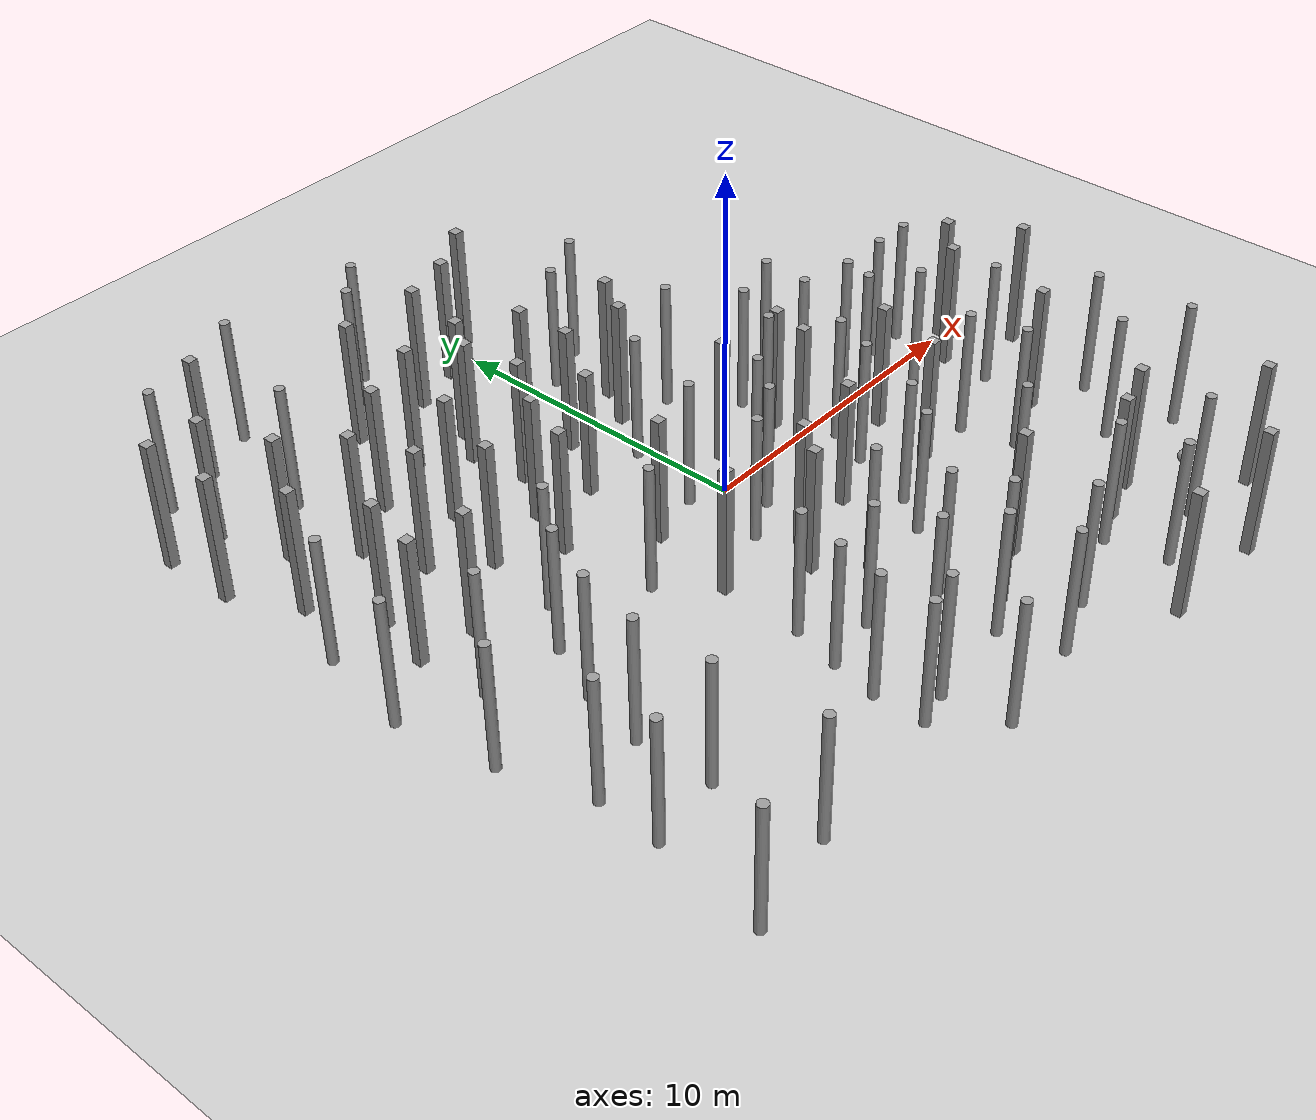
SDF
<sdf version="1.6">
 <world name="default">
  <light name="sun" type="directional">
   <pose>0 0 10 0 -0 0</pose>
   <diffuse>0.8 0.8 0.8 1</diffuse>
   <specular>0.2 0.2 0.2 1</specular>
   <attenuation>
    <range>1000</range>
    <constant>0.9</constant>
    <linear>0.01</linear>
    <quadratic>0.001</quadratic>
   </attenuation>
   <direction>-0.5 0.1 -0.9</direction>
  </light>
  <model name="ground_plane">
   <static>1</static>
   <link name="link">
    <collision name="collision">
     <geometry><plane><normal>0 0 1</normal><size>100 100</size></plane></geometry>
    </collision>
    <visual name="visual">
     <cast_shadows>0</cast_shadows>
     <geometry><plane><normal>0 0 1</normal><size>100 100</size></plane></geometry>
     <material>
      <script><uri>file://media/materials/scripts/gazebo.material</uri><name>Gazebo/Gray</name></script>
     </material>
    </visual>
   </link>
  </model>
  <gravity>0 0 -9.8</gravity>
  <magnetic_field>6e-06 2.3e-05 -4.2e-05</magnetic_field>
  <atmosphere type="adiabatic"/>
  <physics name="default_physics" default="0" type="ode">
   <max_step_size>0.002</max_step_size>
   <real_time_factor>1</real_time_factor>
   <real_time_update_rate>500</real_time_update_rate>
  </physics>
  <scene><ambient>0.4 0.4 0.4 1</ambient><background>0.7 0.7 0.7 1</background><shadows>1</shadows></scene>
  <spherical_coordinates>
   <surface_model>EARTH_WGS84</surface_model>
   <latitude_deg>0</latitude_deg>
   <longitude_deg>0</longitude_deg>
   <elevation>0</elevation>
   <heading_deg>0</heading_deg>
  </spherical_coordinates>
  <model name="unit_sphere">
   <link name="link">
    <inertial>
     <mass>1</mass>
     <inertia><ixx>0.1</ixx><ixy>0</ixy><ixz>0</ixz><iyy>0.1</iyy><iyz>0</iyz><izz>0.1</izz></inertia>
    </inertial>
    <gravity>0</gravity>
    <visual name="visual">
     <geometry><sphere><radius>0.203941</radius></sphere></geometry>
     <material>
      <script><name>Gazebo/Grey</name><uri>file://media/materials/scripts/gazebo.material</uri></script>
      <shader type="pixel"><normal_map>__default__</normal_map></shader>
     </material>
    </visual>
    <collision name="collision">
     <geometry><sphere><radius>0.203941</radius></sphere></geometry>
     <surface>
      <friction>
       <ode><mu>1</mu><mu2>1</mu2><fdir1>0 0 0</fdir1><slip1>0</slip1><slip2>0</slip2></ode>
       <torsional>
        <coefficient>1</coefficient>
        <patch_radius>0</patch_radius>
        <surface_radius>0</surface_radius>
        <use_patch_radius>1</use_patch_radius>
        <ode><slip>0</slip></ode>
       </torsional>
      </friction>
      <bounce><restitution_coefficient>0</restitution_coefficient><threshold>1e+06</threshold></bounce>
      <contact>
       <collide_without_contact>0</collide_without_contact>
       <collide_without_contact_bitmask>1</collide_without_contact_bitmask>
       <collide_bitmask>1</collide_bitmask>
       <ode>
        <soft_cfm>0</soft_cfm>
        <soft_erp>0.2</soft_erp>
        <kp>1e+13</kp>
        <kd>1</kd>
        <max_vel>0.01</max_vel>
        <min_depth>0</min_depth>
       </ode>
       <bullet>
        <split_impulse>1</split_impulse>
        <split_impulse_penetration_threshold>-0.01</split_impulse_penetration_threshold>
        <soft_cfm>0</soft_cfm>
        <soft_erp>0.2</soft_erp>
        <kp>1e+13</kp>
        <kd>1</kd>
       </bullet>
      </contact>
     </surface>
    </collision>
   </link>
   <static>0</static>
   <pose>9.54607 -9.14462 0.203941 0 -0 0</pose>
  </model>
  <audio><device>default</device></audio>
  <model name="unit_box">
   <link name="link">
    <inertial>
     <mass>1000</mass>
     <inertia><ixx>166.667</ixx><ixy>0</ixy><ixz>0</ixz><iyy>166.667</iyy><iyz>0</iyz><izz>166.667</izz></inertia>
    </inertial>
    <visual name="visual">
     <geometry><box><size>0.3 0.3 4</size></box></geometry>
     <material>
      <script><name>Gazebo/Grey</name><uri>file://media/materials/scripts/gazebo.material</uri></script>
      <shader type="vertex"><normal_map>__default__</normal_map></shader>
      <ambient>0.3 0.3 0.3 1</ambient>
      <diffuse>0.7 0.7 0.7 1</diffuse>
      <specular>0.01 0.01 0.01 1</specular>
      <emissive>0 0 0 1</emissive>
     </material>
    </visual>
    <collision name="collision">
     <geometry><box><size>0.3 0.3 4</size></box></geometry>
     <surface>
      <friction>
       <ode><mu>1</mu><mu2>1</mu2><fdir1>0 0 0</fdir1><slip1>0</slip1><slip2>0</slip2></ode>
       <torsional>
        <coefficient>1</coefficient>
        <patch_radius>0</patch_radius>
        <surface_radius>0</surface_radius>
        <use_patch_radius>1</use_patch_radius>
        <ode><slip>0</slip></ode>
       </torsional>
      </friction>
      <bounce><restitution_coefficient>0</restitution_coefficient><threshold>1e+06</threshold></bounce>
      <contact>
       <collide_without_contact>0</collide_without_contact>
       <collide_without_contact_bitmask>1</collide_without_contact_bitmask>
       <collide_bitmask>1</collide_bitmask>
       <ode>
        <soft_cfm>0</soft_cfm>
        <soft_erp>0.2</soft_erp>
        <kp>1e+13</kp>
        <kd>1</kd>
        <max_vel>0.01</max_vel>
        <min_depth>0</min_depth>
       </ode>
       <bullet>
        <split_impulse>1</split_impulse>
        <split_impulse_penetration_threshold>-0.01</split_impulse_penetration_threshold>
        <soft_cfm>0</soft_cfm>
        <soft_erp>0.2</soft_erp>
        <kp>1e+13</kp>
        <kd>1</kd>
       </bullet>
      </contact>
     </surface>
    </collision>
   </link>
   <static>0</static>
   <pose>-1.26732 4.71521 2 1e-05 -1.8e-05 -0.001323</pose>
  </model>
  <model name="unit_box_clone">
   <link name="link">
    <inertial>
     <mass>1000</mass>
     <inertia><ixx>166.667</ixx><ixy>0</ixy><ixz>0</ixz><iyy>166.667</iyy><iyz>0</iyz><izz>166.667</izz></inertia>
    </inertial>
    <visual name="visual">
     <geometry><box><size>0.3 0.3 4</size></box></geometry>
     <material>
      <script><name>Gazebo/Grey</name><uri>file://media/materials/scripts/gazebo.material</uri></script>
      <shader type="vertex"><normal_map>__default__</normal_map></shader>
      <ambient>0.3 0.3 0.3 1</ambient>
      <diffuse>0.7 0.7 0.7 1</diffuse>
      <specular>0.01 0.01 0.01 1</specular>
      <emissive>0 0 0 1</emissive>
     </material>
    </visual>
    <collision name="collision">
     <geometry><box><size>0.3 0.3 4</size></box></geometry>
     <surface>
      <friction>
       <ode><mu>1</mu><mu2>1</mu2><fdir1>0 0 0</fdir1><slip1>0</slip1><slip2>0</slip2></ode>
       <torsional>
        <coefficient>1</coefficient>
        <patch_radius>0</patch_radius>
        <surface_radius>0</surface_radius>
        <use_patch_radius>1</use_patch_radius>
        <ode><slip>0</slip></ode>
       </torsional>
      </friction>
      <bounce><restitution_coefficient>0</restitution_coefficient><threshold>1e+06</threshold></bounce>
      <contact>
       <collide_without_contact>0</collide_without_contact>
       <collide_without_contact_bitmask>1</collide_without_contact_bitmask>
       <collide_bitmask>1</collide_bitmask>
       <ode>
        <soft_cfm>0</soft_cfm>
        <soft_erp>0.2</soft_erp>
        <kp>1e+13</kp>
        <kd>1</kd>
        <max_vel>0.01</max_vel>
        <min_depth>0</min_depth>
       </ode>
       <bullet>
        <split_impulse>1</split_impulse>
        <split_impulse_penetration_threshold>-0.01</split_impulse_penetration_threshold>
        <soft_cfm>0</soft_cfm>
        <soft_erp>0.2</soft_erp>
        <kp>1e+13</kp>
        <kd>1</kd>
       </bullet>
      </contact>
     </surface>
    </collision>
   </link>
   <static>0</static>
   <pose>-2.76544 -0.051248 2 -1e-05 -7e-06 -0.002497</pose>
  </model>
  <model name="unit_box_clone_1">
   <link name="link">
    <inertial>
     <mass>1000</mass>
     <inertia><ixx>166.667</ixx><ixy>0</ixy><ixz>0</ixz><iyy>166.667</iyy><iyz>0</iyz><izz>166.667</izz></inertia>
    </inertial>
    <visual name="visual">
     <geometry><box><size>0.3 0.3 4</size></box></geometry>
     <material>
      <script><name>Gazebo/Grey</name><uri>file://media/materials/scripts/gazebo.material</uri></script>
      <shader type="vertex"><normal_map>__default__</normal_map></shader>
      <ambient>0.3 0.3 0.3 1</ambient>
      <diffuse>0.7 0.7 0.7 1</diffuse>
      <specular>0.01 0.01 0.01 1</specular>
      <emissive>0 0 0 1</emissive>
     </material>
    </visual>
    <collision name="collision">
     <geometry><box><size>0.3 0.3 4</size></box></geometry>
     <surface>
      <friction>
       <ode><mu>1</mu><mu2>1</mu2><fdir1>0 0 0</fdir1><slip1>0</slip1><slip2>0</slip2></ode>
       <torsional>
        <coefficient>1</coefficient>
        <patch_radius>0</patch_radius>
        <surface_radius>0</surface_radius>
        <use_patch_radius>1</use_patch_radius>
        <ode><slip>0</slip></ode>
       </torsional>
      </friction>
      <bounce><restitution_coefficient>0</restitution_coefficient><threshold>1e+06</threshold></bounce>
      <contact>
       <collide_without_contact>0</collide_without_contact>
       <collide_without_contact_bitmask>1</collide_without_contact_bitmask>
       <collide_bitmask>1</collide_bitmask>
       <ode>
        <soft_cfm>0</soft_cfm>
        <soft_erp>0.2</soft_erp>
        <kp>1e+13</kp>
        <kd>1</kd>
        <max_vel>0.01</max_vel>
        <min_depth>0</min_depth>
       </ode>
       <bullet>
        <split_impulse>1</split_impulse>
        <split_impulse_penetration_threshold>-0.01</split_impulse_penetration_threshold>
        <soft_cfm>0</soft_cfm>
        <soft_erp>0.2</soft_erp>
        <kp>1e+13</kp>
        <kd>1</kd>
       </bullet>
      </contact>
     </surface>
    </collision>
   </link>
   <static>0</static>
   <pose>-2.89919 7.41396 2 5e-06 1.3e-05 0.00093</pose>
  </model>
  <model name="unit_box_clone_2">
   <link name="link">
    <inertial>
     <mass>1000</mass>
     <inertia><ixx>166.667</ixx><ixy>0</ixy><ixz>0</ixz><iyy>166.667</iyy><iyz>0</iyz><izz>166.667</izz></inertia>
    </inertial>
    <visual name="visual">
     <geometry><box><size>0.3 0.3 4</size></box></geometry>
     <material>
      <script><name>Gazebo/Grey</name><uri>file://media/materials/scripts/gazebo.material</uri></script>
      <shader type="vertex"><normal_map>__default__</normal_map></shader>
      <ambient>0.3 0.3 0.3 1</ambient>
      <diffuse>0.7 0.7 0.7 1</diffuse>
      <specular>0.01 0.01 0.01 1</specular>
      <emissive>0 0 0 1</emissive>
     </material>
    </visual>
    <collision name="collision">
     <geometry><box><size>0.3 0.3 4</size></box></geometry>
     <surface>
      <friction>
       <ode><mu>1</mu><mu2>1</mu2><fdir1>0 0 0</fdir1><slip1>0</slip1><slip2>0</slip2></ode>
       <torsional>
        <coefficient>1</coefficient>
        <patch_radius>0</patch_radius>
        <surface_radius>0</surface_radius>
        <use_patch_radius>1</use_patch_radius>
        <ode><slip>0</slip></ode>
       </torsional>
      </friction>
      <bounce><restitution_coefficient>0</restitution_coefficient><threshold>1e+06</threshold></bounce>
      <contact>
       <collide_without_contact>0</collide_without_contact>
       <collide_without_contact_bitmask>1</collide_without_contact_bitmask>
       <collide_bitmask>1</collide_bitmask>
       <ode>
        <soft_cfm>0</soft_cfm>
        <soft_erp>0.2</soft_erp>
        <kp>1e+13</kp>
        <kd>1</kd>
        <max_vel>0.01</max_vel>
        <min_depth>0</min_depth>
       </ode>
       <bullet>
        <split_impulse>1</split_impulse>
        <split_impulse_penetration_threshold>-0.01</split_impulse_penetration_threshold>
        <soft_cfm>0</soft_cfm>
        <soft_erp>0.2</soft_erp>
        <kp>1e+13</kp>
        <kd>1</kd>
       </bullet>
      </contact>
     </surface>
    </collision>
   </link>
   <static>0</static>
   <pose>4.92527 -3.34792 2 1e-06 2e-06 1.2e-05</pose>
  </model>
  <model name="unit_box_clone_3">
   <link name="link">
    <inertial>
     <mass>1000</mass>
     <inertia><ixx>166.667</ixx><ixy>0</ixy><ixz>0</ixz><iyy>166.667</iyy><iyz>0</iyz><izz>166.667</izz></inertia>
    </inertial>
    <visual name="visual">
     <geometry><box><size>0.3 0.3 4</size></box></geometry>
     <material>
      <script><name>Gazebo/Grey</name><uri>file://media/materials/scripts/gazebo.material</uri></script>
      <shader type="vertex"><normal_map>__default__</normal_map></shader>
      <ambient>0.3 0.3 0.3 1</ambient>
      <diffuse>0.7 0.7 0.7 1</diffuse>
      <specular>0.01 0.01 0.01 1</specular>
      <emissive>0 0 0 1</emissive>
     </material>
    </visual>
    <collision name="collision">
     <geometry><box><size>0.3 0.3 4</size></box></geometry>
     <surface>
      <friction>
       <ode><mu>1</mu><mu2>1</mu2><fdir1>0 0 0</fdir1><slip1>0</slip1><slip2>0</slip2></ode>
       <torsional>
        <coefficient>1</coefficient>
        <patch_radius>0</patch_radius>
        <surface_radius>0</surface_radius>
        <use_patch_radius>1</use_patch_radius>
        <ode><slip>0</slip></ode>
       </torsional>
      </friction>
      <bounce><restitution_coefficient>0</restitution_coefficient><threshold>1e+06</threshold></bounce>
      <contact>
       <collide_without_contact>0</collide_without_contact>
       <collide_without_contact_bitmask>1</collide_without_contact_bitmask>
       <collide_bitmask>1</collide_bitmask>
       <ode>
        <soft_cfm>0</soft_cfm>
        <soft_erp>0.2</soft_erp>
        <kp>1e+13</kp>
        <kd>1</kd>
        <max_vel>0.01</max_vel>
        <min_depth>0</min_depth>
       </ode>
       <bullet>
        <split_impulse>1</split_impulse>
        <split_impulse_penetration_threshold>-0.01</split_impulse_penetration_threshold>
        <soft_cfm>0</soft_cfm>
        <soft_erp>0.2</soft_erp>
        <kp>1e+13</kp>
        <kd>1</kd>
       </bullet>
      </contact>
     </surface>
    </collision>
   </link>
   <static>0</static>
   <pose>-9.81583 6.97363 2 -1.8e-05 -9e-06 -0.002993</pose>
  </model>
  <model name="unit_box_clone_4">
   <link name="link">
    <inertial>
     <mass>1000</mass>
     <inertia><ixx>166.667</ixx><ixy>0</ixy><ixz>0</ixz><iyy>166.667</iyy><iyz>0</iyz><izz>166.667</izz></inertia>
    </inertial>
    <visual name="visual">
     <geometry><box><size>0.3 0.3 4</size></box></geometry>
     <material>
      <script><name>Gazebo/Grey</name><uri>file://media/materials/scripts/gazebo.material</uri></script>
      <shader type="vertex"><normal_map>__default__</normal_map></shader>
      <ambient>0.3 0.3 0.3 1</ambient>
      <diffuse>0.7 0.7 0.7 1</diffuse>
      <specular>0.01 0.01 0.01 1</specular>
      <emissive>0 0 0 1</emissive>
     </material>
    </visual>
    <collision name="collision">
     <geometry><box><size>0.3 0.3 4</size></box></geometry>
     <surface>
      <friction>
       <ode><mu>1</mu><mu2>1</mu2><fdir1>0 0 0</fdir1><slip1>0</slip1><slip2>0</slip2></ode>
       <torsional>
        <coefficient>1</coefficient>
        <patch_radius>0</patch_radius>
        <surface_radius>0</surface_radius>
        <use_patch_radius>1</use_patch_radius>
        <ode><slip>0</slip></ode>
       </torsional>
      </friction>
      <bounce><restitution_coefficient>0</restitution_coefficient><threshold>1e+06</threshold></bounce>
      <contact>
       <collide_without_contact>0</collide_without_contact>
       <collide_without_contact_bitmask>1</collide_without_contact_bitmask>
       <collide_bitmask>1</collide_bitmask>
       <ode>
        <soft_cfm>0</soft_cfm>
        <soft_erp>0.2</soft_erp>
        <kp>1e+13</kp>
        <kd>1</kd>
        <max_vel>0.01</max_vel>
        <min_depth>0</min_depth>
       </ode>
       <bullet>
        <split_impulse>1</split_impulse>
        <split_impulse_penetration_threshold>-0.01</split_impulse_penetration_threshold>
        <soft_cfm>0</soft_cfm>
        <soft_erp>0.2</soft_erp>
        <kp>1e+13</kp>
        <kd>1</kd>
       </bullet>
      </contact>
     </surface>
    </collision>
   </link>
   <static>0</static>
   <pose>-12.064 9.20916 2 -2e-06 4e-06 -0.003091</pose>
  </model>
  <model name="unit_box_clone_5">
   <link name="link">
    <inertial>
     <mass>1000</mass>
     <inertia><ixx>166.667</ixx><ixy>0</ixy><ixz>0</ixz><iyy>166.667</iyy><iyz>0</iyz><izz>166.667</izz></inertia>
    </inertial>
    <visual name="visual">
     <geometry><box><size>0.3 0.3 4</size></box></geometry>
     <material>
      <script><name>Gazebo/Grey</name><uri>file://media/materials/scripts/gazebo.material</uri></script>
      <shader type="vertex"><normal_map>__default__</normal_map></shader>
      <ambient>0.3 0.3 0.3 1</ambient>
      <diffuse>0.7 0.7 0.7 1</diffuse>
      <specular>0.01 0.01 0.01 1</specular>
      <emissive>0 0 0 1</emissive>
     </material>
    </visual>
    <collision name="collision">
     <geometry><box><size>0.3 0.3 4</size></box></geometry>
     <surface>
      <friction>
       <ode><mu>1</mu><mu2>1</mu2><fdir1>0 0 0</fdir1><slip1>0</slip1><slip2>0</slip2></ode>
       <torsional>
        <coefficient>1</coefficient>
        <patch_radius>0</patch_radius>
        <surface_radius>0</surface_radius>
        <use_patch_radius>1</use_patch_radius>
        <ode><slip>0</slip></ode>
       </torsional>
      </friction>
      <bounce><restitution_coefficient>0</restitution_coefficient><threshold>1e+06</threshold></bounce>
      <contact>
       <collide_without_contact>0</collide_without_contact>
       <collide_without_contact_bitmask>1</collide_without_contact_bitmask>
       <collide_bitmask>1</collide_bitmask>
       <ode>
        <soft_cfm>0</soft_cfm>
        <soft_erp>0.2</soft_erp>
        <kp>1e+13</kp>
        <kd>1</kd>
        <max_vel>0.01</max_vel>
        <min_depth>0</min_depth>
       </ode>
       <bullet>
        <split_impulse>1</split_impulse>
        <split_impulse_penetration_threshold>-0.01</split_impulse_penetration_threshold>
        <soft_cfm>0</soft_cfm>
        <soft_erp>0.2</soft_erp>
        <kp>1e+13</kp>
        <kd>1</kd>
       </bullet>
      </contact>
     </surface>
    </collision>
   </link>
   <static>0</static>
   <pose>3.35408 0.911814 2 1e-06 5e-06 -0.010194</pose>
  </model>
  <model name="unit_box_clone_6">
   <link name="link">
    <inertial>
     <mass>1000</mass>
     <inertia><ixx>166.667</ixx><ixy>0</ixy><ixz>0</ixz><iyy>166.667</iyy><iyz>0</iyz><izz>166.667</izz></inertia>
    </inertial>
    <visual name="visual">
     <geometry><box><size>0.3 0.3 4</size></box></geometry>
     <material>
      <script><name>Gazebo/Grey</name><uri>file://media/materials/scripts/gazebo.material</uri></script>
      <shader type="vertex"><normal_map>__default__</normal_map></shader>
      <ambient>0.3 0.3 0.3 1</ambient>
      <diffuse>0.7 0.7 0.7 1</diffuse>
      <specular>0.01 0.01 0.01 1</specular>
      <emissive>0 0 0 1</emissive>
     </material>
    </visual>
    <collision name="collision">
     <geometry><box><size>0.3 0.3 4</size></box></geometry>
     <surface>
      <friction>
       <ode><mu>1</mu><mu2>1</mu2><fdir1>0 0 0</fdir1><slip1>0</slip1><slip2>0</slip2></ode>
       <torsional>
        <coefficient>1</coefficient>
        <patch_radius>0</patch_radius>
        <surface_radius>0</surface_radius>
        <use_patch_radius>1</use_patch_radius>
        <ode><slip>0</slip></ode>
       </torsional>
      </friction>
      <bounce><restitution_coefficient>0</restitution_coefficient><threshold>1e+06</threshold></bounce>
      <contact>
       <collide_without_contact>0</collide_without_contact>
       <collide_without_contact_bitmask>1</collide_without_contact_bitmask>
       <collide_bitmask>1</collide_bitmask>
       <ode>
        <soft_cfm>0</soft_cfm>
        <soft_erp>0.2</soft_erp>
        <kp>1e+13</kp>
        <kd>1</kd>
        <max_vel>0.01</max_vel>
        <min_depth>0</min_depth>
       </ode>
       <bullet>
        <split_impulse>1</split_impulse>
        <split_impulse_penetration_threshold>-0.01</split_impulse_penetration_threshold>
        <soft_cfm>0</soft_cfm>
        <soft_erp>0.2</soft_erp>
        <kp>1e+13</kp>
        <kd>1</kd>
       </bullet>
      </contact>
     </surface>
    </collision>
   </link>
   <static>0</static>
   <pose>10.5124 0.091577 2 1.3e-05 -1e-06 -0.012364</pose>
  </model>
  <model name="unit_box_clone_7">
   <link name="link">
    <inertial>
     <mass>1000</mass>
     <inertia><ixx>166.667</ixx><ixy>0</ixy><ixz>0</ixz><iyy>166.667</iyy><iyz>0</iyz><izz>166.667</izz></inertia>
    </inertial>
    <visual name="visual">
     <geometry><box><size>0.3 0.3 4</size></box></geometry>
     <material>
      <script><name>Gazebo/Grey</name><uri>file://media/materials/scripts/gazebo.material</uri></script>
      <shader type="vertex"><normal_map>__default__</normal_map></shader>
      <ambient>0.3 0.3 0.3 1</ambient>
      <diffuse>0.7 0.7 0.7 1</diffuse>
      <specular>0.01 0.01 0.01 1</specular>
      <emissive>0 0 0 1</emissive>
     </material>
    </visual>
    <collision name="collision">
     <geometry><box><size>0.3 0.3 4</size></box></geometry>
     <surface>
      <friction>
       <ode><mu>1</mu><mu2>1</mu2><fdir1>0 0 0</fdir1><slip1>0</slip1><slip2>0</slip2></ode>
       <torsional>
        <coefficient>1</coefficient>
        <patch_radius>0</patch_radius>
        <surface_radius>0</surface_radius>
        <use_patch_radius>1</use_patch_radius>
        <ode><slip>0</slip></ode>
       </torsional>
      </friction>
      <bounce><restitution_coefficient>0</restitution_coefficient><threshold>1e+06</threshold></bounce>
      <contact>
       <collide_without_contact>0</collide_without_contact>
       <collide_without_contact_bitmask>1</collide_without_contact_bitmask>
       <collide_bitmask>1</collide_bitmask>
       <ode>
        <soft_cfm>0</soft_cfm>
        <soft_erp>0.2</soft_erp>
        <kp>1e+13</kp>
        <kd>1</kd>
        <max_vel>0.01</max_vel>
        <min_depth>0</min_depth>
       </ode>
       <bullet>
        <split_impulse>1</split_impulse>
        <split_impulse_penetration_threshold>-0.01</split_impulse_penetration_threshold>
        <soft_cfm>0</soft_cfm>
        <soft_erp>0.2</soft_erp>
        <kp>1e+13</kp>
        <kd>1</kd>
       </bullet>
      </contact>
     </surface>
    </collision>
   </link>
   <static>0</static>
   <pose>9.86052 -10.963 2 -1.2e-05 -4e-06 -0.004853</pose>
  </model>
  <model name="unit_box_clone_8">
   <link name="link">
    <inertial>
     <mass>1000</mass>
     <inertia><ixx>166.667</ixx><ixy>0</ixy><ixz>0</ixz><iyy>166.667</iyy><iyz>0</iyz><izz>166.667</izz></inertia>
    </inertial>
    <visual name="visual">
     <geometry><box><size>0.3 0.3 4</size></box></geometry>
     <material>
      <script><name>Gazebo/Grey</name><uri>file://media/materials/scripts/gazebo.material</uri></script>
      <shader type="vertex"><normal_map>__default__</normal_map></shader>
      <ambient>0.3 0.3 0.3 1</ambient>
      <diffuse>0.7 0.7 0.7 1</diffuse>
      <specular>0.01 0.01 0.01 1</specular>
      <emissive>0 0 0 1</emissive>
     </material>
    </visual>
    <collision name="collision">
     <geometry><box><size>0.3 0.3 4</size></box></geometry>
     <surface>
      <friction>
       <ode><mu>1</mu><mu2>1</mu2><fdir1>0 0 0</fdir1><slip1>0</slip1><slip2>0</slip2></ode>
       <torsional>
        <coefficient>1</coefficient>
        <patch_radius>0</patch_radius>
        <surface_radius>0</surface_radius>
        <use_patch_radius>1</use_patch_radius>
        <ode><slip>0</slip></ode>
       </torsional>
      </friction>
      <bounce><restitution_coefficient>0</restitution_coefficient><threshold>1e+06</threshold></bounce>
      <contact>
       <collide_without_contact>0</collide_without_contact>
       <collide_without_contact_bitmask>1</collide_without_contact_bitmask>
       <collide_bitmask>1</collide_bitmask>
       <ode>
        <soft_cfm>0</soft_cfm>
        <soft_erp>0.2</soft_erp>
        <kp>1e+13</kp>
        <kd>1</kd>
        <max_vel>0.01</max_vel>
        <min_depth>0</min_depth>
       </ode>
       <bullet>
        <split_impulse>1</split_impulse>
        <split_impulse_penetration_threshold>-0.01</split_impulse_penetration_threshold>
        <soft_cfm>0</soft_cfm>
        <soft_erp>0.2</soft_erp>
        <kp>1e+13</kp>
        <kd>1</kd>
       </bullet>
      </contact>
     </surface>
    </collision>
   </link>
   <static>0</static>
   <pose>-6.68888 6.67579 2 -5e-06 -0 -0.003022</pose>
  </model>
  <model name="unit_box_clone_9">
   <link name="link">
    <inertial>
     <mass>1000</mass>
     <inertia><ixx>166.667</ixx><ixy>0</ixy><ixz>0</ixz><iyy>166.667</iyy><iyz>0</iyz><izz>166.667</izz></inertia>
    </inertial>
    <visual name="visual">
     <geometry><box><size>0.3 0.3 4</size></box></geometry>
     <material>
      <script><name>Gazebo/Grey</name><uri>file://media/materials/scripts/gazebo.material</uri></script>
      <shader type="vertex"><normal_map>__default__</normal_map></shader>
      <ambient>0.3 0.3 0.3 1</ambient>
      <diffuse>0.7 0.7 0.7 1</diffuse>
      <specular>0.01 0.01 0.01 1</specular>
      <emissive>0 0 0 1</emissive>
     </material>
    </visual>
    <collision name="collision">
     <geometry><box><size>0.3 0.3 4</size></box></geometry>
     <surface>
      <friction>
       <ode><mu>1</mu><mu2>1</mu2><fdir1>0 0 0</fdir1><slip1>0</slip1><slip2>0</slip2></ode>
       <torsional>
        <coefficient>1</coefficient>
        <patch_radius>0</patch_radius>
        <surface_radius>0</surface_radius>
        <use_patch_radius>1</use_patch_radius>
        <ode><slip>0</slip></ode>
       </torsional>
      </friction>
      <bounce><restitution_coefficient>0</restitution_coefficient><threshold>1e+06</threshold></bounce>
      <contact>
       <collide_without_contact>0</collide_without_contact>
       <collide_without_contact_bitmask>1</collide_without_contact_bitmask>
       <collide_bitmask>1</collide_bitmask>
       <ode>
        <soft_cfm>0</soft_cfm>
        <soft_erp>0.2</soft_erp>
        <kp>1e+13</kp>
        <kd>1</kd>
        <max_vel>0.01</max_vel>
        <min_depth>0</min_depth>
       </ode>
       <bullet>
        <split_impulse>1</split_impulse>
        <split_impulse_penetration_threshold>-0.01</split_impulse_penetration_threshold>
        <soft_cfm>0</soft_cfm>
        <soft_erp>0.2</soft_erp>
        <kp>1e+13</kp>
        <kd>1</kd>
       </bullet>
      </contact>
     </surface>
    </collision>
   </link>
   <static>0</static>
   <pose>-8.44972 5.60761 2 1.2e-05 2e-06 -0.001522</pose>
  </model>
  <model name="unit_box_clone_10">
   <link name="link">
    <inertial>
     <mass>1000</mass>
     <inertia><ixx>166.667</ixx><ixy>0</ixy><ixz>0</ixz><iyy>166.667</iyy><iyz>0</iyz><izz>166.667</izz></inertia>
    </inertial>
    <visual name="visual">
     <geometry><box><size>0.3 0.3 4</size></box></geometry>
     <material>
      <script><name>Gazebo/Grey</name><uri>file://media/materials/scripts/gazebo.material</uri></script>
      <shader type="vertex"><normal_map>__default__</normal_map></shader>
      <ambient>0.3 0.3 0.3 1</ambient>
      <diffuse>0.7 0.7 0.7 1</diffuse>
      <specular>0.01 0.01 0.01 1</specular>
      <emissive>0 0 0 1</emissive>
     </material>
    </visual>
    <collision name="collision">
     <geometry><box><size>0.3 0.3 4</size></box></geometry>
     <surface>
      <friction>
       <ode><mu>1</mu><mu2>1</mu2><fdir1>0 0 0</fdir1><slip1>0</slip1><slip2>0</slip2></ode>
       <torsional>
        <coefficient>1</coefficient>
        <patch_radius>0</patch_radius>
        <surface_radius>0</surface_radius>
        <use_patch_radius>1</use_patch_radius>
        <ode><slip>0</slip></ode>
       </torsional>
      </friction>
      <bounce><restitution_coefficient>0</restitution_coefficient><threshold>1e+06</threshold></bounce>
      <contact>
       <collide_without_contact>0</collide_without_contact>
       <collide_without_contact_bitmask>1</collide_without_contact_bitmask>
       <collide_bitmask>1</collide_bitmask>
       <ode>
        <soft_cfm>0</soft_cfm>
        <soft_erp>0.2</soft_erp>
        <kp>1e+13</kp>
        <kd>1</kd>
        <max_vel>0.01</max_vel>
        <min_depth>0</min_depth>
       </ode>
       <bullet>
        <split_impulse>1</split_impulse>
        <split_impulse_penetration_threshold>-0.01</split_impulse_penetration_threshold>
        <soft_cfm>0</soft_cfm>
        <soft_erp>0.2</soft_erp>
        <kp>1e+13</kp>
        <kd>1</kd>
       </bullet>
      </contact>
     </surface>
    </collision>
   </link>
   <static>0</static>
   <pose>-8.91738 11.4995 2 4e-06 -0 -0.003322</pose>
  </model>
  <model name="unit_box_clone_11">
   <link name="link">
    <inertial>
     <mass>1000</mass>
     <inertia><ixx>166.667</ixx><ixy>0</ixy><ixz>0</ixz><iyy>166.667</iyy><iyz>0</iyz><izz>166.667</izz></inertia>
    </inertial>
    <visual name="visual">
     <geometry><box><size>0.3 0.3 4</size></box></geometry>
     <material>
      <script><name>Gazebo/Grey</name><uri>file://media/materials/scripts/gazebo.material</uri></script>
      <shader type="vertex"><normal_map>__default__</normal_map></shader>
      <ambient>0.3 0.3 0.3 1</ambient>
      <diffuse>0.7 0.7 0.7 1</diffuse>
      <specular>0.01 0.01 0.01 1</specular>
      <emissive>0 0 0 1</emissive>
     </material>
    </visual>
    <collision name="collision">
     <geometry><box><size>0.3 0.3 4</size></box></geometry>
     <surface>
      <friction>
       <ode><mu>1</mu><mu2>1</mu2><fdir1>0 0 0</fdir1><slip1>0</slip1><slip2>0</slip2></ode>
       <torsional>
        <coefficient>1</coefficient>
        <patch_radius>0</patch_radius>
        <surface_radius>0</surface_radius>
        <use_patch_radius>1</use_patch_radius>
        <ode><slip>0</slip></ode>
       </torsional>
      </friction>
      <bounce><restitution_coefficient>0</restitution_coefficient><threshold>1e+06</threshold></bounce>
      <contact>
       <collide_without_contact>0</collide_without_contact>
       <collide_without_contact_bitmask>1</collide_without_contact_bitmask>
       <collide_bitmask>1</collide_bitmask>
       <ode>
        <soft_cfm>0</soft_cfm>
        <soft_erp>0.2</soft_erp>
        <kp>1e+13</kp>
        <kd>1</kd>
        <max_vel>0.01</max_vel>
        <min_depth>0</min_depth>
       </ode>
       <bullet>
        <split_impulse>1</split_impulse>
        <split_impulse_penetration_threshold>-0.01</split_impulse_penetration_threshold>
        <soft_cfm>0</soft_cfm>
        <soft_erp>0.2</soft_erp>
        <kp>1e+13</kp>
        <kd>1</kd>
       </bullet>
      </contact>
     </surface>
    </collision>
   </link>
   <static>0</static>
   <pose>-10.559 9.10964 2 -2e-06 6e-06 0.004379</pose>
  </model>
  <model name="unit_box_clone_12">
   <link name="link">
    <inertial>
     <mass>1000</mass>
     <inertia><ixx>166.667</ixx><ixy>0</ixy><ixz>0</ixz><iyy>166.667</iyy><iyz>0</iyz><izz>166.667</izz></inertia>
    </inertial>
    <visual name="visual">
     <geometry><box><size>0.3 0.3 4</size></box></geometry>
     <material>
      <script><name>Gazebo/Grey</name><uri>file://media/materials/scripts/gazebo.material</uri></script>
      <shader type="vertex"><normal_map>__default__</normal_map></shader>
      <ambient>0.3 0.3 0.3 1</ambient>
      <diffuse>0.7 0.7 0.7 1</diffuse>
      <specular>0.01 0.01 0.01 1</specular>
      <emissive>0 0 0 1</emissive>
     </material>
    </visual>
    <collision name="collision">
     <geometry><box><size>0.3 0.3 4</size></box></geometry>
     <surface>
      <friction>
       <ode><mu>1</mu><mu2>1</mu2><fdir1>0 0 0</fdir1><slip1>0</slip1><slip2>0</slip2></ode>
       <torsional>
        <coefficient>1</coefficient>
        <patch_radius>0</patch_radius>
        <surface_radius>0</surface_radius>
        <use_patch_radius>1</use_patch_radius>
        <ode><slip>0</slip></ode>
       </torsional>
      </friction>
      <bounce><restitution_coefficient>0</restitution_coefficient><threshold>1e+06</threshold></bounce>
      <contact>
       <collide_without_contact>0</collide_without_contact>
       <collide_without_contact_bitmask>1</collide_without_contact_bitmask>
       <collide_bitmask>1</collide_bitmask>
       <ode>
        <soft_cfm>0</soft_cfm>
        <soft_erp>0.2</soft_erp>
        <kp>1e+13</kp>
        <kd>1</kd>
        <max_vel>0.01</max_vel>
        <min_depth>0</min_depth>
       </ode>
       <bullet>
        <split_impulse>1</split_impulse>
        <split_impulse_penetration_threshold>-0.01</split_impulse_penetration_threshold>
        <soft_cfm>0</soft_cfm>
        <soft_erp>0.2</soft_erp>
        <kp>1e+13</kp>
        <kd>1</kd>
       </bullet>
      </contact>
     </surface>
    </collision>
   </link>
   <static>0</static>
   <pose>-6.46638 2.58977 2 6e-06 -1.6e-05 -0.001869</pose>
  </model>
  <model name="unit_box_clone_13">
   <link name="link">
    <inertial>
     <mass>1000</mass>
     <inertia><ixx>166.667</ixx><ixy>0</ixy><ixz>0</ixz><iyy>166.667</iyy><iyz>0</iyz><izz>166.667</izz></inertia>
    </inertial>
    <visual name="visual">
     <geometry><box><size>0.3 0.3 4</size></box></geometry>
     <material>
      <script><name>Gazebo/Grey</name><uri>file://media/materials/scripts/gazebo.material</uri></script>
      <shader type="vertex"><normal_map>__default__</normal_map></shader>
      <ambient>0.3 0.3 0.3 1</ambient>
      <diffuse>0.7 0.7 0.7 1</diffuse>
      <specular>0.01 0.01 0.01 1</specular>
      <emissive>0 0 0 1</emissive>
     </material>
    </visual>
    <collision name="collision">
     <geometry><box><size>0.3 0.3 4</size></box></geometry>
     <surface>
      <friction>
       <ode><mu>1</mu><mu2>1</mu2><fdir1>0 0 0</fdir1><slip1>0</slip1><slip2>0</slip2></ode>
       <torsional>
        <coefficient>1</coefficient>
        <patch_radius>0</patch_radius>
        <surface_radius>0</surface_radius>
        <use_patch_radius>1</use_patch_radius>
        <ode><slip>0</slip></ode>
       </torsional>
      </friction>
      <bounce><restitution_coefficient>0</restitution_coefficient><threshold>1e+06</threshold></bounce>
      <contact>
       <collide_without_contact>0</collide_without_contact>
       <collide_without_contact_bitmask>1</collide_without_contact_bitmask>
       <collide_bitmask>1</collide_bitmask>
       <ode>
        <soft_cfm>0</soft_cfm>
        <soft_erp>0.2</soft_erp>
        <kp>1e+13</kp>
        <kd>1</kd>
        <max_vel>0.01</max_vel>
        <min_depth>0</min_depth>
       </ode>
       <bullet>
        <split_impulse>1</split_impulse>
        <split_impulse_penetration_threshold>-0.01</split_impulse_penetration_threshold>
        <soft_cfm>0</soft_cfm>
        <soft_erp>0.2</soft_erp>
        <kp>1e+13</kp>
        <kd>1</kd>
       </bullet>
      </contact>
     </surface>
    </collision>
   </link>
   <static>0</static>
   <pose>-10.0001 3.0001 2 -1e-06 -7e-06 -0.003577</pose>
  </model>
  <model name="unit_box_clone_14">
   <link name="link">
    <inertial>
     <mass>1000</mass>
     <inertia><ixx>166.667</ixx><ixy>0</ixy><ixz>0</ixz><iyy>166.667</iyy><iyz>0</iyz><izz>166.667</izz></inertia>
    </inertial>
    <visual name="visual">
     <geometry><box><size>0.3 0.3 4</size></box></geometry>
     <material>
      <script><name>Gazebo/Grey</name><uri>file://media/materials/scripts/gazebo.material</uri></script>
      <shader type="vertex"><normal_map>__default__</normal_map></shader>
      <ambient>0.3 0.3 0.3 1</ambient>
      <diffuse>0.7 0.7 0.7 1</diffuse>
      <specular>0.01 0.01 0.01 1</specular>
      <emissive>0 0 0 1</emissive>
     </material>
    </visual>
    <collision name="collision">
     <geometry><box><size>0.3 0.3 4</size></box></geometry>
     <surface>
      <friction>
       <ode><mu>1</mu><mu2>1</mu2><fdir1>0 0 0</fdir1><slip1>0</slip1><slip2>0</slip2></ode>
       <torsional>
        <coefficient>1</coefficient>
        <patch_radius>0</patch_radius>
        <surface_radius>0</surface_radius>
        <use_patch_radius>1</use_patch_radius>
        <ode><slip>0</slip></ode>
       </torsional>
      </friction>
      <bounce><restitution_coefficient>0</restitution_coefficient><threshold>1e+06</threshold></bounce>
      <contact>
       <collide_without_contact>0</collide_without_contact>
       <collide_without_contact_bitmask>1</collide_without_contact_bitmask>
       <collide_bitmask>1</collide_bitmask>
       <ode>
        <soft_cfm>0</soft_cfm>
        <soft_erp>0.2</soft_erp>
        <kp>1e+13</kp>
        <kd>1</kd>
        <max_vel>0.01</max_vel>
        <min_depth>0</min_depth>
       </ode>
       <bullet>
        <split_impulse>1</split_impulse>
        <split_impulse_penetration_threshold>-0.01</split_impulse_penetration_threshold>
        <soft_cfm>0</soft_cfm>
        <soft_erp>0.2</soft_erp>
        <kp>1e+13</kp>
        <kd>1</kd>
       </bullet>
      </contact>
     </surface>
    </collision>
   </link>
   <static>0</static>
   <pose>-11.9999 7.00014 2 -9e-06 -2e-06 -0.001109</pose>
  </model>
  <model name="unit_box_clone_15">
   <link name="link">
    <inertial>
     <mass>1000</mass>
     <inertia><ixx>166.667</ixx><ixy>0</ixy><ixz>0</ixz><iyy>166.667</iyy><iyz>0</iyz><izz>166.667</izz></inertia>
    </inertial>
    <visual name="visual">
     <geometry><box><size>0.3 0.3 4</size></box></geometry>
     <material>
      <script><name>Gazebo/Grey</name><uri>file://media/materials/scripts/gazebo.material</uri></script>
      <shader type="vertex"><normal_map>__default__</normal_map></shader>
      <ambient>0.3 0.3 0.3 1</ambient>
      <diffuse>0.7 0.7 0.7 1</diffuse>
      <specular>0.01 0.01 0.01 1</specular>
      <emissive>0 0 0 1</emissive>
     </material>
    </visual>
    <collision name="collision">
     <geometry><box><size>0.3 0.3 4</size></box></geometry>
     <surface>
      <friction>
       <ode><mu>1</mu><mu2>1</mu2><fdir1>0 0 0</fdir1><slip1>0</slip1><slip2>0</slip2></ode>
       <torsional>
        <coefficient>1</coefficient>
        <patch_radius>0</patch_radius>
        <surface_radius>0</surface_radius>
        <use_patch_radius>1</use_patch_radius>
        <ode><slip>0</slip></ode>
       </torsional>
      </friction>
      <bounce><restitution_coefficient>0</restitution_coefficient><threshold>1e+06</threshold></bounce>
      <contact>
       <collide_without_contact>0</collide_without_contact>
       <collide_without_contact_bitmask>1</collide_without_contact_bitmask>
       <collide_bitmask>1</collide_bitmask>
       <ode>
        <soft_cfm>0</soft_cfm>
        <soft_erp>0.2</soft_erp>
        <kp>1e+13</kp>
        <kd>1</kd>
        <max_vel>0.01</max_vel>
        <min_depth>0</min_depth>
       </ode>
       <bullet>
        <split_impulse>1</split_impulse>
        <split_impulse_penetration_threshold>-0.01</split_impulse_penetration_threshold>
        <soft_cfm>0</soft_cfm>
        <soft_erp>0.2</soft_erp>
        <kp>1e+13</kp>
        <kd>1</kd>
       </bullet>
      </contact>
     </surface>
    </collision>
   </link>
   <static>0</static>
   <pose>-8.74152 1.0488 2 -2e-06 0 0.000224</pose>
  </model>
  <model name="unit_box_clone_16">
   <link name="link">
    <inertial>
     <mass>1000</mass>
     <inertia><ixx>166.667</ixx><ixy>0</ixy><ixz>0</ixz><iyy>166.667</iyy><iyz>0</iyz><izz>166.667</izz></inertia>
    </inertial>
    <visual name="visual">
     <geometry><box><size>0.3 0.3 4</size></box></geometry>
     <material>
      <script><name>Gazebo/Grey</name><uri>file://media/materials/scripts/gazebo.material</uri></script>
      <shader type="vertex"><normal_map>__default__</normal_map></shader>
      <ambient>0.3 0.3 0.3 1</ambient>
      <diffuse>0.7 0.7 0.7 1</diffuse>
      <specular>0.01 0.01 0.01 1</specular>
      <emissive>0 0 0 1</emissive>
     </material>
    </visual>
    <collision name="collision">
     <geometry><box><size>0.3 0.3 4</size></box></geometry>
     <surface>
      <friction>
       <ode><mu>1</mu><mu2>1</mu2><fdir1>0 0 0</fdir1><slip1>0</slip1><slip2>0</slip2></ode>
       <torsional>
        <coefficient>1</coefficient>
        <patch_radius>0</patch_radius>
        <surface_radius>0</surface_radius>
        <use_patch_radius>1</use_patch_radius>
        <ode><slip>0</slip></ode>
       </torsional>
      </friction>
      <bounce><restitution_coefficient>0</restitution_coefficient><threshold>1e+06</threshold></bounce>
      <contact>
       <collide_without_contact>0</collide_without_contact>
       <collide_without_contact_bitmask>1</collide_without_contact_bitmask>
       <collide_bitmask>1</collide_bitmask>
       <ode>
        <soft_cfm>0</soft_cfm>
        <soft_erp>0.2</soft_erp>
        <kp>1e+13</kp>
        <kd>1</kd>
        <max_vel>0.01</max_vel>
        <min_depth>0</min_depth>
       </ode>
       <bullet>
        <split_impulse>1</split_impulse>
        <split_impulse_penetration_threshold>-0.01</split_impulse_penetration_threshold>
        <soft_cfm>0</soft_cfm>
        <soft_erp>0.2</soft_erp>
        <kp>1e+13</kp>
        <kd>1</kd>
       </bullet>
      </contact>
     </surface>
    </collision>
   </link>
   <static>0</static>
   <pose>-10.9999 5.00014 2 -9e-06 -2e-06 -0.001109</pose>
  </model>
  <model name="unit_box_clone_17">
   <link name="link">
    <inertial>
     <mass>1000</mass>
     <inertia><ixx>166.667</ixx><ixy>0</ixy><ixz>0</ixz><iyy>166.667</iyy><iyz>0</iyz><izz>166.667</izz></inertia>
    </inertial>
    <visual name="visual">
     <geometry><box><size>0.3 0.3 4</size></box></geometry>
     <material>
      <script><name>Gazebo/Grey</name><uri>file://media/materials/scripts/gazebo.material</uri></script>
      <shader type="vertex"><normal_map>__default__</normal_map></shader>
      <ambient>0.3 0.3 0.3 1</ambient>
      <diffuse>0.7 0.7 0.7 1</diffuse>
      <specular>0.01 0.01 0.01 1</specular>
      <emissive>0 0 0 1</emissive>
     </material>
    </visual>
    <collision name="collision">
     <geometry><box><size>0.3 0.3 4</size></box></geometry>
     <surface>
      <friction>
       <ode><mu>1</mu><mu2>1</mu2><fdir1>0 0 0</fdir1><slip1>0</slip1><slip2>0</slip2></ode>
       <torsional>
        <coefficient>1</coefficient>
        <patch_radius>0</patch_radius>
        <surface_radius>0</surface_radius>
        <use_patch_radius>1</use_patch_radius>
        <ode><slip>0</slip></ode>
       </torsional>
      </friction>
      <bounce><restitution_coefficient>0</restitution_coefficient><threshold>1e+06</threshold></bounce>
      <contact>
       <collide_without_contact>0</collide_without_contact>
       <collide_without_contact_bitmask>1</collide_without_contact_bitmask>
       <collide_bitmask>1</collide_bitmask>
       <ode>
        <soft_cfm>0</soft_cfm>
        <soft_erp>0.2</soft_erp>
        <kp>1e+13</kp>
        <kd>1</kd>
        <max_vel>0.01</max_vel>
        <min_depth>0</min_depth>
       </ode>
       <bullet>
        <split_impulse>1</split_impulse>
        <split_impulse_penetration_threshold>-0.01</split_impulse_penetration_threshold>
        <soft_cfm>0</soft_cfm>
        <soft_erp>0.2</soft_erp>
        <kp>1e+13</kp>
        <kd>1</kd>
       </bullet>
      </contact>
     </surface>
    </collision>
   </link>
   <static>0</static>
   <pose>-2.44664 2.84688 2 1e-06 -2.9e-05 0.003248</pose>
  </model>
  <model name="unit_box_clone_18">
   <link name="link">
    <inertial>
     <mass>1000</mass>
     <inertia><ixx>166.667</ixx><ixy>0</ixy><ixz>0</ixz><iyy>166.667</iyy><iyz>0</iyz><izz>166.667</izz></inertia>
    </inertial>
    <visual name="visual">
     <geometry><box><size>0.3 0.3 4</size></box></geometry>
     <material>
      <script><name>Gazebo/Grey</name><uri>file://media/materials/scripts/gazebo.material</uri></script>
      <shader type="vertex"><normal_map>__default__</normal_map></shader>
      <ambient>0.3 0.3 0.3 1</ambient>
      <diffuse>0.7 0.7 0.7 1</diffuse>
      <specular>0.01 0.01 0.01 1</specular>
      <emissive>0 0 0 1</emissive>
     </material>
    </visual>
    <collision name="collision">
     <geometry><box><size>0.3 0.3 4</size></box></geometry>
     <surface>
      <friction>
       <ode><mu>1</mu><mu2>1</mu2><fdir1>0 0 0</fdir1><slip1>0</slip1><slip2>0</slip2></ode>
       <torsional>
        <coefficient>1</coefficient>
        <patch_radius>0</patch_radius>
        <surface_radius>0</surface_radius>
        <use_patch_radius>1</use_patch_radius>
        <ode><slip>0</slip></ode>
       </torsional>
      </friction>
      <bounce><restitution_coefficient>0</restitution_coefficient><threshold>1e+06</threshold></bounce>
      <contact>
       <collide_without_contact>0</collide_without_contact>
       <collide_without_contact_bitmask>1</collide_without_contact_bitmask>
       <collide_bitmask>1</collide_bitmask>
       <ode>
        <soft_cfm>0</soft_cfm>
        <soft_erp>0.2</soft_erp>
        <kp>1e+13</kp>
        <kd>1</kd>
        <max_vel>0.01</max_vel>
        <min_depth>0</min_depth>
       </ode>
       <bullet>
        <split_impulse>1</split_impulse>
        <split_impulse_penetration_threshold>-0.01</split_impulse_penetration_threshold>
        <soft_cfm>0</soft_cfm>
        <soft_erp>0.2</soft_erp>
        <kp>1e+13</kp>
        <kd>1</kd>
       </bullet>
      </contact>
     </surface>
    </collision>
   </link>
   <static>0</static>
   <pose>-5.73009 4.87577 2 -3e-06 -7e-06 -0.001141</pose>
  </model>
  <model name="unit_box_clone_19">
   <link name="link">
    <inertial>
     <mass>1000</mass>
     <inertia><ixx>166.667</ixx><ixy>0</ixy><ixz>0</ixz><iyy>166.667</iyy><iyz>0</iyz><izz>166.667</izz></inertia>
    </inertial>
    <visual name="visual">
     <geometry><box><size>0.3 0.3 4</size></box></geometry>
     <material>
      <script><name>Gazebo/Grey</name><uri>file://media/materials/scripts/gazebo.material</uri></script>
      <shader type="vertex"><normal_map>__default__</normal_map></shader>
      <ambient>0.3 0.3 0.3 1</ambient>
      <diffuse>0.7 0.7 0.7 1</diffuse>
      <specular>0.01 0.01 0.01 1</specular>
      <emissive>0 0 0 1</emissive>
     </material>
    </visual>
    <collision name="collision">
     <geometry><box><size>0.3 0.3 4</size></box></geometry>
     <surface>
      <friction>
       <ode><mu>1</mu><mu2>1</mu2><fdir1>0 0 0</fdir1><slip1>0</slip1><slip2>0</slip2></ode>
       <torsional>
        <coefficient>1</coefficient>
        <patch_radius>0</patch_radius>
        <surface_radius>0</surface_radius>
        <use_patch_radius>1</use_patch_radius>
        <ode><slip>0</slip></ode>
       </torsional>
      </friction>
      <bounce><restitution_coefficient>0</restitution_coefficient><threshold>1e+06</threshold></bounce>
      <contact>
       <collide_without_contact>0</collide_without_contact>
       <collide_without_contact_bitmask>1</collide_without_contact_bitmask>
       <collide_bitmask>1</collide_bitmask>
       <ode>
        <soft_cfm>0</soft_cfm>
        <soft_erp>0.2</soft_erp>
        <kp>1e+13</kp>
        <kd>1</kd>
        <max_vel>0.01</max_vel>
        <min_depth>0</min_depth>
       </ode>
       <bullet>
        <split_impulse>1</split_impulse>
        <split_impulse_penetration_threshold>-0.01</split_impulse_penetration_threshold>
        <soft_cfm>0</soft_cfm>
        <soft_erp>0.2</soft_erp>
        <kp>1e+13</kp>
        <kd>1</kd>
       </bullet>
      </contact>
     </surface>
    </collision>
   </link>
   <static>0</static>
   <pose>-1.32799 6.4493 2 1e-05 -1.8e-05 -0.001323</pose>
  </model>
  <model name="unit_box_clone_20">
   <link name="link">
    <inertial>
     <mass>1000</mass>
     <inertia><ixx>166.667</ixx><ixy>0</ixy><ixz>0</ixz><iyy>166.667</iyy><iyz>0</iyz><izz>166.667</izz></inertia>
    </inertial>
    <visual name="visual">
     <geometry><box><size>0.3 0.3 4</size></box></geometry>
     <material>
      <script><name>Gazebo/Grey</name><uri>file://media/materials/scripts/gazebo.material</uri></script>
      <shader type="vertex"><normal_map>__default__</normal_map></shader>
      <ambient>0.3 0.3 0.3 1</ambient>
      <diffuse>0.7 0.7 0.7 1</diffuse>
      <specular>0.01 0.01 0.01 1</specular>
      <emissive>0 0 0 1</emissive>
     </material>
    </visual>
    <collision name="collision">
     <geometry><box><size>0.3 0.3 4</size></box></geometry>
     <surface>
      <friction>
       <ode><mu>1</mu><mu2>1</mu2><fdir1>0 0 0</fdir1><slip1>0</slip1><slip2>0</slip2></ode>
       <torsional>
        <coefficient>1</coefficient>
        <patch_radius>0</patch_radius>
        <surface_radius>0</surface_radius>
        <use_patch_radius>1</use_patch_radius>
        <ode><slip>0</slip></ode>
       </torsional>
      </friction>
      <bounce><restitution_coefficient>0</restitution_coefficient><threshold>1e+06</threshold></bounce>
      <contact>
       <collide_without_contact>0</collide_without_contact>
       <collide_without_contact_bitmask>1</collide_without_contact_bitmask>
       <collide_bitmask>1</collide_bitmask>
       <ode>
        <soft_cfm>0</soft_cfm>
        <soft_erp>0.2</soft_erp>
        <kp>1e+13</kp>
        <kd>1</kd>
        <max_vel>0.01</max_vel>
        <min_depth>0</min_depth>
       </ode>
       <bullet>
        <split_impulse>1</split_impulse>
        <split_impulse_penetration_threshold>-0.01</split_impulse_penetration_threshold>
        <soft_cfm>0</soft_cfm>
        <soft_erp>0.2</soft_erp>
        <kp>1e+13</kp>
        <kd>1</kd>
       </bullet>
      </contact>
     </surface>
    </collision>
   </link>
   <static>0</static>
   <pose>0.641808 4.48448 2.00001 0 -4.9e-05 0.001002</pose>
  </model>
  <model name="unit_box_clone_21">
   <link name="link">
    <inertial>
     <mass>1000</mass>
     <inertia><ixx>166.667</ixx><ixy>0</ixy><ixz>0</ixz><iyy>166.667</iyy><iyz>0</iyz><izz>166.667</izz></inertia>
    </inertial>
    <visual name="visual">
     <geometry><box><size>0.3 0.3 4</size></box></geometry>
     <material>
      <script><name>Gazebo/Grey</name><uri>file://media/materials/scripts/gazebo.material</uri></script>
      <shader type="vertex"><normal_map>__default__</normal_map></shader>
      <ambient>0.3 0.3 0.3 1</ambient>
      <diffuse>0.7 0.7 0.7 1</diffuse>
      <specular>0.01 0.01 0.01 1</specular>
      <emissive>0 0 0 1</emissive>
     </material>
    </visual>
    <collision name="collision">
     <geometry><box><size>0.3 0.3 4</size></box></geometry>
     <surface>
      <friction>
       <ode><mu>1</mu><mu2>1</mu2><fdir1>0 0 0</fdir1><slip1>0</slip1><slip2>0</slip2></ode>
       <torsional>
        <coefficient>1</coefficient>
        <patch_radius>0</patch_radius>
        <surface_radius>0</surface_radius>
        <use_patch_radius>1</use_patch_radius>
        <ode><slip>0</slip></ode>
       </torsional>
      </friction>
      <bounce><restitution_coefficient>0</restitution_coefficient><threshold>1e+06</threshold></bounce>
      <contact>
       <collide_without_contact>0</collide_without_contact>
       <collide_without_contact_bitmask>1</collide_without_contact_bitmask>
       <collide_bitmask>1</collide_bitmask>
       <ode>
        <soft_cfm>0</soft_cfm>
        <soft_erp>0.2</soft_erp>
        <kp>1e+13</kp>
        <kd>1</kd>
        <max_vel>0.01</max_vel>
        <min_depth>0</min_depth>
       </ode>
       <bullet>
        <split_impulse>1</split_impulse>
        <split_impulse_penetration_threshold>-0.01</split_impulse_penetration_threshold>
        <soft_cfm>0</soft_cfm>
        <soft_erp>0.2</soft_erp>
        <kp>1e+13</kp>
        <kd>1</kd>
       </bullet>
      </contact>
     </surface>
    </collision>
   </link>
   <static>0</static>
   <pose>-2.57161 9.52536 2 -1.3e-05 -1.8e-05 -0.00716</pose>
  </model>
  <model name="unit_box_clone_22">
   <link name="link">
    <inertial>
     <mass>1000</mass>
     <inertia><ixx>166.667</ixx><ixy>0</ixy><ixz>0</ixz><iyy>166.667</iyy><iyz>0</iyz><izz>166.667</izz></inertia>
    </inertial>
    <visual name="visual">
     <geometry><box><size>0.3 0.3 4</size></box></geometry>
     <material>
      <script><name>Gazebo/Grey</name><uri>file://media/materials/scripts/gazebo.material</uri></script>
      <shader type="vertex"><normal_map>__default__</normal_map></shader>
      <ambient>0.3 0.3 0.3 1</ambient>
      <diffuse>0.7 0.7 0.7 1</diffuse>
      <specular>0.01 0.01 0.01 1</specular>
      <emissive>0 0 0 1</emissive>
     </material>
    </visual>
    <collision name="collision">
     <geometry><box><size>0.3 0.3 4</size></box></geometry>
     <surface>
      <friction>
       <ode><mu>1</mu><mu2>1</mu2><fdir1>0 0 0</fdir1><slip1>0</slip1><slip2>0</slip2></ode>
       <torsional>
        <coefficient>1</coefficient>
        <patch_radius>0</patch_radius>
        <surface_radius>0</surface_radius>
        <use_patch_radius>1</use_patch_radius>
        <ode><slip>0</slip></ode>
       </torsional>
      </friction>
      <bounce><restitution_coefficient>0</restitution_coefficient><threshold>1e+06</threshold></bounce>
      <contact>
       <collide_without_contact>0</collide_without_contact>
       <collide_without_contact_bitmask>1</collide_without_contact_bitmask>
       <collide_bitmask>1</collide_bitmask>
       <ode>
        <soft_cfm>0</soft_cfm>
        <soft_erp>0.2</soft_erp>
        <kp>1e+13</kp>
        <kd>1</kd>
        <max_vel>0.01</max_vel>
        <min_depth>0</min_depth>
       </ode>
       <bullet>
        <split_impulse>1</split_impulse>
        <split_impulse_penetration_threshold>-0.01</split_impulse_penetration_threshold>
        <soft_cfm>0</soft_cfm>
        <soft_erp>0.2</soft_erp>
        <kp>1e+13</kp>
        <kd>1</kd>
       </bullet>
      </contact>
     </surface>
    </collision>
   </link>
   <static>0</static>
   <pose>-0.999906 10 2 2e-06 -2.8e-05 -0.017044</pose>
  </model>
  <model name="unit_box_clone_23">
   <link name="link">
    <inertial>
     <mass>1000</mass>
     <inertia><ixx>166.667</ixx><ixy>0</ixy><ixz>0</ixz><iyy>166.667</iyy><iyz>0</iyz><izz>166.667</izz></inertia>
    </inertial>
    <visual name="visual">
     <geometry><box><size>0.3 0.3 4</size></box></geometry>
     <material>
      <script><name>Gazebo/Grey</name><uri>file://media/materials/scripts/gazebo.material</uri></script>
      <shader type="vertex"><normal_map>__default__</normal_map></shader>
      <ambient>0.3 0.3 0.3 1</ambient>
      <diffuse>0.7 0.7 0.7 1</diffuse>
      <specular>0.01 0.01 0.01 1</specular>
      <emissive>0 0 0 1</emissive>
     </material>
    </visual>
    <collision name="collision">
     <geometry><box><size>0.3 0.3 4</size></box></geometry>
     <surface>
      <friction>
       <ode><mu>1</mu><mu2>1</mu2><fdir1>0 0 0</fdir1><slip1>0</slip1><slip2>0</slip2></ode>
       <torsional>
        <coefficient>1</coefficient>
        <patch_radius>0</patch_radius>
        <surface_radius>0</surface_radius>
        <use_patch_radius>1</use_patch_radius>
        <ode><slip>0</slip></ode>
       </torsional>
      </friction>
      <bounce><restitution_coefficient>0</restitution_coefficient><threshold>1e+06</threshold></bounce>
      <contact>
       <collide_without_contact>0</collide_without_contact>
       <collide_without_contact_bitmask>1</collide_without_contact_bitmask>
       <collide_bitmask>1</collide_bitmask>
       <ode>
        <soft_cfm>0</soft_cfm>
        <soft_erp>0.2</soft_erp>
        <kp>1e+13</kp>
        <kd>1</kd>
        <max_vel>0.01</max_vel>
        <min_depth>0</min_depth>
       </ode>
       <bullet>
        <split_impulse>1</split_impulse>
        <split_impulse_penetration_threshold>-0.01</split_impulse_penetration_threshold>
        <soft_cfm>0</soft_cfm>
        <soft_erp>0.2</soft_erp>
        <kp>1e+13</kp>
        <kd>1</kd>
       </bullet>
      </contact>
     </surface>
    </collision>
   </link>
   <static>0</static>
   <pose>-5.0023 9.59192 2 0 -2.8e-05 -0.003958</pose>
  </model>
  <model name="unit_box_clone_24">
   <link name="link">
    <inertial>
     <mass>1000</mass>
     <inertia><ixx>166.667</ixx><ixy>0</ixy><ixz>0</ixz><iyy>166.667</iyy><iyz>0</iyz><izz>166.667</izz></inertia>
    </inertial>
    <visual name="visual">
     <geometry><box><size>0.3 0.3 4</size></box></geometry>
     <material>
      <script><name>Gazebo/Grey</name><uri>file://media/materials/scripts/gazebo.material</uri></script>
      <shader type="vertex"><normal_map>__default__</normal_map></shader>
      <ambient>0.3 0.3 0.3 1</ambient>
      <diffuse>0.7 0.7 0.7 1</diffuse>
      <specular>0.01 0.01 0.01 1</specular>
      <emissive>0 0 0 1</emissive>
     </material>
    </visual>
    <collision name="collision">
     <geometry><box><size>0.3 0.3 4</size></box></geometry>
     <surface>
      <friction>
       <ode><mu>1</mu><mu2>1</mu2><fdir1>0 0 0</fdir1><slip1>0</slip1><slip2>0</slip2></ode>
       <torsional>
        <coefficient>1</coefficient>
        <patch_radius>0</patch_radius>
        <surface_radius>0</surface_radius>
        <use_patch_radius>1</use_patch_radius>
        <ode><slip>0</slip></ode>
       </torsional>
      </friction>
      <bounce><restitution_coefficient>0</restitution_coefficient><threshold>1e+06</threshold></bounce>
      <contact>
       <collide_without_contact>0</collide_without_contact>
       <collide_without_contact_bitmask>1</collide_without_contact_bitmask>
       <collide_bitmask>1</collide_bitmask>
       <ode>
        <soft_cfm>0</soft_cfm>
        <soft_erp>0.2</soft_erp>
        <kp>1e+13</kp>
        <kd>1</kd>
        <max_vel>0.01</max_vel>
        <min_depth>0</min_depth>
       </ode>
       <bullet>
        <split_impulse>1</split_impulse>
        <split_impulse_penetration_threshold>-0.01</split_impulse_penetration_threshold>
        <soft_cfm>0</soft_cfm>
        <soft_erp>0.2</soft_erp>
        <kp>1e+13</kp>
        <kd>1</kd>
       </bullet>
      </contact>
     </surface>
    </collision>
   </link>
   <static>0</static>
   <pose>-4.80952 7.40663 2 5e-06 -2e-05 0.001419</pose>
  </model>
  <model name="unit_box_clone_25">
   <link name="link">
    <inertial>
     <mass>1000</mass>
     <inertia><ixx>166.667</ixx><ixy>0</ixy><ixz>0</ixz><iyy>166.667</iyy><iyz>0</iyz><izz>166.667</izz></inertia>
    </inertial>
    <visual name="visual">
     <geometry><box><size>0.3 0.3 4</size></box></geometry>
     <material>
      <script><name>Gazebo/Grey</name><uri>file://media/materials/scripts/gazebo.material</uri></script>
      <shader type="vertex"><normal_map>__default__</normal_map></shader>
      <ambient>0.3 0.3 0.3 1</ambient>
      <diffuse>0.7 0.7 0.7 1</diffuse>
      <specular>0.01 0.01 0.01 1</specular>
      <emissive>0 0 0 1</emissive>
     </material>
    </visual>
    <collision name="collision">
     <geometry><box><size>0.3 0.3 4</size></box></geometry>
     <surface>
      <friction>
       <ode><mu>1</mu><mu2>1</mu2><fdir1>0 0 0</fdir1><slip1>0</slip1><slip2>0</slip2></ode>
       <torsional>
        <coefficient>1</coefficient>
        <patch_radius>0</patch_radius>
        <surface_radius>0</surface_radius>
        <use_patch_radius>1</use_patch_radius>
        <ode><slip>0</slip></ode>
       </torsional>
      </friction>
      <bounce><restitution_coefficient>0</restitution_coefficient><threshold>1e+06</threshold></bounce>
      <contact>
       <collide_without_contact>0</collide_without_contact>
       <collide_without_contact_bitmask>1</collide_without_contact_bitmask>
       <collide_bitmask>1</collide_bitmask>
       <ode>
        <soft_cfm>0</soft_cfm>
        <soft_erp>0.2</soft_erp>
        <kp>1e+13</kp>
        <kd>1</kd>
        <max_vel>0.01</max_vel>
        <min_depth>0</min_depth>
       </ode>
       <bullet>
        <split_impulse>1</split_impulse>
        <split_impulse_penetration_threshold>-0.01</split_impulse_penetration_threshold>
        <soft_cfm>0</soft_cfm>
        <soft_erp>0.2</soft_erp>
        <kp>1e+13</kp>
        <kd>1</kd>
       </bullet>
      </contact>
     </surface>
    </collision>
   </link>
   <static>0</static>
   <pose>-3.52144 6.42305 2 1e-05 6e-06 -0.006032</pose>
  </model>
  <model name="unit_box_clone_26">
   <link name="link">
    <inertial>
     <mass>1000</mass>
     <inertia><ixx>166.667</ixx><ixy>0</ixy><ixz>0</ixz><iyy>166.667</iyy><iyz>0</iyz><izz>166.667</izz></inertia>
    </inertial>
    <visual name="visual">
     <geometry><box><size>0.3 0.3 4</size></box></geometry>
     <material>
      <script><name>Gazebo/Grey</name><uri>file://media/materials/scripts/gazebo.material</uri></script>
      <shader type="vertex"><normal_map>__default__</normal_map></shader>
      <ambient>0.3 0.3 0.3 1</ambient>
      <diffuse>0.7 0.7 0.7 1</diffuse>
      <specular>0.01 0.01 0.01 1</specular>
      <emissive>0 0 0 1</emissive>
     </material>
    </visual>
    <collision name="collision">
     <geometry><box><size>0.3 0.3 4</size></box></geometry>
     <surface>
      <friction>
       <ode><mu>1</mu><mu2>1</mu2><fdir1>0 0 0</fdir1><slip1>0</slip1><slip2>0</slip2></ode>
       <torsional>
        <coefficient>1</coefficient>
        <patch_radius>0</patch_radius>
        <surface_radius>0</surface_radius>
        <use_patch_radius>1</use_patch_radius>
        <ode><slip>0</slip></ode>
       </torsional>
      </friction>
      <bounce><restitution_coefficient>0</restitution_coefficient><threshold>1e+06</threshold></bounce>
      <contact>
       <collide_without_contact>0</collide_without_contact>
       <collide_without_contact_bitmask>1</collide_without_contact_bitmask>
       <collide_bitmask>1</collide_bitmask>
       <ode>
        <soft_cfm>0</soft_cfm>
        <soft_erp>0.2</soft_erp>
        <kp>1e+13</kp>
        <kd>1</kd>
        <max_vel>0.01</max_vel>
        <min_depth>0</min_depth>
       </ode>
       <bullet>
        <split_impulse>1</split_impulse>
        <split_impulse_penetration_threshold>-0.01</split_impulse_penetration_threshold>
        <soft_cfm>0</soft_cfm>
        <soft_erp>0.2</soft_erp>
        <kp>1e+13</kp>
        <kd>1</kd>
       </bullet>
      </contact>
     </surface>
    </collision>
   </link>
   <static>0</static>
   <pose>-3.24143 4.64159 2 -3e-06 2.8e-05 -6.6e-05</pose>
  </model>
  <model name="unit_box_clone_27">
   <link name="link">
    <inertial>
     <mass>1000</mass>
     <inertia><ixx>166.667</ixx><ixy>0</ixy><ixz>0</ixz><iyy>166.667</iyy><iyz>0</iyz><izz>166.667</izz></inertia>
    </inertial>
    <visual name="visual">
     <geometry><box><size>0.3 0.3 4</size></box></geometry>
     <material>
      <script><name>Gazebo/Grey</name><uri>file://media/materials/scripts/gazebo.material</uri></script>
      <shader type="vertex"><normal_map>__default__</normal_map></shader>
      <ambient>0.3 0.3 0.3 1</ambient>
      <diffuse>0.7 0.7 0.7 1</diffuse>
      <specular>0.01 0.01 0.01 1</specular>
      <emissive>0 0 0 1</emissive>
     </material>
    </visual>
    <collision name="collision">
     <geometry><box><size>0.3 0.3 4</size></box></geometry>
     <surface>
      <friction>
       <ode><mu>1</mu><mu2>1</mu2><fdir1>0 0 0</fdir1><slip1>0</slip1><slip2>0</slip2></ode>
       <torsional>
        <coefficient>1</coefficient>
        <patch_radius>0</patch_radius>
        <surface_radius>0</surface_radius>
        <use_patch_radius>1</use_patch_radius>
        <ode><slip>0</slip></ode>
       </torsional>
      </friction>
      <bounce><restitution_coefficient>0</restitution_coefficient><threshold>1e+06</threshold></bounce>
      <contact>
       <collide_without_contact>0</collide_without_contact>
       <collide_without_contact_bitmask>1</collide_without_contact_bitmask>
       <collide_bitmask>1</collide_bitmask>
       <ode>
        <soft_cfm>0</soft_cfm>
        <soft_erp>0.2</soft_erp>
        <kp>1e+13</kp>
        <kd>1</kd>
        <max_vel>0.01</max_vel>
        <min_depth>0</min_depth>
       </ode>
       <bullet>
        <split_impulse>1</split_impulse>
        <split_impulse_penetration_threshold>-0.01</split_impulse_penetration_threshold>
        <soft_cfm>0</soft_cfm>
        <soft_erp>0.2</soft_erp>
        <kp>1e+13</kp>
        <kd>1</kd>
       </bullet>
      </contact>
     </surface>
    </collision>
   </link>
   <static>0</static>
   <pose>-4.80581 1.58857 2 2.8e-05 -0 0.000838</pose>
  </model>
  <model name="unit_box_clone_28">
   <link name="link">
    <inertial>
     <mass>1000</mass>
     <inertia><ixx>166.667</ixx><ixy>0</ixy><ixz>0</ixz><iyy>166.667</iyy><iyz>0</iyz><izz>166.667</izz></inertia>
    </inertial>
    <visual name="visual">
     <geometry><box><size>0.3 0.3 4</size></box></geometry>
     <material>
      <script><name>Gazebo/Grey</name><uri>file://media/materials/scripts/gazebo.material</uri></script>
      <shader type="vertex"><normal_map>__default__</normal_map></shader>
      <ambient>0.3 0.3 0.3 1</ambient>
      <diffuse>0.7 0.7 0.7 1</diffuse>
      <specular>0.01 0.01 0.01 1</specular>
      <emissive>0 0 0 1</emissive>
     </material>
    </visual>
    <collision name="collision">
     <geometry><box><size>0.3 0.3 4</size></box></geometry>
     <surface>
      <friction>
       <ode><mu>1</mu><mu2>1</mu2><fdir1>0 0 0</fdir1><slip1>0</slip1><slip2>0</slip2></ode>
       <torsional>
        <coefficient>1</coefficient>
        <patch_radius>0</patch_radius>
        <surface_radius>0</surface_radius>
        <use_patch_radius>1</use_patch_radius>
        <ode><slip>0</slip></ode>
       </torsional>
      </friction>
      <bounce><restitution_coefficient>0</restitution_coefficient><threshold>1e+06</threshold></bounce>
      <contact>
       <collide_without_contact>0</collide_without_contact>
       <collide_without_contact_bitmask>1</collide_without_contact_bitmask>
       <collide_bitmask>1</collide_bitmask>
       <ode>
        <soft_cfm>0</soft_cfm>
        <soft_erp>0.2</soft_erp>
        <kp>1e+13</kp>
        <kd>1</kd>
        <max_vel>0.01</max_vel>
        <min_depth>0</min_depth>
       </ode>
       <bullet>
        <split_impulse>1</split_impulse>
        <split_impulse_penetration_threshold>-0.01</split_impulse_penetration_threshold>
        <soft_cfm>0</soft_cfm>
        <soft_erp>0.2</soft_erp>
        <kp>1e+13</kp>
        <kd>1</kd>
       </bullet>
      </contact>
     </surface>
    </collision>
   </link>
   <static>0</static>
   <pose>-7.80117 3.82477 2 0 -1e-06 -0.004189</pose>
  </model>
  <model name="unit_cylinder">
   <link name="link">
    <inertial>
     <mass>1000</mass>
     <inertia><ixx>145.833</ixx><ixy>0</ixy><ixz>0</ixz><iyy>145.833</iyy><iyz>0</iyz><izz>125</izz></inertia>
    </inertial>
    <visual name="visual">
     <geometry><cylinder><radius>0.15</radius><length>4</length></cylinder></geometry>
     <material>
      <script><name>Gazebo/Grey</name><uri>file://media/materials/scripts/gazebo.material</uri></script>
      <shader type="vertex"><normal_map>__default__</normal_map></shader>
      <ambient>0.3 0.3 0.3 1</ambient>
      <diffuse>0.7 0.7 0.7 1</diffuse>
      <specular>0.01 0.01 0.01 1</specular>
      <emissive>0 0 0 1</emissive>
     </material>
    </visual>
    <collision name="collision">
     <geometry><cylinder><radius>0.15</radius><length>4</length></cylinder></geometry>
     <surface>
      <friction>
       <ode><mu>1</mu><mu2>1</mu2><fdir1>0 0 0</fdir1><slip1>0</slip1><slip2>0</slip2></ode>
       <torsional>
        <coefficient>1</coefficient>
        <patch_radius>0</patch_radius>
        <surface_radius>0</surface_radius>
        <use_patch_radius>1</use_patch_radius>
        <ode><slip>0</slip></ode>
       </torsional>
      </friction>
      <bounce><restitution_coefficient>0</restitution_coefficient><threshold>1e+06</threshold></bounce>
      <contact>
       <collide_without_contact>0</collide_without_contact>
       <collide_without_contact_bitmask>1</collide_without_contact_bitmask>
       <collide_bitmask>1</collide_bitmask>
       <ode>
        <soft_cfm>0</soft_cfm>
        <soft_erp>0.2</soft_erp>
        <kp>1e+13</kp>
        <kd>1</kd>
        <max_vel>0.01</max_vel>
        <min_depth>0</min_depth>
       </ode>
       <bullet>
        <split_impulse>1</split_impulse>
        <split_impulse_penetration_threshold>-0.01</split_impulse_penetration_threshold>
        <soft_cfm>0</soft_cfm>
        <soft_erp>0.2</soft_erp>
        <kp>1e+13</kp>
        <kd>1</kd>
       </bullet>
      </contact>
     </surface>
    </collision>
   </link>
   <static>0</static>
   <pose>3.55601 2.30072 1.99998 -1e-06 1e-06 -0.131824</pose>
  </model>
  <model name="unit_cylinder_clone">
   <link name="link">
    <inertial>
     <mass>1000</mass>
     <inertia><ixx>145.833</ixx><ixy>0</ixy><ixz>0</ixz><iyy>145.833</iyy><iyz>0</iyz><izz>125</izz></inertia>
    </inertial>
    <visual name="visual">
     <geometry><cylinder><radius>0.15</radius><length>4</length></cylinder></geometry>
     <material>
      <script><name>Gazebo/Grey</name><uri>file://media/materials/scripts/gazebo.material</uri></script>
      <shader type="vertex"><normal_map>__default__</normal_map></shader>
      <ambient>0.3 0.3 0.3 1</ambient>
      <diffuse>0.7 0.7 0.7 1</diffuse>
      <specular>0.01 0.01 0.01 1</specular>
      <emissive>0 0 0 1</emissive>
     </material>
    </visual>
    <collision name="collision">
     <geometry><cylinder><radius>0.15</radius><length>4</length></cylinder></geometry>
     <surface>
      <friction>
       <ode><mu>1</mu><mu2>1</mu2><fdir1>0 0 0</fdir1><slip1>0</slip1><slip2>0</slip2></ode>
       <torsional>
        <coefficient>1</coefficient>
        <patch_radius>0</patch_radius>
        <surface_radius>0</surface_radius>
        <use_patch_radius>1</use_patch_radius>
        <ode><slip>0</slip></ode>
       </torsional>
      </friction>
      <bounce><restitution_coefficient>0</restitution_coefficient><threshold>1e+06</threshold></bounce>
      <contact>
       <collide_without_contact>0</collide_without_contact>
       <collide_without_contact_bitmask>1</collide_without_contact_bitmask>
       <collide_bitmask>1</collide_bitmask>
       <ode>
        <soft_cfm>0</soft_cfm>
        <soft_erp>0.2</soft_erp>
        <kp>1e+13</kp>
        <kd>1</kd>
        <max_vel>0.01</max_vel>
        <min_depth>0</min_depth>
       </ode>
       <bullet>
        <split_impulse>1</split_impulse>
        <split_impulse_penetration_threshold>-0.01</split_impulse_penetration_threshold>
        <soft_cfm>0</soft_cfm>
        <soft_erp>0.2</soft_erp>
        <kp>1e+13</kp>
        <kd>1</kd>
       </bullet>
      </contact>
     </surface>
    </collision>
   </link>
   <static>0</static>
   <pose>-1.01278 0.422883 1.99998 -2e-06 -0 -0.131459</pose>
  </model>
  <model name="unit_cylinder_clone_0">
   <link name="link">
    <inertial>
     <mass>1000</mass>
     <inertia><ixx>145.833</ixx><ixy>0</ixy><ixz>0</ixz><iyy>145.833</iyy><iyz>0</iyz><izz>125</izz></inertia>
    </inertial>
    <visual name="visual">
     <geometry><cylinder><radius>0.15</radius><length>4</length></cylinder></geometry>
     <material>
      <script><name>Gazebo/Grey</name><uri>file://media/materials/scripts/gazebo.material</uri></script>
      <shader type="vertex"><normal_map>__default__</normal_map></shader>
      <ambient>0.3 0.3 0.3 1</ambient>
      <diffuse>0.7 0.7 0.7 1</diffuse>
      <specular>0.01 0.01 0.01 1</specular>
      <emissive>0 0 0 1</emissive>
     </material>
    </visual>
    <collision name="collision">
     <geometry><cylinder><radius>0.15</radius><length>4</length></cylinder></geometry>
     <surface>
      <friction>
       <ode><mu>1</mu><mu2>1</mu2><fdir1>0 0 0</fdir1><slip1>0</slip1><slip2>0</slip2></ode>
       <torsional>
        <coefficient>1</coefficient>
        <patch_radius>0</patch_radius>
        <surface_radius>0</surface_radius>
        <use_patch_radius>1</use_patch_radius>
        <ode><slip>0</slip></ode>
       </torsional>
      </friction>
      <bounce><restitution_coefficient>0</restitution_coefficient><threshold>1e+06</threshold></bounce>
      <contact>
       <collide_without_contact>0</collide_without_contact>
       <collide_without_contact_bitmask>1</collide_without_contact_bitmask>
       <collide_bitmask>1</collide_bitmask>
       <ode>
        <soft_cfm>0</soft_cfm>
        <soft_erp>0.2</soft_erp>
        <kp>1e+13</kp>
        <kd>1</kd>
        <max_vel>0.01</max_vel>
        <min_depth>0</min_depth>
       </ode>
       <bullet>
        <split_impulse>1</split_impulse>
        <split_impulse_penetration_threshold>-0.01</split_impulse_penetration_threshold>
        <soft_cfm>0</soft_cfm>
        <soft_erp>0.2</soft_erp>
        <kp>1e+13</kp>
        <kd>1</kd>
       </bullet>
      </contact>
     </surface>
    </collision>
   </link>
   <static>0</static>
   <pose>6.72054 -3.36529 1.99998 -1e-06 1e-06 -0.124958</pose>
  </model>
  <model name="unit_cylinder_clone_1">
   <link name="link">
    <inertial>
     <mass>1000</mass>
     <inertia><ixx>145.833</ixx><ixy>0</ixy><ixz>0</ixz><iyy>145.833</iyy><iyz>0</iyz><izz>125</izz></inertia>
    </inertial>
    <visual name="visual">
     <geometry><cylinder><radius>0.15</radius><length>4</length></cylinder></geometry>
     <material>
      <script><name>Gazebo/Grey</name><uri>file://media/materials/scripts/gazebo.material</uri></script>
      <shader type="vertex"><normal_map>__default__</normal_map></shader>
      <ambient>0.3 0.3 0.3 1</ambient>
      <diffuse>0.7 0.7 0.7 1</diffuse>
      <specular>0.01 0.01 0.01 1</specular>
      <emissive>0 0 0 1</emissive>
     </material>
    </visual>
    <collision name="collision">
     <geometry><cylinder><radius>0.15</radius><length>4</length></cylinder></geometry>
     <surface>
      <friction>
       <ode><mu>1</mu><mu2>1</mu2><fdir1>0 0 0</fdir1><slip1>0</slip1><slip2>0</slip2></ode>
       <torsional>
        <coefficient>1</coefficient>
        <patch_radius>0</patch_radius>
        <surface_radius>0</surface_radius>
        <use_patch_radius>1</use_patch_radius>
        <ode><slip>0</slip></ode>
       </torsional>
      </friction>
      <bounce><restitution_coefficient>0</restitution_coefficient><threshold>1e+06</threshold></bounce>
      <contact>
       <collide_without_contact>0</collide_without_contact>
       <collide_without_contact_bitmask>1</collide_without_contact_bitmask>
       <collide_bitmask>1</collide_bitmask>
       <ode>
        <soft_cfm>0</soft_cfm>
        <soft_erp>0.2</soft_erp>
        <kp>1e+13</kp>
        <kd>1</kd>
        <max_vel>0.01</max_vel>
        <min_depth>0</min_depth>
       </ode>
       <bullet>
        <split_impulse>1</split_impulse>
        <split_impulse_penetration_threshold>-0.01</split_impulse_penetration_threshold>
        <soft_cfm>0</soft_cfm>
        <soft_erp>0.2</soft_erp>
        <kp>1e+13</kp>
        <kd>1</kd>
       </bullet>
      </contact>
     </surface>
    </collision>
   </link>
   <static>0</static>
   <pose>2.0671 -5.17771 1.99998 -1e-06 1e-06 -0.117012</pose>
  </model>
  <model name="unit_cylinder_clone_2">
   <link name="link">
    <inertial>
     <mass>1000</mass>
     <inertia><ixx>145.833</ixx><ixy>0</ixy><ixz>0</ixz><iyy>145.833</iyy><iyz>0</iyz><izz>125</izz></inertia>
    </inertial>
    <visual name="visual">
     <geometry><cylinder><radius>0.15</radius><length>4</length></cylinder></geometry>
     <material>
      <script><name>Gazebo/Grey</name><uri>file://media/materials/scripts/gazebo.material</uri></script>
      <shader type="vertex"><normal_map>__default__</normal_map></shader>
      <ambient>0.3 0.3 0.3 1</ambient>
      <diffuse>0.7 0.7 0.7 1</diffuse>
      <specular>0.01 0.01 0.01 1</specular>
      <emissive>0 0 0 1</emissive>
     </material>
    </visual>
    <collision name="collision">
     <geometry><cylinder><radius>0.15</radius><length>4</length></cylinder></geometry>
     <surface>
      <friction>
       <ode><mu>1</mu><mu2>1</mu2><fdir1>0 0 0</fdir1><slip1>0</slip1><slip2>0</slip2></ode>
       <torsional>
        <coefficient>1</coefficient>
        <patch_radius>0</patch_radius>
        <surface_radius>0</surface_radius>
        <use_patch_radius>1</use_patch_radius>
        <ode><slip>0</slip></ode>
       </torsional>
      </friction>
      <bounce><restitution_coefficient>0</restitution_coefficient><threshold>1e+06</threshold></bounce>
      <contact>
       <collide_without_contact>0</collide_without_contact>
       <collide_without_contact_bitmask>1</collide_without_contact_bitmask>
       <collide_bitmask>1</collide_bitmask>
       <ode>
        <soft_cfm>0</soft_cfm>
        <soft_erp>0.2</soft_erp>
        <kp>1e+13</kp>
        <kd>1</kd>
        <max_vel>0.01</max_vel>
        <min_depth>0</min_depth>
       </ode>
       <bullet>
        <split_impulse>1</split_impulse>
        <split_impulse_penetration_threshold>-0.01</split_impulse_penetration_threshold>
        <soft_cfm>0</soft_cfm>
        <soft_erp>0.2</soft_erp>
        <kp>1e+13</kp>
        <kd>1</kd>
       </bullet>
      </contact>
     </surface>
    </collision>
   </link>
   <static>0</static>
   <pose>4.97452 -9.3049 1.99998 -2e-06 1e-06 -0.132911</pose>
  </model>
  <model name="unit_cylinder_clone_3">
   <link name="link">
    <inertial>
     <mass>1000</mass>
     <inertia><ixx>145.833</ixx><ixy>0</ixy><ixz>0</ixz><iyy>145.833</iyy><iyz>0</iyz><izz>125</izz></inertia>
    </inertial>
    <visual name="visual">
     <geometry><cylinder><radius>0.15</radius><length>4</length></cylinder></geometry>
     <material>
      <script><name>Gazebo/Grey</name><uri>file://media/materials/scripts/gazebo.material</uri></script>
      <shader type="vertex"><normal_map>__default__</normal_map></shader>
      <ambient>0.3 0.3 0.3 1</ambient>
      <diffuse>0.7 0.7 0.7 1</diffuse>
      <specular>0.01 0.01 0.01 1</specular>
      <emissive>0 0 0 1</emissive>
     </material>
    </visual>
    <collision name="collision">
     <geometry><cylinder><radius>0.15</radius><length>4</length></cylinder></geometry>
     <surface>
      <friction>
       <ode><mu>1</mu><mu2>1</mu2><fdir1>0 0 0</fdir1><slip1>0</slip1><slip2>0</slip2></ode>
       <torsional>
        <coefficient>1</coefficient>
        <patch_radius>0</patch_radius>
        <surface_radius>0</surface_radius>
        <use_patch_radius>1</use_patch_radius>
        <ode><slip>0</slip></ode>
       </torsional>
      </friction>
      <bounce><restitution_coefficient>0</restitution_coefficient><threshold>1e+06</threshold></bounce>
      <contact>
       <collide_without_contact>0</collide_without_contact>
       <collide_without_contact_bitmask>1</collide_without_contact_bitmask>
       <collide_bitmask>1</collide_bitmask>
       <ode>
        <soft_cfm>0</soft_cfm>
        <soft_erp>0.2</soft_erp>
        <kp>1e+13</kp>
        <kd>1</kd>
        <max_vel>0.01</max_vel>
        <min_depth>0</min_depth>
       </ode>
       <bullet>
        <split_impulse>1</split_impulse>
        <split_impulse_penetration_threshold>-0.01</split_impulse_penetration_threshold>
        <soft_cfm>0</soft_cfm>
        <soft_erp>0.2</soft_erp>
        <kp>1e+13</kp>
        <kd>1</kd>
       </bullet>
      </contact>
     </surface>
    </collision>
   </link>
   <static>0</static>
   <pose>0.76239 7.25464 1.99998 -1e-06 1e-06 -0.129996</pose>
  </model>
  <model name="unit_cylinder_clone_0_clone">
   <link name="link">
    <inertial>
     <mass>1000</mass>
     <inertia><ixx>145.833</ixx><ixy>0</ixy><ixz>0</ixz><iyy>145.833</iyy><iyz>0</iyz><izz>125</izz></inertia>
    </inertial>
    <visual name="visual">
     <geometry><cylinder><radius>0.15</radius><length>4</length></cylinder></geometry>
     <material>
      <script><name>Gazebo/Grey</name><uri>file://media/materials/scripts/gazebo.material</uri></script>
      <shader type="vertex"><normal_map>__default__</normal_map></shader>
      <ambient>0.3 0.3 0.3 1</ambient>
      <diffuse>0.7 0.7 0.7 1</diffuse>
      <specular>0.01 0.01 0.01 1</specular>
      <emissive>0 0 0 1</emissive>
     </material>
    </visual>
    <collision name="collision">
     <geometry><cylinder><radius>0.15</radius><length>4</length></cylinder></geometry>
     <surface>
      <friction>
       <ode><mu>1</mu><mu2>1</mu2><fdir1>0 0 0</fdir1><slip1>0</slip1><slip2>0</slip2></ode>
       <torsional>
        <coefficient>1</coefficient>
        <patch_radius>0</patch_radius>
        <surface_radius>0</surface_radius>
        <use_patch_radius>1</use_patch_radius>
        <ode><slip>0</slip></ode>
       </torsional>
      </friction>
      <bounce><restitution_coefficient>0</restitution_coefficient><threshold>1e+06</threshold></bounce>
      <contact>
       <collide_without_contact>0</collide_without_contact>
       <collide_without_contact_bitmask>1</collide_without_contact_bitmask>
       <collide_bitmask>1</collide_bitmask>
       <ode>
        <soft_cfm>0</soft_cfm>
        <soft_erp>0.2</soft_erp>
        <kp>1e+13</kp>
        <kd>1</kd>
        <max_vel>0.01</max_vel>
        <min_depth>0</min_depth>
       </ode>
       <bullet>
        <split_impulse>1</split_impulse>
        <split_impulse_penetration_threshold>-0.01</split_impulse_penetration_threshold>
        <soft_cfm>0</soft_cfm>
        <soft_erp>0.2</soft_erp>
        <kp>1e+13</kp>
        <kd>1</kd>
       </bullet>
      </contact>
     </surface>
    </collision>
   </link>
   <static>0</static>
   <pose>10.847 -4.99101 1.99998 -1e-06 1e-06 -0.116082</pose>
  </model>
  <model name="unit_cylinder_clone_4">
   <link name="link">
    <inertial>
     <mass>1000</mass>
     <inertia><ixx>145.833</ixx><ixy>0</ixy><ixz>0</ixz><iyy>145.833</iyy><iyz>0</iyz><izz>125</izz></inertia>
    </inertial>
    <visual name="visual">
     <geometry><cylinder><radius>0.15</radius><length>4</length></cylinder></geometry>
     <material>
      <script><name>Gazebo/Grey</name><uri>file://media/materials/scripts/gazebo.material</uri></script>
      <shader type="vertex"><normal_map>__default__</normal_map></shader>
      <ambient>0.3 0.3 0.3 1</ambient>
      <diffuse>0.7 0.7 0.7 1</diffuse>
      <specular>0.01 0.01 0.01 1</specular>
      <emissive>0 0 0 1</emissive>
     </material>
    </visual>
    <collision name="collision">
     <geometry><cylinder><radius>0.15</radius><length>4</length></cylinder></geometry>
     <surface>
      <friction>
       <ode><mu>1</mu><mu2>1</mu2><fdir1>0 0 0</fdir1><slip1>0</slip1><slip2>0</slip2></ode>
       <torsional>
        <coefficient>1</coefficient>
        <patch_radius>0</patch_radius>
        <surface_radius>0</surface_radius>
        <use_patch_radius>1</use_patch_radius>
        <ode><slip>0</slip></ode>
       </torsional>
      </friction>
      <bounce><restitution_coefficient>0</restitution_coefficient><threshold>1e+06</threshold></bounce>
      <contact>
       <collide_without_contact>0</collide_without_contact>
       <collide_without_contact_bitmask>1</collide_without_contact_bitmask>
       <collide_bitmask>1</collide_bitmask>
       <ode>
        <soft_cfm>0</soft_cfm>
        <soft_erp>0.2</soft_erp>
        <kp>1e+13</kp>
        <kd>1</kd>
        <max_vel>0.01</max_vel>
        <min_depth>0</min_depth>
       </ode>
       <bullet>
        <split_impulse>1</split_impulse>
        <split_impulse_penetration_threshold>-0.01</split_impulse_penetration_threshold>
        <soft_cfm>0</soft_cfm>
        <soft_erp>0.2</soft_erp>
        <kp>1e+13</kp>
        <kd>1</kd>
       </bullet>
      </contact>
     </surface>
    </collision>
   </link>
   <static>0</static>
   <pose>5.12407 1.326 1.99998 -2e-06 -1e-06 -0.127446</pose>
  </model>
  <model name="unit_cylinder_clone_5">
   <link name="link">
    <inertial>
     <mass>1000</mass>
     <inertia><ixx>145.833</ixx><ixy>0</ixy><ixz>0</ixz><iyy>145.833</iyy><iyz>0</iyz><izz>125</izz></inertia>
    </inertial>
    <visual name="visual">
     <geometry><cylinder><radius>0.15</radius><length>4</length></cylinder></geometry>
     <material>
      <script><name>Gazebo/Grey</name><uri>file://media/materials/scripts/gazebo.material</uri></script>
      <shader type="vertex"><normal_map>__default__</normal_map></shader>
      <ambient>0.3 0.3 0.3 1</ambient>
      <diffuse>0.7 0.7 0.7 1</diffuse>
      <specular>0.01 0.01 0.01 1</specular>
      <emissive>0 0 0 1</emissive>
     </material>
    </visual>
    <collision name="collision">
     <geometry><cylinder><radius>0.15</radius><length>4</length></cylinder></geometry>
     <surface>
      <friction>
       <ode><mu>1</mu><mu2>1</mu2><fdir1>0 0 0</fdir1><slip1>0</slip1><slip2>0</slip2></ode>
       <torsional>
        <coefficient>1</coefficient>
        <patch_radius>0</patch_radius>
        <surface_radius>0</surface_radius>
        <use_patch_radius>1</use_patch_radius>
        <ode><slip>0</slip></ode>
       </torsional>
      </friction>
      <bounce><restitution_coefficient>0</restitution_coefficient><threshold>1e+06</threshold></bounce>
      <contact>
       <collide_without_contact>0</collide_without_contact>
       <collide_without_contact_bitmask>1</collide_without_contact_bitmask>
       <collide_bitmask>1</collide_bitmask>
       <ode>
        <soft_cfm>0</soft_cfm>
        <soft_erp>0.2</soft_erp>
        <kp>1e+13</kp>
        <kd>1</kd>
        <max_vel>0.01</max_vel>
        <min_depth>0</min_depth>
       </ode>
       <bullet>
        <split_impulse>1</split_impulse>
        <split_impulse_penetration_threshold>-0.01</split_impulse_penetration_threshold>
        <soft_cfm>0</soft_cfm>
        <soft_erp>0.2</soft_erp>
        <kp>1e+13</kp>
        <kd>1</kd>
       </bullet>
      </contact>
     </surface>
    </collision>
   </link>
   <static>0</static>
   <pose>5.2098 2.80517 1.99998 -1e-06 -1e-06 -0.12355</pose>
  </model>
  <model name="unit_cylinder_clone_6">
   <link name="link">
    <inertial>
     <mass>1000</mass>
     <inertia><ixx>145.833</ixx><ixy>0</ixy><ixz>0</ixz><iyy>145.833</iyy><iyz>0</iyz><izz>125</izz></inertia>
    </inertial>
    <visual name="visual">
     <geometry><cylinder><radius>0.15</radius><length>4</length></cylinder></geometry>
     <material>
      <script><name>Gazebo/Grey</name><uri>file://media/materials/scripts/gazebo.material</uri></script>
      <shader type="vertex"><normal_map>__default__</normal_map></shader>
      <ambient>0.3 0.3 0.3 1</ambient>
      <diffuse>0.7 0.7 0.7 1</diffuse>
      <specular>0.01 0.01 0.01 1</specular>
      <emissive>0 0 0 1</emissive>
     </material>
    </visual>
    <collision name="collision">
     <geometry><cylinder><radius>0.15</radius><length>4</length></cylinder></geometry>
     <surface>
      <friction>
       <ode><mu>1</mu><mu2>1</mu2><fdir1>0 0 0</fdir1><slip1>0</slip1><slip2>0</slip2></ode>
       <torsional>
        <coefficient>1</coefficient>
        <patch_radius>0</patch_radius>
        <surface_radius>0</surface_radius>
        <use_patch_radius>1</use_patch_radius>
        <ode><slip>0</slip></ode>
       </torsional>
      </friction>
      <bounce><restitution_coefficient>0</restitution_coefficient><threshold>1e+06</threshold></bounce>
      <contact>
       <collide_without_contact>0</collide_without_contact>
       <collide_without_contact_bitmask>1</collide_without_contact_bitmask>
       <collide_bitmask>1</collide_bitmask>
       <ode>
        <soft_cfm>0</soft_cfm>
        <soft_erp>0.2</soft_erp>
        <kp>1e+13</kp>
        <kd>1</kd>
        <max_vel>0.01</max_vel>
        <min_depth>0</min_depth>
       </ode>
       <bullet>
        <split_impulse>1</split_impulse>
        <split_impulse_penetration_threshold>-0.01</split_impulse_penetration_threshold>
        <soft_cfm>0</soft_cfm>
        <soft_erp>0.2</soft_erp>
        <kp>1e+13</kp>
        <kd>1</kd>
       </bullet>
      </contact>
     </surface>
    </collision>
   </link>
   <static>0</static>
   <pose>2.98126 0.91654 1.99998 -2e-06 1e-06 -0.126861</pose>
  </model>
  <model name="unit_box_clone_20_clone">
   <link name="link">
    <inertial>
     <mass>1000</mass>
     <inertia><ixx>166.667</ixx><ixy>0</ixy><ixz>0</ixz><iyy>166.667</iyy><iyz>0</iyz><izz>166.667</izz></inertia>
    </inertial>
    <visual name="visual">
     <geometry><box><size>0.3 0.3 4</size></box></geometry>
     <material>
      <script><name>Gazebo/Grey</name><uri>file://media/materials/scripts/gazebo.material</uri></script>
      <shader type="vertex"><normal_map>__default__</normal_map></shader>
      <ambient>0.3 0.3 0.3 1</ambient>
      <diffuse>0.7 0.7 0.7 1</diffuse>
      <specular>0.01 0.01 0.01 1</specular>
      <emissive>0 0 0 1</emissive>
     </material>
    </visual>
    <collision name="collision">
     <geometry><box><size>0.3 0.3 4</size></box></geometry>
     <surface>
      <friction>
       <ode><mu>1</mu><mu2>1</mu2><fdir1>0 0 0</fdir1><slip1>0</slip1><slip2>0</slip2></ode>
       <torsional>
        <coefficient>1</coefficient>
        <patch_radius>0</patch_radius>
        <surface_radius>0</surface_radius>
        <use_patch_radius>1</use_patch_radius>
        <ode><slip>0</slip></ode>
       </torsional>
      </friction>
      <bounce><restitution_coefficient>0</restitution_coefficient><threshold>1e+06</threshold></bounce>
      <contact>
       <collide_without_contact>0</collide_without_contact>
       <collide_without_contact_bitmask>1</collide_without_contact_bitmask>
       <collide_bitmask>1</collide_bitmask>
       <ode>
        <soft_cfm>0</soft_cfm>
        <soft_erp>0.2</soft_erp>
        <kp>1e+13</kp>
        <kd>1</kd>
        <max_vel>0.01</max_vel>
        <min_depth>0</min_depth>
       </ode>
       <bullet>
        <split_impulse>1</split_impulse>
        <split_impulse_penetration_threshold>-0.01</split_impulse_penetration_threshold>
        <soft_cfm>0</soft_cfm>
        <soft_erp>0.2</soft_erp>
        <kp>1e+13</kp>
        <kd>1</kd>
       </bullet>
      </contact>
     </surface>
    </collision>
   </link>
   <static>0</static>
   <pose>3.12598 -0.231344 2.00001 9e-06 2.7e-05 -0.004146</pose>
  </model>
  <model name="unit_cylinder_clone_1_clone">
   <link name="link">
    <inertial>
     <mass>1000</mass>
     <inertia><ixx>145.833</ixx><ixy>0</ixy><ixz>0</ixz><iyy>145.833</iyy><iyz>0</iyz><izz>125</izz></inertia>
    </inertial>
    <visual name="visual">
     <geometry><cylinder><radius>0.15</radius><length>4</length></cylinder></geometry>
     <material>
      <script><name>Gazebo/Grey</name><uri>file://media/materials/scripts/gazebo.material</uri></script>
      <shader type="vertex"><normal_map>__default__</normal_map></shader>
      <ambient>0.3 0.3 0.3 1</ambient>
      <diffuse>0.7 0.7 0.7 1</diffuse>
      <specular>0.01 0.01 0.01 1</specular>
      <emissive>0 0 0 1</emissive>
     </material>
    </visual>
    <collision name="collision">
     <geometry><cylinder><radius>0.15</radius><length>4</length></cylinder></geometry>
     <surface>
      <friction>
       <ode><mu>1</mu><mu2>1</mu2><fdir1>0 0 0</fdir1><slip1>0</slip1><slip2>0</slip2></ode>
       <torsional>
        <coefficient>1</coefficient>
        <patch_radius>0</patch_radius>
        <surface_radius>0</surface_radius>
        <use_patch_radius>1</use_patch_radius>
        <ode><slip>0</slip></ode>
       </torsional>
      </friction>
      <bounce><restitution_coefficient>0</restitution_coefficient><threshold>1e+06</threshold></bounce>
      <contact>
       <collide_without_contact>0</collide_without_contact>
       <collide_without_contact_bitmask>1</collide_without_contact_bitmask>
       <collide_bitmask>1</collide_bitmask>
       <ode>
        <soft_cfm>0</soft_cfm>
        <soft_erp>0.2</soft_erp>
        <kp>1e+13</kp>
        <kd>1</kd>
        <max_vel>0.01</max_vel>
        <min_depth>0</min_depth>
       </ode>
       <bullet>
        <split_impulse>1</split_impulse>
        <split_impulse_penetration_threshold>-0.01</split_impulse_penetration_threshold>
        <soft_cfm>0</soft_cfm>
        <soft_erp>0.2</soft_erp>
        <kp>1e+13</kp>
        <kd>1</kd>
       </bullet>
      </contact>
     </surface>
    </collision>
   </link>
   <static>0</static>
   <pose>-1.24219 -8.02997 1.99995 -0.000268 5e-05 -0.609629</pose>
  </model>
  <model name="unit_cylinder_clone_1_clone_0">
   <link name="link">
    <inertial>
     <mass>1000</mass>
     <inertia><ixx>145.833</ixx><ixy>0</ixy><ixz>0</ixz><iyy>145.833</iyy><iyz>0</iyz><izz>125</izz></inertia>
    </inertial>
    <visual name="visual">
     <geometry><cylinder><radius>0.15</radius><length>4</length></cylinder></geometry>
     <material>
      <script><name>Gazebo/Grey</name><uri>file://media/materials/scripts/gazebo.material</uri></script>
      <shader type="vertex"><normal_map>__default__</normal_map></shader>
      <ambient>0.3 0.3 0.3 1</ambient>
      <diffuse>0.7 0.7 0.7 1</diffuse>
      <specular>0.01 0.01 0.01 1</specular>
      <emissive>0 0 0 1</emissive>
     </material>
    </visual>
    <collision name="collision">
     <geometry><cylinder><radius>0.15</radius><length>4</length></cylinder></geometry>
     <surface>
      <friction>
       <ode><mu>1</mu><mu2>1</mu2><fdir1>0 0 0</fdir1><slip1>0</slip1><slip2>0</slip2></ode>
       <torsional>
        <coefficient>1</coefficient>
        <patch_radius>0</patch_radius>
        <surface_radius>0</surface_radius>
        <use_patch_radius>1</use_patch_radius>
        <ode><slip>0</slip></ode>
       </torsional>
      </friction>
      <bounce><restitution_coefficient>0</restitution_coefficient><threshold>1e+06</threshold></bounce>
      <contact>
       <collide_without_contact>0</collide_without_contact>
       <collide_without_contact_bitmask>1</collide_without_contact_bitmask>
       <collide_bitmask>1</collide_bitmask>
       <ode>
        <soft_cfm>0</soft_cfm>
        <soft_erp>0.2</soft_erp>
        <kp>1e+13</kp>
        <kd>1</kd>
        <max_vel>0.01</max_vel>
        <min_depth>0</min_depth>
       </ode>
       <bullet>
        <split_impulse>1</split_impulse>
        <split_impulse_penetration_threshold>-0.01</split_impulse_penetration_threshold>
        <soft_cfm>0</soft_cfm>
        <soft_erp>0.2</soft_erp>
        <kp>1e+13</kp>
        <kd>1</kd>
       </bullet>
      </contact>
     </surface>
    </collision>
   </link>
   <static>0</static>
   <pose>-8.58132 -2.84777 1.99995 -0.000268 4.9e-05 -0.612535</pose>
  </model>
  <model name="unit_cylinder_clone_1_clone_1">
   <link name="link">
    <inertial>
     <mass>1000</mass>
     <inertia><ixx>145.833</ixx><ixy>0</ixy><ixz>0</ixz><iyy>145.833</iyy><iyz>0</iyz><izz>125</izz></inertia>
    </inertial>
    <visual name="visual">
     <geometry><cylinder><radius>0.15</radius><length>4</length></cylinder></geometry>
     <material>
      <script><name>Gazebo/Grey</name><uri>file://media/materials/scripts/gazebo.material</uri></script>
      <shader type="vertex"><normal_map>__default__</normal_map></shader>
      <ambient>0.3 0.3 0.3 1</ambient>
      <diffuse>0.7 0.7 0.7 1</diffuse>
      <specular>0.01 0.01 0.01 1</specular>
      <emissive>0 0 0 1</emissive>
     </material>
    </visual>
    <collision name="collision">
     <geometry><cylinder><radius>0.15</radius><length>4</length></cylinder></geometry>
     <surface>
      <friction>
       <ode><mu>1</mu><mu2>1</mu2><fdir1>0 0 0</fdir1><slip1>0</slip1><slip2>0</slip2></ode>
       <torsional>
        <coefficient>1</coefficient>
        <patch_radius>0</patch_radius>
        <surface_radius>0</surface_radius>
        <use_patch_radius>1</use_patch_radius>
        <ode><slip>0</slip></ode>
       </torsional>
      </friction>
      <bounce><restitution_coefficient>0</restitution_coefficient><threshold>1e+06</threshold></bounce>
      <contact>
       <collide_without_contact>0</collide_without_contact>
       <collide_without_contact_bitmask>1</collide_without_contact_bitmask>
       <collide_bitmask>1</collide_bitmask>
       <ode>
        <soft_cfm>0</soft_cfm>
        <soft_erp>0.2</soft_erp>
        <kp>1e+13</kp>
        <kd>1</kd>
        <max_vel>0.01</max_vel>
        <min_depth>0</min_depth>
       </ode>
       <bullet>
        <split_impulse>1</split_impulse>
        <split_impulse_penetration_threshold>-0.01</split_impulse_penetration_threshold>
        <soft_cfm>0</soft_cfm>
        <soft_erp>0.2</soft_erp>
        <kp>1e+13</kp>
        <kd>1</kd>
       </bullet>
      </contact>
     </surface>
    </collision>
   </link>
   <static>0</static>
   <pose>-11.8187 -2.82498 1.99995 -0.000268 4.8e-05 -0.615928</pose>
  </model>
  <model name="unit_cylinder_clone_1_clone_2">
   <link name="link">
    <inertial>
     <mass>1000</mass>
     <inertia><ixx>145.833</ixx><ixy>0</ixy><ixz>0</ixz><iyy>145.833</iyy><iyz>0</iyz><izz>125</izz></inertia>
    </inertial>
    <visual name="visual">
     <geometry><cylinder><radius>0.15</radius><length>4</length></cylinder></geometry>
     <material>
      <script><name>Gazebo/Grey</name><uri>file://media/materials/scripts/gazebo.material</uri></script>
      <shader type="vertex"><normal_map>__default__</normal_map></shader>
      <ambient>0.3 0.3 0.3 1</ambient>
      <diffuse>0.7 0.7 0.7 1</diffuse>
      <specular>0.01 0.01 0.01 1</specular>
      <emissive>0 0 0 1</emissive>
     </material>
    </visual>
    <collision name="collision">
     <geometry><cylinder><radius>0.15</radius><length>4</length></cylinder></geometry>
     <surface>
      <friction>
       <ode><mu>1</mu><mu2>1</mu2><fdir1>0 0 0</fdir1><slip1>0</slip1><slip2>0</slip2></ode>
       <torsional>
        <coefficient>1</coefficient>
        <patch_radius>0</patch_radius>
        <surface_radius>0</surface_radius>
        <use_patch_radius>1</use_patch_radius>
        <ode><slip>0</slip></ode>
       </torsional>
      </friction>
      <bounce><restitution_coefficient>0</restitution_coefficient><threshold>1e+06</threshold></bounce>
      <contact>
       <collide_without_contact>0</collide_without_contact>
       <collide_without_contact_bitmask>1</collide_without_contact_bitmask>
       <collide_bitmask>1</collide_bitmask>
       <ode>
        <soft_cfm>0</soft_cfm>
        <soft_erp>0.2</soft_erp>
        <kp>1e+13</kp>
        <kd>1</kd>
        <max_vel>0.01</max_vel>
        <min_depth>0</min_depth>
       </ode>
       <bullet>
        <split_impulse>1</split_impulse>
        <split_impulse_penetration_threshold>-0.01</split_impulse_penetration_threshold>
        <soft_cfm>0</soft_cfm>
        <soft_erp>0.2</soft_erp>
        <kp>1e+13</kp>
        <kd>1</kd>
       </bullet>
      </contact>
     </surface>
    </collision>
   </link>
   <static>0</static>
   <pose>-3.71601 -6.77769 1.99995 -0.000268 4.9e-05 -0.611275</pose>
  </model>
  <model name="unit_cylinder_clone_1_clone_3">
   <link name="link">
    <inertial>
     <mass>1000</mass>
     <inertia><ixx>145.833</ixx><ixy>0</ixy><ixz>0</ixz><iyy>145.833</iyy><iyz>0</iyz><izz>125</izz></inertia>
    </inertial>
    <visual name="visual">
     <geometry><cylinder><radius>0.15</radius><length>4</length></cylinder></geometry>
     <material>
      <script><name>Gazebo/Grey</name><uri>file://media/materials/scripts/gazebo.material</uri></script>
      <shader type="vertex"><normal_map>__default__</normal_map></shader>
      <ambient>0.3 0.3 0.3 1</ambient>
      <diffuse>0.7 0.7 0.7 1</diffuse>
      <specular>0.01 0.01 0.01 1</specular>
      <emissive>0 0 0 1</emissive>
     </material>
    </visual>
    <collision name="collision">
     <geometry><cylinder><radius>0.15</radius><length>4</length></cylinder></geometry>
     <surface>
      <friction>
       <ode><mu>1</mu><mu2>1</mu2><fdir1>0 0 0</fdir1><slip1>0</slip1><slip2>0</slip2></ode>
       <torsional>
        <coefficient>1</coefficient>
        <patch_radius>0</patch_radius>
        <surface_radius>0</surface_radius>
        <use_patch_radius>1</use_patch_radius>
        <ode><slip>0</slip></ode>
       </torsional>
      </friction>
      <bounce><restitution_coefficient>0</restitution_coefficient><threshold>1e+06</threshold></bounce>
      <contact>
       <collide_without_contact>0</collide_without_contact>
       <collide_without_contact_bitmask>1</collide_without_contact_bitmask>
       <collide_bitmask>1</collide_bitmask>
       <ode>
        <soft_cfm>0</soft_cfm>
        <soft_erp>0.2</soft_erp>
        <kp>1e+13</kp>
        <kd>1</kd>
        <max_vel>0.01</max_vel>
        <min_depth>0</min_depth>
       </ode>
       <bullet>
        <split_impulse>1</split_impulse>
        <split_impulse_penetration_threshold>-0.01</split_impulse_penetration_threshold>
        <soft_cfm>0</soft_cfm>
        <soft_erp>0.2</soft_erp>
        <kp>1e+13</kp>
        <kd>1</kd>
       </bullet>
      </contact>
     </surface>
    </collision>
   </link>
   <static>0</static>
   <pose>-7.82414 -1.09462 1.99998 -1e-06 1e-06 -0.495552</pose>
  </model>
  <model name="unit_cylinder_clone_1_clone_4">
   <link name="link">
    <inertial>
     <mass>1000</mass>
     <inertia><ixx>145.833</ixx><ixy>0</ixy><ixz>0</ixz><iyy>145.833</iyy><iyz>0</iyz><izz>125</izz></inertia>
    </inertial>
    <visual name="visual">
     <geometry><cylinder><radius>0.15</radius><length>4</length></cylinder></geometry>
     <material>
      <script><name>Gazebo/Grey</name><uri>file://media/materials/scripts/gazebo.material</uri></script>
      <shader type="vertex"><normal_map>__default__</normal_map></shader>
      <ambient>0.3 0.3 0.3 1</ambient>
      <diffuse>0.7 0.7 0.7 1</diffuse>
      <specular>0.01 0.01 0.01 1</specular>
      <emissive>0 0 0 1</emissive>
     </material>
    </visual>
    <collision name="collision">
     <geometry><cylinder><radius>0.15</radius><length>4</length></cylinder></geometry>
     <surface>
      <friction>
       <ode><mu>1</mu><mu2>1</mu2><fdir1>0 0 0</fdir1><slip1>0</slip1><slip2>0</slip2></ode>
       <torsional>
        <coefficient>1</coefficient>
        <patch_radius>0</patch_radius>
        <surface_radius>0</surface_radius>
        <use_patch_radius>1</use_patch_radius>
        <ode><slip>0</slip></ode>
       </torsional>
      </friction>
      <bounce><restitution_coefficient>0</restitution_coefficient><threshold>1e+06</threshold></bounce>
      <contact>
       <collide_without_contact>0</collide_without_contact>
       <collide_without_contact_bitmask>1</collide_without_contact_bitmask>
       <collide_bitmask>1</collide_bitmask>
       <ode>
        <soft_cfm>0</soft_cfm>
        <soft_erp>0.2</soft_erp>
        <kp>1e+13</kp>
        <kd>1</kd>
        <max_vel>0.01</max_vel>
        <min_depth>0</min_depth>
       </ode>
       <bullet>
        <split_impulse>1</split_impulse>
        <split_impulse_penetration_threshold>-0.01</split_impulse_penetration_threshold>
        <soft_cfm>0</soft_cfm>
        <soft_erp>0.2</soft_erp>
        <kp>1e+13</kp>
        <kd>1</kd>
       </bullet>
      </contact>
     </surface>
    </collision>
   </link>
   <static>0</static>
   <pose>-8.97423 -4.77599 1.99995 -0.000268 4.8e-05 -0.61789</pose>
  </model>
  <model name="unit_cylinder_clone_1_clone_6">
   <link name="link">
    <inertial>
     <mass>1000</mass>
     <inertia><ixx>145.833</ixx><ixy>0</ixy><ixz>0</ixz><iyy>145.833</iyy><iyz>0</iyz><izz>125</izz></inertia>
    </inertial>
    <visual name="visual">
     <geometry><cylinder><radius>0.15</radius><length>4</length></cylinder></geometry>
     <material>
      <script><name>Gazebo/Grey</name><uri>file://media/materials/scripts/gazebo.material</uri></script>
      <shader type="vertex"><normal_map>__default__</normal_map></shader>
      <ambient>0.3 0.3 0.3 1</ambient>
      <diffuse>0.7 0.7 0.7 1</diffuse>
      <specular>0.01 0.01 0.01 1</specular>
      <emissive>0 0 0 1</emissive>
     </material>
    </visual>
    <collision name="collision">
     <geometry><cylinder><radius>0.15</radius><length>4</length></cylinder></geometry>
     <surface>
      <friction>
       <ode><mu>1</mu><mu2>1</mu2><fdir1>0 0 0</fdir1><slip1>0</slip1><slip2>0</slip2></ode>
       <torsional>
        <coefficient>1</coefficient>
        <patch_radius>0</patch_radius>
        <surface_radius>0</surface_radius>
        <use_patch_radius>1</use_patch_radius>
        <ode><slip>0</slip></ode>
       </torsional>
      </friction>
      <bounce><restitution_coefficient>0</restitution_coefficient><threshold>1e+06</threshold></bounce>
      <contact>
       <collide_without_contact>0</collide_without_contact>
       <collide_without_contact_bitmask>1</collide_without_contact_bitmask>
       <collide_bitmask>1</collide_bitmask>
       <ode>
        <soft_cfm>0</soft_cfm>
        <soft_erp>0.2</soft_erp>
        <kp>1e+13</kp>
        <kd>1</kd>
        <max_vel>0.01</max_vel>
        <min_depth>0</min_depth>
       </ode>
       <bullet>
        <split_impulse>1</split_impulse>
        <split_impulse_penetration_threshold>-0.01</split_impulse_penetration_threshold>
        <soft_cfm>0</soft_cfm>
        <soft_erp>0.2</soft_erp>
        <kp>1e+13</kp>
        <kd>1</kd>
       </bullet>
      </contact>
     </surface>
    </collision>
   </link>
   <static>0</static>
   <pose>-3.34627 -5.28496 1.99998 -1e-06 1e-06 -0.15048</pose>
  </model>
  <model name="unit_cylinder_clone_1_clone_7">
   <link name="link">
    <inertial>
     <mass>1000</mass>
     <inertia><ixx>145.833</ixx><ixy>0</ixy><ixz>0</ixz><iyy>145.833</iyy><iyz>0</iyz><izz>125</izz></inertia>
    </inertial>
    <visual name="visual">
     <geometry><cylinder><radius>0.15</radius><length>4</length></cylinder></geometry>
     <material>
      <script><name>Gazebo/Grey</name><uri>file://media/materials/scripts/gazebo.material</uri></script>
      <shader type="vertex"><normal_map>__default__</normal_map></shader>
      <ambient>0.3 0.3 0.3 1</ambient>
      <diffuse>0.7 0.7 0.7 1</diffuse>
      <specular>0.01 0.01 0.01 1</specular>
      <emissive>0 0 0 1</emissive>
     </material>
    </visual>
    <collision name="collision">
     <geometry><cylinder><radius>0.15</radius><length>4</length></cylinder></geometry>
     <surface>
      <friction>
       <ode><mu>1</mu><mu2>1</mu2><fdir1>0 0 0</fdir1><slip1>0</slip1><slip2>0</slip2></ode>
       <torsional>
        <coefficient>1</coefficient>
        <patch_radius>0</patch_radius>
        <surface_radius>0</surface_radius>
        <use_patch_radius>1</use_patch_radius>
        <ode><slip>0</slip></ode>
       </torsional>
      </friction>
      <bounce><restitution_coefficient>0</restitution_coefficient><threshold>1e+06</threshold></bounce>
      <contact>
       <collide_without_contact>0</collide_without_contact>
       <collide_without_contact_bitmask>1</collide_without_contact_bitmask>
       <collide_bitmask>1</collide_bitmask>
       <ode>
        <soft_cfm>0</soft_cfm>
        <soft_erp>0.2</soft_erp>
        <kp>1e+13</kp>
        <kd>1</kd>
        <max_vel>0.01</max_vel>
        <min_depth>0</min_depth>
       </ode>
       <bullet>
        <split_impulse>1</split_impulse>
        <split_impulse_penetration_threshold>-0.01</split_impulse_penetration_threshold>
        <soft_cfm>0</soft_cfm>
        <soft_erp>0.2</soft_erp>
        <kp>1e+13</kp>
        <kd>1</kd>
       </bullet>
      </contact>
     </surface>
    </collision>
   </link>
   <static>0</static>
   <pose>7.71247 -0.927785 1.99995 -0.000268 4.9e-05 -0.614103</pose>
  </model>
  <model name="unit_cylinder_clone_1_clone_8">
   <link name="link">
    <inertial>
     <mass>1000</mass>
     <inertia><ixx>145.833</ixx><ixy>0</ixy><ixz>0</ixz><iyy>145.833</iyy><iyz>0</iyz><izz>125</izz></inertia>
    </inertial>
    <visual name="visual">
     <geometry><cylinder><radius>0.15</radius><length>4</length></cylinder></geometry>
     <material>
      <script><name>Gazebo/Grey</name><uri>file://media/materials/scripts/gazebo.material</uri></script>
      <shader type="vertex"><normal_map>__default__</normal_map></shader>
      <ambient>0.3 0.3 0.3 1</ambient>
      <diffuse>0.7 0.7 0.7 1</diffuse>
      <specular>0.01 0.01 0.01 1</specular>
      <emissive>0 0 0 1</emissive>
     </material>
    </visual>
    <collision name="collision">
     <geometry><cylinder><radius>0.15</radius><length>4</length></cylinder></geometry>
     <surface>
      <friction>
       <ode><mu>1</mu><mu2>1</mu2><fdir1>0 0 0</fdir1><slip1>0</slip1><slip2>0</slip2></ode>
       <torsional>
        <coefficient>1</coefficient>
        <patch_radius>0</patch_radius>
        <surface_radius>0</surface_radius>
        <use_patch_radius>1</use_patch_radius>
        <ode><slip>0</slip></ode>
       </torsional>
      </friction>
      <bounce><restitution_coefficient>0</restitution_coefficient><threshold>1e+06</threshold></bounce>
      <contact>
       <collide_without_contact>0</collide_without_contact>
       <collide_without_contact_bitmask>1</collide_without_contact_bitmask>
       <collide_bitmask>1</collide_bitmask>
       <ode>
        <soft_cfm>0</soft_cfm>
        <soft_erp>0.2</soft_erp>
        <kp>1e+13</kp>
        <kd>1</kd>
        <max_vel>0.01</max_vel>
        <min_depth>0</min_depth>
       </ode>
       <bullet>
        <split_impulse>1</split_impulse>
        <split_impulse_penetration_threshold>-0.01</split_impulse_penetration_threshold>
        <soft_cfm>0</soft_cfm>
        <soft_erp>0.2</soft_erp>
        <kp>1e+13</kp>
        <kd>1</kd>
       </bullet>
      </contact>
     </surface>
    </collision>
   </link>
   <static>0</static>
   <pose>0.303926 -1.2932 1.99995 -0.000268 5e-05 -0.61097</pose>
  </model>
  <model name="unit_cylinder_clone_1_clone_9">
   <link name="link">
    <inertial>
     <mass>1000</mass>
     <inertia><ixx>145.833</ixx><ixy>0</ixy><ixz>0</ixz><iyy>145.833</iyy><iyz>0</iyz><izz>125</izz></inertia>
    </inertial>
    <visual name="visual">
     <geometry><cylinder><radius>0.15</radius><length>4</length></cylinder></geometry>
     <material>
      <script><name>Gazebo/Grey</name><uri>file://media/materials/scripts/gazebo.material</uri></script>
      <shader type="vertex"><normal_map>__default__</normal_map></shader>
      <ambient>0.3 0.3 0.3 1</ambient>
      <diffuse>0.7 0.7 0.7 1</diffuse>
      <specular>0.01 0.01 0.01 1</specular>
      <emissive>0 0 0 1</emissive>
     </material>
    </visual>
    <collision name="collision">
     <geometry><cylinder><radius>0.15</radius><length>4</length></cylinder></geometry>
     <surface>
      <friction>
       <ode><mu>1</mu><mu2>1</mu2><fdir1>0 0 0</fdir1><slip1>0</slip1><slip2>0</slip2></ode>
       <torsional>
        <coefficient>1</coefficient>
        <patch_radius>0</patch_radius>
        <surface_radius>0</surface_radius>
        <use_patch_radius>1</use_patch_radius>
        <ode><slip>0</slip></ode>
       </torsional>
      </friction>
      <bounce><restitution_coefficient>0</restitution_coefficient><threshold>1e+06</threshold></bounce>
      <contact>
       <collide_without_contact>0</collide_without_contact>
       <collide_without_contact_bitmask>1</collide_without_contact_bitmask>
       <collide_bitmask>1</collide_bitmask>
       <ode>
        <soft_cfm>0</soft_cfm>
        <soft_erp>0.2</soft_erp>
        <kp>1e+13</kp>
        <kd>1</kd>
        <max_vel>0.01</max_vel>
        <min_depth>0</min_depth>
       </ode>
       <bullet>
        <split_impulse>1</split_impulse>
        <split_impulse_penetration_threshold>-0.01</split_impulse_penetration_threshold>
        <soft_cfm>0</soft_cfm>
        <soft_erp>0.2</soft_erp>
        <kp>1e+13</kp>
        <kd>1</kd>
       </bullet>
      </contact>
     </surface>
    </collision>
   </link>
   <static>0</static>
   <pose>11.1005 -7.87819 1.99995 -0.000268 4.9e-05 -0.611828</pose>
  </model>
  <model name="unit_cylinder_clone_1_clone_10">
   <link name="link">
    <inertial>
     <mass>1000</mass>
     <inertia><ixx>145.833</ixx><ixy>0</ixy><ixz>0</ixz><iyy>145.833</iyy><iyz>0</iyz><izz>125</izz></inertia>
    </inertial>
    <visual name="visual">
     <geometry><cylinder><radius>0.15</radius><length>4</length></cylinder></geometry>
     <material>
      <script><name>Gazebo/Grey</name><uri>file://media/materials/scripts/gazebo.material</uri></script>
      <shader type="vertex"><normal_map>__default__</normal_map></shader>
      <ambient>0.3 0.3 0.3 1</ambient>
      <diffuse>0.7 0.7 0.7 1</diffuse>
      <specular>0.01 0.01 0.01 1</specular>
      <emissive>0 0 0 1</emissive>
     </material>
    </visual>
    <collision name="collision">
     <geometry><cylinder><radius>0.15</radius><length>4</length></cylinder></geometry>
     <surface>
      <friction>
       <ode><mu>1</mu><mu2>1</mu2><fdir1>0 0 0</fdir1><slip1>0</slip1><slip2>0</slip2></ode>
       <torsional>
        <coefficient>1</coefficient>
        <patch_radius>0</patch_radius>
        <surface_radius>0</surface_radius>
        <use_patch_radius>1</use_patch_radius>
        <ode><slip>0</slip></ode>
       </torsional>
      </friction>
      <bounce><restitution_coefficient>0</restitution_coefficient><threshold>1e+06</threshold></bounce>
      <contact>
       <collide_without_contact>0</collide_without_contact>
       <collide_without_contact_bitmask>1</collide_without_contact_bitmask>
       <collide_bitmask>1</collide_bitmask>
       <ode>
        <soft_cfm>0</soft_cfm>
        <soft_erp>0.2</soft_erp>
        <kp>1e+13</kp>
        <kd>1</kd>
        <max_vel>0.01</max_vel>
        <min_depth>0</min_depth>
       </ode>
       <bullet>
        <split_impulse>1</split_impulse>
        <split_impulse_penetration_threshold>-0.01</split_impulse_penetration_threshold>
        <soft_cfm>0</soft_cfm>
        <soft_erp>0.2</soft_erp>
        <kp>1e+13</kp>
        <kd>1</kd>
       </bullet>
      </contact>
     </surface>
    </collision>
   </link>
   <static>0</static>
   <pose>-0.053584 -5.11288 1.99998 -2e-06 -1e-06 -0.123791</pose>
  </model>
  <model name="unit_cylinder_clone_1_clone_11">
   <link name="link">
    <inertial>
     <mass>1000</mass>
     <inertia><ixx>145.833</ixx><ixy>0</ixy><ixz>0</ixz><iyy>145.833</iyy><iyz>0</iyz><izz>125</izz></inertia>
    </inertial>
    <visual name="visual">
     <geometry><cylinder><radius>0.15</radius><length>4</length></cylinder></geometry>
     <material>
      <script><name>Gazebo/Grey</name><uri>file://media/materials/scripts/gazebo.material</uri></script>
      <shader type="vertex"><normal_map>__default__</normal_map></shader>
      <ambient>0.3 0.3 0.3 1</ambient>
      <diffuse>0.7 0.7 0.7 1</diffuse>
      <specular>0.01 0.01 0.01 1</specular>
      <emissive>0 0 0 1</emissive>
     </material>
    </visual>
    <collision name="collision">
     <geometry><cylinder><radius>0.15</radius><length>4</length></cylinder></geometry>
     <surface>
      <friction>
       <ode><mu>1</mu><mu2>1</mu2><fdir1>0 0 0</fdir1><slip1>0</slip1><slip2>0</slip2></ode>
       <torsional>
        <coefficient>1</coefficient>
        <patch_radius>0</patch_radius>
        <surface_radius>0</surface_radius>
        <use_patch_radius>1</use_patch_radius>
        <ode><slip>0</slip></ode>
       </torsional>
      </friction>
      <bounce><restitution_coefficient>0</restitution_coefficient><threshold>1e+06</threshold></bounce>
      <contact>
       <collide_without_contact>0</collide_without_contact>
       <collide_without_contact_bitmask>1</collide_without_contact_bitmask>
       <collide_bitmask>1</collide_bitmask>
       <ode>
        <soft_cfm>0</soft_cfm>
        <soft_erp>0.2</soft_erp>
        <kp>1e+13</kp>
        <kd>1</kd>
        <max_vel>0.01</max_vel>
        <min_depth>0</min_depth>
       </ode>
       <bullet>
        <split_impulse>1</split_impulse>
        <split_impulse_penetration_threshold>-0.01</split_impulse_penetration_threshold>
        <soft_cfm>0</soft_cfm>
        <soft_erp>0.2</soft_erp>
        <kp>1e+13</kp>
        <kd>1</kd>
       </bullet>
      </contact>
     </surface>
    </collision>
   </link>
   <static>0</static>
   <pose>-4.47728 -1.2562 1.99995 -0.000268 5e-05 -0.609851</pose>
  </model>
  <model name="unit_cylinder_clone_1_clone_12">
   <link name="link">
    <inertial>
     <mass>1000</mass>
     <inertia><ixx>145.833</ixx><ixy>0</ixy><ixz>0</ixz><iyy>145.833</iyy><iyz>0</iyz><izz>125</izz></inertia>
    </inertial>
    <visual name="visual">
     <geometry><cylinder><radius>0.15</radius><length>4</length></cylinder></geometry>
     <material>
      <script><name>Gazebo/Grey</name><uri>file://media/materials/scripts/gazebo.material</uri></script>
      <shader type="vertex"><normal_map>__default__</normal_map></shader>
      <ambient>0.3 0.3 0.3 1</ambient>
      <diffuse>0.7 0.7 0.7 1</diffuse>
      <specular>0.01 0.01 0.01 1</specular>
      <emissive>0 0 0 1</emissive>
     </material>
    </visual>
    <collision name="collision">
     <geometry><cylinder><radius>0.15</radius><length>4</length></cylinder></geometry>
     <surface>
      <friction>
       <ode><mu>1</mu><mu2>1</mu2><fdir1>0 0 0</fdir1><slip1>0</slip1><slip2>0</slip2></ode>
       <torsional>
        <coefficient>1</coefficient>
        <patch_radius>0</patch_radius>
        <surface_radius>0</surface_radius>
        <use_patch_radius>1</use_patch_radius>
        <ode><slip>0</slip></ode>
       </torsional>
      </friction>
      <bounce><restitution_coefficient>0</restitution_coefficient><threshold>1e+06</threshold></bounce>
      <contact>
       <collide_without_contact>0</collide_without_contact>
       <collide_without_contact_bitmask>1</collide_without_contact_bitmask>
       <collide_bitmask>1</collide_bitmask>
       <ode>
        <soft_cfm>0</soft_cfm>
        <soft_erp>0.2</soft_erp>
        <kp>1e+13</kp>
        <kd>1</kd>
        <max_vel>0.01</max_vel>
        <min_depth>0</min_depth>
       </ode>
       <bullet>
        <split_impulse>1</split_impulse>
        <split_impulse_penetration_threshold>-0.01</split_impulse_penetration_threshold>
        <soft_cfm>0</soft_cfm>
        <soft_erp>0.2</soft_erp>
        <kp>1e+13</kp>
        <kd>1</kd>
       </bullet>
      </contact>
     </surface>
    </collision>
   </link>
   <static>0</static>
   <pose>-6.74966 0.269702 1.99995 -0.000268 4.9e-05 -0.614847</pose>
  </model>
  <model name="unit_cylinder_clone_1_clone_14">
   <link name="link">
    <inertial>
     <mass>1000</mass>
     <inertia><ixx>145.833</ixx><ixy>0</ixy><ixz>0</ixz><iyy>145.833</iyy><iyz>0</iyz><izz>125</izz></inertia>
    </inertial>
    <visual name="visual">
     <geometry><cylinder><radius>0.15</radius><length>4</length></cylinder></geometry>
     <material>
      <script><name>Gazebo/Grey</name><uri>file://media/materials/scripts/gazebo.material</uri></script>
      <shader type="vertex"><normal_map>__default__</normal_map></shader>
      <ambient>0.3 0.3 0.3 1</ambient>
      <diffuse>0.7 0.7 0.7 1</diffuse>
      <specular>0.01 0.01 0.01 1</specular>
      <emissive>0 0 0 1</emissive>
     </material>
    </visual>
    <collision name="collision">
     <geometry><cylinder><radius>0.15</radius><length>4</length></cylinder></geometry>
     <surface>
      <friction>
       <ode><mu>1</mu><mu2>1</mu2><fdir1>0 0 0</fdir1><slip1>0</slip1><slip2>0</slip2></ode>
       <torsional>
        <coefficient>1</coefficient>
        <patch_radius>0</patch_radius>
        <surface_radius>0</surface_radius>
        <use_patch_radius>1</use_patch_radius>
        <ode><slip>0</slip></ode>
       </torsional>
      </friction>
      <bounce><restitution_coefficient>0</restitution_coefficient><threshold>1e+06</threshold></bounce>
      <contact>
       <collide_without_contact>0</collide_without_contact>
       <collide_without_contact_bitmask>1</collide_without_contact_bitmask>
       <collide_bitmask>1</collide_bitmask>
       <ode>
        <soft_cfm>0</soft_cfm>
        <soft_erp>0.2</soft_erp>
        <kp>1e+13</kp>
        <kd>1</kd>
        <max_vel>0.01</max_vel>
        <min_depth>0</min_depth>
       </ode>
       <bullet>
        <split_impulse>1</split_impulse>
        <split_impulse_penetration_threshold>-0.01</split_impulse_penetration_threshold>
        <soft_cfm>0</soft_cfm>
        <soft_erp>0.2</soft_erp>
        <kp>1e+13</kp>
        <kd>1</kd>
       </bullet>
      </contact>
     </surface>
    </collision>
   </link>
   <static>0</static>
   <pose>-10.182 -0.808409 1.99995 -0.000268 4.8e-05 -0.61788</pose>
  </model>
  <model name="unit_cylinder_clone_1_clone_15">
   <link name="link">
    <inertial>
     <mass>1000</mass>
     <inertia><ixx>145.833</ixx><ixy>0</ixy><ixz>0</ixz><iyy>145.833</iyy><iyz>0</iyz><izz>125</izz></inertia>
    </inertial>
    <visual name="visual">
     <geometry><cylinder><radius>0.15</radius><length>4</length></cylinder></geometry>
     <material>
      <script><name>Gazebo/Grey</name><uri>file://media/materials/scripts/gazebo.material</uri></script>
      <shader type="vertex"><normal_map>__default__</normal_map></shader>
      <ambient>0.3 0.3 0.3 1</ambient>
      <diffuse>0.7 0.7 0.7 1</diffuse>
      <specular>0.01 0.01 0.01 1</specular>
      <emissive>0 0 0 1</emissive>
     </material>
    </visual>
    <collision name="collision">
     <geometry><cylinder><radius>0.15</radius><length>4</length></cylinder></geometry>
     <surface>
      <friction>
       <ode><mu>1</mu><mu2>1</mu2><fdir1>0 0 0</fdir1><slip1>0</slip1><slip2>0</slip2></ode>
       <torsional>
        <coefficient>1</coefficient>
        <patch_radius>0</patch_radius>
        <surface_radius>0</surface_radius>
        <use_patch_radius>1</use_patch_radius>
        <ode><slip>0</slip></ode>
       </torsional>
      </friction>
      <bounce><restitution_coefficient>0</restitution_coefficient><threshold>1e+06</threshold></bounce>
      <contact>
       <collide_without_contact>0</collide_without_contact>
       <collide_without_contact_bitmask>1</collide_without_contact_bitmask>
       <collide_bitmask>1</collide_bitmask>
       <ode>
        <soft_cfm>0</soft_cfm>
        <soft_erp>0.2</soft_erp>
        <kp>1e+13</kp>
        <kd>1</kd>
        <max_vel>0.01</max_vel>
        <min_depth>0</min_depth>
       </ode>
       <bullet>
        <split_impulse>1</split_impulse>
        <split_impulse_penetration_threshold>-0.01</split_impulse_penetration_threshold>
        <soft_cfm>0</soft_cfm>
        <soft_erp>0.2</soft_erp>
        <kp>1e+13</kp>
        <kd>1</kd>
       </bullet>
      </contact>
     </surface>
    </collision>
   </link>
   <static>0</static>
   <pose>-11.0822 -7.38638 1.99995 -0.000268 4.9e-05 -0.6131</pose>
  </model>
  <model name="unit_cylinder_clone_1_clone_16">
   <link name="link">
    <inertial>
     <mass>1000</mass>
     <inertia><ixx>145.833</ixx><ixy>0</ixy><ixz>0</ixz><iyy>145.833</iyy><iyz>0</iyz><izz>125</izz></inertia>
    </inertial>
    <visual name="visual">
     <geometry><cylinder><radius>0.15</radius><length>4</length></cylinder></geometry>
     <material>
      <script><name>Gazebo/Grey</name><uri>file://media/materials/scripts/gazebo.material</uri></script>
      <shader type="vertex"><normal_map>__default__</normal_map></shader>
      <ambient>0.3 0.3 0.3 1</ambient>
      <diffuse>0.7 0.7 0.7 1</diffuse>
      <specular>0.01 0.01 0.01 1</specular>
      <emissive>0 0 0 1</emissive>
     </material>
    </visual>
    <collision name="collision">
     <geometry><cylinder><radius>0.15</radius><length>4</length></cylinder></geometry>
     <surface>
      <friction>
       <ode><mu>1</mu><mu2>1</mu2><fdir1>0 0 0</fdir1><slip1>0</slip1><slip2>0</slip2></ode>
       <torsional>
        <coefficient>1</coefficient>
        <patch_radius>0</patch_radius>
        <surface_radius>0</surface_radius>
        <use_patch_radius>1</use_patch_radius>
        <ode><slip>0</slip></ode>
       </torsional>
      </friction>
      <bounce><restitution_coefficient>0</restitution_coefficient><threshold>1e+06</threshold></bounce>
      <contact>
       <collide_without_contact>0</collide_without_contact>
       <collide_without_contact_bitmask>1</collide_without_contact_bitmask>
       <collide_bitmask>1</collide_bitmask>
       <ode>
        <soft_cfm>0</soft_cfm>
        <soft_erp>0.2</soft_erp>
        <kp>1e+13</kp>
        <kd>1</kd>
        <max_vel>0.01</max_vel>
        <min_depth>0</min_depth>
       </ode>
       <bullet>
        <split_impulse>1</split_impulse>
        <split_impulse_penetration_threshold>-0.01</split_impulse_penetration_threshold>
        <soft_cfm>0</soft_cfm>
        <soft_erp>0.2</soft_erp>
        <kp>1e+13</kp>
        <kd>1</kd>
       </bullet>
      </contact>
     </surface>
    </collision>
   </link>
   <static>0</static>
   <pose>-1.95649 -6.46922 1.99995 -0.000268 4.9e-05 -0.614828</pose>
  </model>
  <model name="unit_cylinder_clone_1_clone_17">
   <link name="link">
    <inertial>
     <mass>1000</mass>
     <inertia><ixx>145.833</ixx><ixy>0</ixy><ixz>0</ixz><iyy>145.833</iyy><iyz>0</iyz><izz>125</izz></inertia>
    </inertial>
    <visual name="visual">
     <geometry><cylinder><radius>0.15</radius><length>4</length></cylinder></geometry>
     <material>
      <script><name>Gazebo/Grey</name><uri>file://media/materials/scripts/gazebo.material</uri></script>
      <shader type="vertex"><normal_map>__default__</normal_map></shader>
      <ambient>0.3 0.3 0.3 1</ambient>
      <diffuse>0.7 0.7 0.7 1</diffuse>
      <specular>0.01 0.01 0.01 1</specular>
      <emissive>0 0 0 1</emissive>
     </material>
    </visual>
    <collision name="collision">
     <geometry><cylinder><radius>0.15</radius><length>4</length></cylinder></geometry>
     <surface>
      <friction>
       <ode><mu>1</mu><mu2>1</mu2><fdir1>0 0 0</fdir1><slip1>0</slip1><slip2>0</slip2></ode>
       <torsional>
        <coefficient>1</coefficient>
        <patch_radius>0</patch_radius>
        <surface_radius>0</surface_radius>
        <use_patch_radius>1</use_patch_radius>
        <ode><slip>0</slip></ode>
       </torsional>
      </friction>
      <bounce><restitution_coefficient>0</restitution_coefficient><threshold>1e+06</threshold></bounce>
      <contact>
       <collide_without_contact>0</collide_without_contact>
       <collide_without_contact_bitmask>1</collide_without_contact_bitmask>
       <collide_bitmask>1</collide_bitmask>
       <ode>
        <soft_cfm>0</soft_cfm>
        <soft_erp>0.2</soft_erp>
        <kp>1e+13</kp>
        <kd>1</kd>
        <max_vel>0.01</max_vel>
        <min_depth>0</min_depth>
       </ode>
       <bullet>
        <split_impulse>1</split_impulse>
        <split_impulse_penetration_threshold>-0.01</split_impulse_penetration_threshold>
        <soft_cfm>0</soft_cfm>
        <soft_erp>0.2</soft_erp>
        <kp>1e+13</kp>
        <kd>1</kd>
       </bullet>
      </contact>
     </surface>
    </collision>
   </link>
   <static>0</static>
   <pose>-0.042459 -9.19718 1.99995 -0.000268 4.8e-05 -0.617888</pose>
  </model>
  <model name="unit_cylinder_clone_1_clone_18">
   <link name="link">
    <inertial>
     <mass>1000</mass>
     <inertia><ixx>145.833</ixx><ixy>0</ixy><ixz>0</ixz><iyy>145.833</iyy><iyz>0</iyz><izz>125</izz></inertia>
    </inertial>
    <visual name="visual">
     <geometry><cylinder><radius>0.15</radius><length>4</length></cylinder></geometry>
     <material>
      <script><name>Gazebo/Grey</name><uri>file://media/materials/scripts/gazebo.material</uri></script>
      <shader type="vertex"><normal_map>__default__</normal_map></shader>
      <ambient>0.3 0.3 0.3 1</ambient>
      <diffuse>0.7 0.7 0.7 1</diffuse>
      <specular>0.01 0.01 0.01 1</specular>
      <emissive>0 0 0 1</emissive>
     </material>
    </visual>
    <collision name="collision">
     <geometry><cylinder><radius>0.15</radius><length>4</length></cylinder></geometry>
     <surface>
      <friction>
       <ode><mu>1</mu><mu2>1</mu2><fdir1>0 0 0</fdir1><slip1>0</slip1><slip2>0</slip2></ode>
       <torsional>
        <coefficient>1</coefficient>
        <patch_radius>0</patch_radius>
        <surface_radius>0</surface_radius>
        <use_patch_radius>1</use_patch_radius>
        <ode><slip>0</slip></ode>
       </torsional>
      </friction>
      <bounce><restitution_coefficient>0</restitution_coefficient><threshold>1e+06</threshold></bounce>
      <contact>
       <collide_without_contact>0</collide_without_contact>
       <collide_without_contact_bitmask>1</collide_without_contact_bitmask>
       <collide_bitmask>1</collide_bitmask>
       <ode>
        <soft_cfm>0</soft_cfm>
        <soft_erp>0.2</soft_erp>
        <kp>1e+13</kp>
        <kd>1</kd>
        <max_vel>0.01</max_vel>
        <min_depth>0</min_depth>
       </ode>
       <bullet>
        <split_impulse>1</split_impulse>
        <split_impulse_penetration_threshold>-0.01</split_impulse_penetration_threshold>
        <soft_cfm>0</soft_cfm>
        <soft_erp>0.2</soft_erp>
        <kp>1e+13</kp>
        <kd>1</kd>
       </bullet>
      </contact>
     </surface>
    </collision>
   </link>
   <static>0</static>
   <pose>-11.5534 -10.7692 1.99995 -0.000268 4.8e-05 -0.616786</pose>
  </model>
  <model name="unit_cylinder_clone_1_clone_19">
   <link name="link">
    <inertial>
     <mass>1000</mass>
     <inertia><ixx>145.833</ixx><ixy>0</ixy><ixz>0</ixz><iyy>145.833</iyy><iyz>0</iyz><izz>125</izz></inertia>
    </inertial>
    <visual name="visual">
     <geometry><cylinder><radius>0.15</radius><length>4</length></cylinder></geometry>
     <material>
      <script><name>Gazebo/Grey</name><uri>file://media/materials/scripts/gazebo.material</uri></script>
      <shader type="vertex"><normal_map>__default__</normal_map></shader>
      <ambient>0.3 0.3 0.3 1</ambient>
      <diffuse>0.7 0.7 0.7 1</diffuse>
      <specular>0.01 0.01 0.01 1</specular>
      <emissive>0 0 0 1</emissive>
     </material>
    </visual>
    <collision name="collision">
     <geometry><cylinder><radius>0.15</radius><length>4</length></cylinder></geometry>
     <surface>
      <friction>
       <ode><mu>1</mu><mu2>1</mu2><fdir1>0 0 0</fdir1><slip1>0</slip1><slip2>0</slip2></ode>
       <torsional>
        <coefficient>1</coefficient>
        <patch_radius>0</patch_radius>
        <surface_radius>0</surface_radius>
        <use_patch_radius>1</use_patch_radius>
        <ode><slip>0</slip></ode>
       </torsional>
      </friction>
      <bounce><restitution_coefficient>0</restitution_coefficient><threshold>1e+06</threshold></bounce>
      <contact>
       <collide_without_contact>0</collide_without_contact>
       <collide_without_contact_bitmask>1</collide_without_contact_bitmask>
       <collide_bitmask>1</collide_bitmask>
       <ode>
        <soft_cfm>0</soft_cfm>
        <soft_erp>0.2</soft_erp>
        <kp>1e+13</kp>
        <kd>1</kd>
        <max_vel>0.01</max_vel>
        <min_depth>0</min_depth>
       </ode>
       <bullet>
        <split_impulse>1</split_impulse>
        <split_impulse_penetration_threshold>-0.01</split_impulse_penetration_threshold>
        <soft_cfm>0</soft_cfm>
        <soft_erp>0.2</soft_erp>
        <kp>1e+13</kp>
        <kd>1</kd>
       </bullet>
      </contact>
     </surface>
    </collision>
   </link>
   <static>0</static>
   <pose>1.12153 -8.56646 1.99995 -0.000268 4.9e-05 -0.613825</pose>
  </model>
  <model name="unit_cylinder_clone_1_clone_20">
   <link name="link">
    <inertial>
     <mass>1000</mass>
     <inertia><ixx>145.833</ixx><ixy>0</ixy><ixz>0</ixz><iyy>145.833</iyy><iyz>0</iyz><izz>125</izz></inertia>
    </inertial>
    <visual name="visual">
     <geometry><cylinder><radius>0.15</radius><length>4</length></cylinder></geometry>
     <material>
      <script><name>Gazebo/Grey</name><uri>file://media/materials/scripts/gazebo.material</uri></script>
      <shader type="vertex"><normal_map>__default__</normal_map></shader>
      <ambient>0.3 0.3 0.3 1</ambient>
      <diffuse>0.7 0.7 0.7 1</diffuse>
      <specular>0.01 0.01 0.01 1</specular>
      <emissive>0 0 0 1</emissive>
     </material>
    </visual>
    <collision name="collision">
     <geometry><cylinder><radius>0.15</radius><length>4</length></cylinder></geometry>
     <surface>
      <friction>
       <ode><mu>1</mu><mu2>1</mu2><fdir1>0 0 0</fdir1><slip1>0</slip1><slip2>0</slip2></ode>
       <torsional>
        <coefficient>1</coefficient>
        <patch_radius>0</patch_radius>
        <surface_radius>0</surface_radius>
        <use_patch_radius>1</use_patch_radius>
        <ode><slip>0</slip></ode>
       </torsional>
      </friction>
      <bounce><restitution_coefficient>0</restitution_coefficient><threshold>1e+06</threshold></bounce>
      <contact>
       <collide_without_contact>0</collide_without_contact>
       <collide_without_contact_bitmask>1</collide_without_contact_bitmask>
       <collide_bitmask>1</collide_bitmask>
       <ode>
        <soft_cfm>0</soft_cfm>
        <soft_erp>0.2</soft_erp>
        <kp>1e+13</kp>
        <kd>1</kd>
        <max_vel>0.01</max_vel>
        <min_depth>0</min_depth>
       </ode>
       <bullet>
        <split_impulse>1</split_impulse>
        <split_impulse_penetration_threshold>-0.01</split_impulse_penetration_threshold>
        <soft_cfm>0</soft_cfm>
        <soft_erp>0.2</soft_erp>
        <kp>1e+13</kp>
        <kd>1</kd>
       </bullet>
      </contact>
     </surface>
    </collision>
   </link>
   <static>0</static>
   <pose>0.414595 -7.13664 1.99995 -0.000268 4.8e-05 -0.615395</pose>
  </model>
  <model name="unit_cylinder_clone_1_clone_21">
   <link name="link">
    <inertial>
     <mass>1000</mass>
     <inertia><ixx>145.833</ixx><ixy>0</ixy><ixz>0</ixz><iyy>145.833</iyy><iyz>0</iyz><izz>125</izz></inertia>
    </inertial>
    <visual name="visual">
     <geometry><cylinder><radius>0.15</radius><length>4</length></cylinder></geometry>
     <material>
      <script><name>Gazebo/Grey</name><uri>file://media/materials/scripts/gazebo.material</uri></script>
      <shader type="vertex"><normal_map>__default__</normal_map></shader>
      <ambient>0.3 0.3 0.3 1</ambient>
      <diffuse>0.7 0.7 0.7 1</diffuse>
      <specular>0.01 0.01 0.01 1</specular>
      <emissive>0 0 0 1</emissive>
     </material>
    </visual>
    <collision name="collision">
     <geometry><cylinder><radius>0.15</radius><length>4</length></cylinder></geometry>
     <surface>
      <friction>
       <ode><mu>1</mu><mu2>1</mu2><fdir1>0 0 0</fdir1><slip1>0</slip1><slip2>0</slip2></ode>
       <torsional>
        <coefficient>1</coefficient>
        <patch_radius>0</patch_radius>
        <surface_radius>0</surface_radius>
        <use_patch_radius>1</use_patch_radius>
        <ode><slip>0</slip></ode>
       </torsional>
      </friction>
      <bounce><restitution_coefficient>0</restitution_coefficient><threshold>1e+06</threshold></bounce>
      <contact>
       <collide_without_contact>0</collide_without_contact>
       <collide_without_contact_bitmask>1</collide_without_contact_bitmask>
       <collide_bitmask>1</collide_bitmask>
       <ode>
        <soft_cfm>0</soft_cfm>
        <soft_erp>0.2</soft_erp>
        <kp>1e+13</kp>
        <kd>1</kd>
        <max_vel>0.01</max_vel>
        <min_depth>0</min_depth>
       </ode>
       <bullet>
        <split_impulse>1</split_impulse>
        <split_impulse_penetration_threshold>-0.01</split_impulse_penetration_threshold>
        <soft_cfm>0</soft_cfm>
        <soft_erp>0.2</soft_erp>
        <kp>1e+13</kp>
        <kd>1</kd>
       </bullet>
      </contact>
     </surface>
    </collision>
   </link>
   <static>0</static>
   <pose>0.481213 -10.9428 1.99995 -0.000268 4.9e-05 -0.611554</pose>
  </model>
  <model name="unit_cylinder_clone_1_clone_22">
   <link name="link">
    <inertial>
     <mass>1000</mass>
     <inertia><ixx>145.833</ixx><ixy>0</ixy><ixz>0</ixz><iyy>145.833</iyy><iyz>0</iyz><izz>125</izz></inertia>
    </inertial>
    <visual name="visual">
     <geometry><cylinder><radius>0.15</radius><length>4</length></cylinder></geometry>
     <material>
      <script><name>Gazebo/Grey</name><uri>file://media/materials/scripts/gazebo.material</uri></script>
      <shader type="vertex"><normal_map>__default__</normal_map></shader>
      <ambient>0.3 0.3 0.3 1</ambient>
      <diffuse>0.7 0.7 0.7 1</diffuse>
      <specular>0.01 0.01 0.01 1</specular>
      <emissive>0 0 0 1</emissive>
     </material>
    </visual>
    <collision name="collision">
     <geometry><cylinder><radius>0.15</radius><length>4</length></cylinder></geometry>
     <surface>
      <friction>
       <ode><mu>1</mu><mu2>1</mu2><fdir1>0 0 0</fdir1><slip1>0</slip1><slip2>0</slip2></ode>
       <torsional>
        <coefficient>1</coefficient>
        <patch_radius>0</patch_radius>
        <surface_radius>0</surface_radius>
        <use_patch_radius>1</use_patch_radius>
        <ode><slip>0</slip></ode>
       </torsional>
      </friction>
      <bounce><restitution_coefficient>0</restitution_coefficient><threshold>1e+06</threshold></bounce>
      <contact>
       <collide_without_contact>0</collide_without_contact>
       <collide_without_contact_bitmask>1</collide_without_contact_bitmask>
       <collide_bitmask>1</collide_bitmask>
       <ode>
        <soft_cfm>0</soft_cfm>
        <soft_erp>0.2</soft_erp>
        <kp>1e+13</kp>
        <kd>1</kd>
        <max_vel>0.01</max_vel>
        <min_depth>0</min_depth>
       </ode>
       <bullet>
        <split_impulse>1</split_impulse>
        <split_impulse_penetration_threshold>-0.01</split_impulse_penetration_threshold>
        <soft_cfm>0</soft_cfm>
        <soft_erp>0.2</soft_erp>
        <kp>1e+13</kp>
        <kd>1</kd>
       </bullet>
      </contact>
     </surface>
    </collision>
   </link>
   <static>0</static>
   <pose>8.29048 1.00177 1.99995 -0.000268 5.1e-05 -0.606129</pose>
  </model>
  <model name="unit_cylinder_clone_1_clone_23">
   <link name="link">
    <inertial>
     <mass>1000</mass>
     <inertia><ixx>145.833</ixx><ixy>0</ixy><ixz>0</ixz><iyy>145.833</iyy><iyz>0</iyz><izz>125</izz></inertia>
    </inertial>
    <visual name="visual">
     <geometry><cylinder><radius>0.15</radius><length>4</length></cylinder></geometry>
     <material>
      <script><name>Gazebo/Grey</name><uri>file://media/materials/scripts/gazebo.material</uri></script>
      <shader type="vertex"><normal_map>__default__</normal_map></shader>
      <ambient>0.3 0.3 0.3 1</ambient>
      <diffuse>0.7 0.7 0.7 1</diffuse>
      <specular>0.01 0.01 0.01 1</specular>
      <emissive>0 0 0 1</emissive>
     </material>
    </visual>
    <collision name="collision">
     <geometry><cylinder><radius>0.15</radius><length>4</length></cylinder></geometry>
     <surface>
      <friction>
       <ode><mu>1</mu><mu2>1</mu2><fdir1>0 0 0</fdir1><slip1>0</slip1><slip2>0</slip2></ode>
       <torsional>
        <coefficient>1</coefficient>
        <patch_radius>0</patch_radius>
        <surface_radius>0</surface_radius>
        <use_patch_radius>1</use_patch_radius>
        <ode><slip>0</slip></ode>
       </torsional>
      </friction>
      <bounce><restitution_coefficient>0</restitution_coefficient><threshold>1e+06</threshold></bounce>
      <contact>
       <collide_without_contact>0</collide_without_contact>
       <collide_without_contact_bitmask>1</collide_without_contact_bitmask>
       <collide_bitmask>1</collide_bitmask>
       <ode>
        <soft_cfm>0</soft_cfm>
        <soft_erp>0.2</soft_erp>
        <kp>1e+13</kp>
        <kd>1</kd>
        <max_vel>0.01</max_vel>
        <min_depth>0</min_depth>
       </ode>
       <bullet>
        <split_impulse>1</split_impulse>
        <split_impulse_penetration_threshold>-0.01</split_impulse_penetration_threshold>
        <soft_cfm>0</soft_cfm>
        <soft_erp>0.2</soft_erp>
        <kp>1e+13</kp>
        <kd>1</kd>
       </bullet>
      </contact>
     </surface>
    </collision>
   </link>
   <static>0</static>
   <pose>7.09331 -5.00872 1.99998 -1e-06 -1e-06 -0.292628</pose>
  </model>
  <model name="unit_cylinder_clone_1_clone_24">
   <link name="link">
    <inertial>
     <mass>1000</mass>
     <inertia><ixx>145.833</ixx><ixy>0</ixy><ixz>0</ixz><iyy>145.833</iyy><iyz>0</iyz><izz>125</izz></inertia>
    </inertial>
    <visual name="visual">
     <geometry><cylinder><radius>0.15</radius><length>4</length></cylinder></geometry>
     <material>
      <script><name>Gazebo/Grey</name><uri>file://media/materials/scripts/gazebo.material</uri></script>
      <shader type="vertex"><normal_map>__default__</normal_map></shader>
      <ambient>0.3 0.3 0.3 1</ambient>
      <diffuse>0.7 0.7 0.7 1</diffuse>
      <specular>0.01 0.01 0.01 1</specular>
      <emissive>0 0 0 1</emissive>
     </material>
    </visual>
    <collision name="collision">
     <geometry><cylinder><radius>0.15</radius><length>4</length></cylinder></geometry>
     <surface>
      <friction>
       <ode><mu>1</mu><mu2>1</mu2><fdir1>0 0 0</fdir1><slip1>0</slip1><slip2>0</slip2></ode>
       <torsional>
        <coefficient>1</coefficient>
        <patch_radius>0</patch_radius>
        <surface_radius>0</surface_radius>
        <use_patch_radius>1</use_patch_radius>
        <ode><slip>0</slip></ode>
       </torsional>
      </friction>
      <bounce><restitution_coefficient>0</restitution_coefficient><threshold>1e+06</threshold></bounce>
      <contact>
       <collide_without_contact>0</collide_without_contact>
       <collide_without_contact_bitmask>1</collide_without_contact_bitmask>
       <collide_bitmask>1</collide_bitmask>
       <ode>
        <soft_cfm>0</soft_cfm>
        <soft_erp>0.2</soft_erp>
        <kp>1e+13</kp>
        <kd>1</kd>
        <max_vel>0.01</max_vel>
        <min_depth>0</min_depth>
       </ode>
       <bullet>
        <split_impulse>1</split_impulse>
        <split_impulse_penetration_threshold>-0.01</split_impulse_penetration_threshold>
        <soft_cfm>0</soft_cfm>
        <soft_erp>0.2</soft_erp>
        <kp>1e+13</kp>
        <kd>1</kd>
       </bullet>
      </contact>
     </surface>
    </collision>
   </link>
   <static>0</static>
   <pose>9.23703 -6.74087 1.99995 -0.000268 4.9e-05 -0.614826</pose>
  </model>
  <model name="unit_cylinder_clone_1_clone_25">
   <link name="link">
    <inertial>
     <mass>1000</mass>
     <inertia><ixx>145.833</ixx><ixy>0</ixy><ixz>0</ixz><iyy>145.833</iyy><iyz>0</iyz><izz>125</izz></inertia>
    </inertial>
    <visual name="visual">
     <geometry><cylinder><radius>0.15</radius><length>4</length></cylinder></geometry>
     <material>
      <script><name>Gazebo/Grey</name><uri>file://media/materials/scripts/gazebo.material</uri></script>
      <shader type="vertex"><normal_map>__default__</normal_map></shader>
      <ambient>0.3 0.3 0.3 1</ambient>
      <diffuse>0.7 0.7 0.7 1</diffuse>
      <specular>0.01 0.01 0.01 1</specular>
      <emissive>0 0 0 1</emissive>
     </material>
    </visual>
    <collision name="collision">
     <geometry><cylinder><radius>0.15</radius><length>4</length></cylinder></geometry>
     <surface>
      <friction>
       <ode><mu>1</mu><mu2>1</mu2><fdir1>0 0 0</fdir1><slip1>0</slip1><slip2>0</slip2></ode>
       <torsional>
        <coefficient>1</coefficient>
        <patch_radius>0</patch_radius>
        <surface_radius>0</surface_radius>
        <use_patch_radius>1</use_patch_radius>
        <ode><slip>0</slip></ode>
       </torsional>
      </friction>
      <bounce><restitution_coefficient>0</restitution_coefficient><threshold>1e+06</threshold></bounce>
      <contact>
       <collide_without_contact>0</collide_without_contact>
       <collide_without_contact_bitmask>1</collide_without_contact_bitmask>
       <collide_bitmask>1</collide_bitmask>
       <ode>
        <soft_cfm>0</soft_cfm>
        <soft_erp>0.2</soft_erp>
        <kp>1e+13</kp>
        <kd>1</kd>
        <max_vel>0.01</max_vel>
        <min_depth>0</min_depth>
       </ode>
       <bullet>
        <split_impulse>1</split_impulse>
        <split_impulse_penetration_threshold>-0.01</split_impulse_penetration_threshold>
        <soft_cfm>0</soft_cfm>
        <soft_erp>0.2</soft_erp>
        <kp>1e+13</kp>
        <kd>1</kd>
       </bullet>
      </contact>
     </surface>
    </collision>
   </link>
   <static>0</static>
   <pose>-11.0318 -5.45687 1.99995 -0.000268 4.8e-05 -0.61788</pose>
  </model>
  <model name="unit_cylinder_clone_1_clone_26">
   <link name="link">
    <inertial>
     <mass>1000</mass>
     <inertia><ixx>145.833</ixx><ixy>0</ixy><ixz>0</ixz><iyy>145.833</iyy><iyz>0</iyz><izz>125</izz></inertia>
    </inertial>
    <visual name="visual">
     <geometry><cylinder><radius>0.15</radius><length>4</length></cylinder></geometry>
     <material>
      <script><name>Gazebo/Grey</name><uri>file://media/materials/scripts/gazebo.material</uri></script>
      <shader type="vertex"><normal_map>__default__</normal_map></shader>
      <ambient>0.3 0.3 0.3 1</ambient>
      <diffuse>0.7 0.7 0.7 1</diffuse>
      <specular>0.01 0.01 0.01 1</specular>
      <emissive>0 0 0 1</emissive>
     </material>
    </visual>
    <collision name="collision">
     <geometry><cylinder><radius>0.15</radius><length>4</length></cylinder></geometry>
     <surface>
      <friction>
       <ode><mu>1</mu><mu2>1</mu2><fdir1>0 0 0</fdir1><slip1>0</slip1><slip2>0</slip2></ode>
       <torsional>
        <coefficient>1</coefficient>
        <patch_radius>0</patch_radius>
        <surface_radius>0</surface_radius>
        <use_patch_radius>1</use_patch_radius>
        <ode><slip>0</slip></ode>
       </torsional>
      </friction>
      <bounce><restitution_coefficient>0</restitution_coefficient><threshold>1e+06</threshold></bounce>
      <contact>
       <collide_without_contact>0</collide_without_contact>
       <collide_without_contact_bitmask>1</collide_without_contact_bitmask>
       <collide_bitmask>1</collide_bitmask>
       <ode>
        <soft_cfm>0</soft_cfm>
        <soft_erp>0.2</soft_erp>
        <kp>1e+13</kp>
        <kd>1</kd>
        <max_vel>0.01</max_vel>
        <min_depth>0</min_depth>
       </ode>
       <bullet>
        <split_impulse>1</split_impulse>
        <split_impulse_penetration_threshold>-0.01</split_impulse_penetration_threshold>
        <soft_cfm>0</soft_cfm>
        <soft_erp>0.2</soft_erp>
        <kp>1e+13</kp>
        <kd>1</kd>
       </bullet>
      </contact>
     </surface>
    </collision>
   </link>
   <static>0</static>
   <pose>-3.95077 -9.73667 1.99995 -0.000268 4.8e-05 -0.617034</pose>
  </model>
  <model name="unit_cylinder_clone_1_clone_27">
   <link name="link">
    <inertial>
     <mass>1000</mass>
     <inertia><ixx>145.833</ixx><ixy>0</ixy><ixz>0</ixz><iyy>145.833</iyy><iyz>0</iyz><izz>125</izz></inertia>
    </inertial>
    <visual name="visual">
     <geometry><cylinder><radius>0.15</radius><length>4</length></cylinder></geometry>
     <material>
      <script><name>Gazebo/Grey</name><uri>file://media/materials/scripts/gazebo.material</uri></script>
      <shader type="vertex"><normal_map>__default__</normal_map></shader>
      <ambient>0.3 0.3 0.3 1</ambient>
      <diffuse>0.7 0.7 0.7 1</diffuse>
      <specular>0.01 0.01 0.01 1</specular>
      <emissive>0 0 0 1</emissive>
     </material>
    </visual>
    <collision name="collision">
     <geometry><cylinder><radius>0.15</radius><length>4</length></cylinder></geometry>
     <surface>
      <friction>
       <ode><mu>1</mu><mu2>1</mu2><fdir1>0 0 0</fdir1><slip1>0</slip1><slip2>0</slip2></ode>
       <torsional>
        <coefficient>1</coefficient>
        <patch_radius>0</patch_radius>
        <surface_radius>0</surface_radius>
        <use_patch_radius>1</use_patch_radius>
        <ode><slip>0</slip></ode>
       </torsional>
      </friction>
      <bounce><restitution_coefficient>0</restitution_coefficient><threshold>1e+06</threshold></bounce>
      <contact>
       <collide_without_contact>0</collide_without_contact>
       <collide_without_contact_bitmask>1</collide_without_contact_bitmask>
       <collide_bitmask>1</collide_bitmask>
       <ode>
        <soft_cfm>0</soft_cfm>
        <soft_erp>0.2</soft_erp>
        <kp>1e+13</kp>
        <kd>1</kd>
        <max_vel>0.01</max_vel>
        <min_depth>0</min_depth>
       </ode>
       <bullet>
        <split_impulse>1</split_impulse>
        <split_impulse_penetration_threshold>-0.01</split_impulse_penetration_threshold>
        <soft_cfm>0</soft_cfm>
        <soft_erp>0.2</soft_erp>
        <kp>1e+13</kp>
        <kd>1</kd>
       </bullet>
      </contact>
     </surface>
    </collision>
   </link>
   <static>0</static>
   <pose>-3.9853 -8.18712 1.99995 -0.000268 4.9e-05 -0.611588</pose>
  </model>
  <model name="unit_cylinder_clone_1_clone_28">
   <link name="link">
    <inertial>
     <mass>1000</mass>
     <inertia><ixx>145.833</ixx><ixy>0</ixy><ixz>0</ixz><iyy>145.833</iyy><iyz>0</iyz><izz>125</izz></inertia>
    </inertial>
    <visual name="visual">
     <geometry><cylinder><radius>0.15</radius><length>4</length></cylinder></geometry>
     <material>
      <script><name>Gazebo/Grey</name><uri>file://media/materials/scripts/gazebo.material</uri></script>
      <shader type="vertex"><normal_map>__default__</normal_map></shader>
      <ambient>0.3 0.3 0.3 1</ambient>
      <diffuse>0.7 0.7 0.7 1</diffuse>
      <specular>0.01 0.01 0.01 1</specular>
      <emissive>0 0 0 1</emissive>
     </material>
    </visual>
    <collision name="collision">
     <geometry><cylinder><radius>0.15</radius><length>4</length></cylinder></geometry>
     <surface>
      <friction>
       <ode><mu>1</mu><mu2>1</mu2><fdir1>0 0 0</fdir1><slip1>0</slip1><slip2>0</slip2></ode>
       <torsional>
        <coefficient>1</coefficient>
        <patch_radius>0</patch_radius>
        <surface_radius>0</surface_radius>
        <use_patch_radius>1</use_patch_radius>
        <ode><slip>0</slip></ode>
       </torsional>
      </friction>
      <bounce><restitution_coefficient>0</restitution_coefficient><threshold>1e+06</threshold></bounce>
      <contact>
       <collide_without_contact>0</collide_without_contact>
       <collide_without_contact_bitmask>1</collide_without_contact_bitmask>
       <collide_bitmask>1</collide_bitmask>
       <ode>
        <soft_cfm>0</soft_cfm>
        <soft_erp>0.2</soft_erp>
        <kp>1e+13</kp>
        <kd>1</kd>
        <max_vel>0.01</max_vel>
        <min_depth>0</min_depth>
       </ode>
       <bullet>
        <split_impulse>1</split_impulse>
        <split_impulse_penetration_threshold>-0.01</split_impulse_penetration_threshold>
        <soft_cfm>0</soft_cfm>
        <soft_erp>0.2</soft_erp>
        <kp>1e+13</kp>
        <kd>1</kd>
       </bullet>
      </contact>
     </surface>
    </collision>
   </link>
   <static>0</static>
   <pose>-2.59435 -11.3711 1.99995 -0.000268 4.8e-05 -0.617889</pose>
  </model>
  <model name="unit_cylinder_clone_1_clone_29">
   <link name="link">
    <inertial>
     <mass>1000</mass>
     <inertia><ixx>145.833</ixx><ixy>0</ixy><ixz>0</ixz><iyy>145.833</iyy><iyz>0</iyz><izz>125</izz></inertia>
    </inertial>
    <visual name="visual">
     <geometry><cylinder><radius>0.15</radius><length>4</length></cylinder></geometry>
     <material>
      <script><name>Gazebo/Grey</name><uri>file://media/materials/scripts/gazebo.material</uri></script>
      <shader type="vertex"><normal_map>__default__</normal_map></shader>
      <ambient>0.3 0.3 0.3 1</ambient>
      <diffuse>0.7 0.7 0.7 1</diffuse>
      <specular>0.01 0.01 0.01 1</specular>
      <emissive>0 0 0 1</emissive>
     </material>
    </visual>
    <collision name="collision">
     <geometry><cylinder><radius>0.15</radius><length>4</length></cylinder></geometry>
     <surface>
      <friction>
       <ode><mu>1</mu><mu2>1</mu2><fdir1>0 0 0</fdir1><slip1>0</slip1><slip2>0</slip2></ode>
       <torsional>
        <coefficient>1</coefficient>
        <patch_radius>0</patch_radius>
        <surface_radius>0</surface_radius>
        <use_patch_radius>1</use_patch_radius>
        <ode><slip>0</slip></ode>
       </torsional>
      </friction>
      <bounce><restitution_coefficient>0</restitution_coefficient><threshold>1e+06</threshold></bounce>
      <contact>
       <collide_without_contact>0</collide_without_contact>
       <collide_without_contact_bitmask>1</collide_without_contact_bitmask>
       <collide_bitmask>1</collide_bitmask>
       <ode>
        <soft_cfm>0</soft_cfm>
        <soft_erp>0.2</soft_erp>
        <kp>1e+13</kp>
        <kd>1</kd>
        <max_vel>0.01</max_vel>
        <min_depth>0</min_depth>
       </ode>
       <bullet>
        <split_impulse>1</split_impulse>
        <split_impulse_penetration_threshold>-0.01</split_impulse_penetration_threshold>
        <soft_cfm>0</soft_cfm>
        <soft_erp>0.2</soft_erp>
        <kp>1e+13</kp>
        <kd>1</kd>
       </bullet>
      </contact>
     </surface>
    </collision>
   </link>
   <static>0</static>
   <pose>9.33766 -2.43636 1.99995 -0.000268 4.9e-05 -0.614716</pose>
  </model>
  <model name="unit_cylinder_clone_1_clone_30">
   <link name="link">
    <inertial>
     <mass>1000</mass>
     <inertia><ixx>145.833</ixx><ixy>0</ixy><ixz>0</ixz><iyy>145.833</iyy><iyz>0</iyz><izz>125</izz></inertia>
    </inertial>
    <visual name="visual">
     <geometry><cylinder><radius>0.15</radius><length>4</length></cylinder></geometry>
     <material>
      <script><name>Gazebo/Grey</name><uri>file://media/materials/scripts/gazebo.material</uri></script>
      <shader type="vertex"><normal_map>__default__</normal_map></shader>
      <ambient>0.3 0.3 0.3 1</ambient>
      <diffuse>0.7 0.7 0.7 1</diffuse>
      <specular>0.01 0.01 0.01 1</specular>
      <emissive>0 0 0 1</emissive>
     </material>
    </visual>
    <collision name="collision">
     <geometry><cylinder><radius>0.15</radius><length>4</length></cylinder></geometry>
     <surface>
      <friction>
       <ode><mu>1</mu><mu2>1</mu2><fdir1>0 0 0</fdir1><slip1>0</slip1><slip2>0</slip2></ode>
       <torsional>
        <coefficient>1</coefficient>
        <patch_radius>0</patch_radius>
        <surface_radius>0</surface_radius>
        <use_patch_radius>1</use_patch_radius>
        <ode><slip>0</slip></ode>
       </torsional>
      </friction>
      <bounce><restitution_coefficient>0</restitution_coefficient><threshold>1e+06</threshold></bounce>
      <contact>
       <collide_without_contact>0</collide_without_contact>
       <collide_without_contact_bitmask>1</collide_without_contact_bitmask>
       <collide_bitmask>1</collide_bitmask>
       <ode>
        <soft_cfm>0</soft_cfm>
        <soft_erp>0.2</soft_erp>
        <kp>1e+13</kp>
        <kd>1</kd>
        <max_vel>0.01</max_vel>
        <min_depth>0</min_depth>
       </ode>
       <bullet>
        <split_impulse>1</split_impulse>
        <split_impulse_penetration_threshold>-0.01</split_impulse_penetration_threshold>
        <soft_cfm>0</soft_cfm>
        <soft_erp>0.2</soft_erp>
        <kp>1e+13</kp>
        <kd>1</kd>
       </bullet>
      </contact>
     </surface>
    </collision>
   </link>
   <static>0</static>
   <pose>-8.55795 -10.191 1.99995 -0.000268 4.8e-05 -0.617875</pose>
  </model>
  <model name="unit_cylinder_clone_1_clone_31">
   <link name="link">
    <inertial>
     <mass>1000</mass>
     <inertia><ixx>145.833</ixx><ixy>0</ixy><ixz>0</ixz><iyy>145.833</iyy><iyz>0</iyz><izz>125</izz></inertia>
    </inertial>
    <visual name="visual">
     <geometry><cylinder><radius>0.15</radius><length>4</length></cylinder></geometry>
     <material>
      <script><name>Gazebo/Grey</name><uri>file://media/materials/scripts/gazebo.material</uri></script>
      <shader type="vertex"><normal_map>__default__</normal_map></shader>
      <ambient>0.3 0.3 0.3 1</ambient>
      <diffuse>0.7 0.7 0.7 1</diffuse>
      <specular>0.01 0.01 0.01 1</specular>
      <emissive>0 0 0 1</emissive>
     </material>
    </visual>
    <collision name="collision">
     <geometry><cylinder><radius>0.15</radius><length>4</length></cylinder></geometry>
     <surface>
      <friction>
       <ode><mu>1</mu><mu2>1</mu2><fdir1>0 0 0</fdir1><slip1>0</slip1><slip2>0</slip2></ode>
       <torsional>
        <coefficient>1</coefficient>
        <patch_radius>0</patch_radius>
        <surface_radius>0</surface_radius>
        <use_patch_radius>1</use_patch_radius>
        <ode><slip>0</slip></ode>
       </torsional>
      </friction>
      <bounce><restitution_coefficient>0</restitution_coefficient><threshold>1e+06</threshold></bounce>
      <contact>
       <collide_without_contact>0</collide_without_contact>
       <collide_without_contact_bitmask>1</collide_without_contact_bitmask>
       <collide_bitmask>1</collide_bitmask>
       <ode>
        <soft_cfm>0</soft_cfm>
        <soft_erp>0.2</soft_erp>
        <kp>1e+13</kp>
        <kd>1</kd>
        <max_vel>0.01</max_vel>
        <min_depth>0</min_depth>
       </ode>
       <bullet>
        <split_impulse>1</split_impulse>
        <split_impulse_penetration_threshold>-0.01</split_impulse_penetration_threshold>
        <soft_cfm>0</soft_cfm>
        <soft_erp>0.2</soft_erp>
        <kp>1e+13</kp>
        <kd>1</kd>
       </bullet>
      </contact>
     </surface>
    </collision>
   </link>
   <static>0</static>
   <pose>-8.87778 -7.10137 1.99995 -0.000268 5e-05 -0.609292</pose>
  </model>
  <model name="unit_cylinder_clone_1_clone_32">
   <link name="link">
    <inertial>
     <mass>1000</mass>
     <inertia><ixx>145.833</ixx><ixy>0</ixy><ixz>0</ixz><iyy>145.833</iyy><iyz>0</iyz><izz>125</izz></inertia>
    </inertial>
    <visual name="visual">
     <geometry><cylinder><radius>0.15</radius><length>4</length></cylinder></geometry>
     <material>
      <script><name>Gazebo/Grey</name><uri>file://media/materials/scripts/gazebo.material</uri></script>
      <shader type="vertex"><normal_map>__default__</normal_map></shader>
      <ambient>0.3 0.3 0.3 1</ambient>
      <diffuse>0.7 0.7 0.7 1</diffuse>
      <specular>0.01 0.01 0.01 1</specular>
      <emissive>0 0 0 1</emissive>
     </material>
    </visual>
    <collision name="collision">
     <geometry><cylinder><radius>0.15</radius><length>4</length></cylinder></geometry>
     <surface>
      <friction>
       <ode><mu>1</mu><mu2>1</mu2><fdir1>0 0 0</fdir1><slip1>0</slip1><slip2>0</slip2></ode>
       <torsional>
        <coefficient>1</coefficient>
        <patch_radius>0</patch_radius>
        <surface_radius>0</surface_radius>
        <use_patch_radius>1</use_patch_radius>
        <ode><slip>0</slip></ode>
       </torsional>
      </friction>
      <bounce><restitution_coefficient>0</restitution_coefficient><threshold>1e+06</threshold></bounce>
      <contact>
       <collide_without_contact>0</collide_without_contact>
       <collide_without_contact_bitmask>1</collide_without_contact_bitmask>
       <collide_bitmask>1</collide_bitmask>
       <ode>
        <soft_cfm>0</soft_cfm>
        <soft_erp>0.2</soft_erp>
        <kp>1e+13</kp>
        <kd>1</kd>
        <max_vel>0.01</max_vel>
        <min_depth>0</min_depth>
       </ode>
       <bullet>
        <split_impulse>1</split_impulse>
        <split_impulse_penetration_threshold>-0.01</split_impulse_penetration_threshold>
        <soft_cfm>0</soft_cfm>
        <soft_erp>0.2</soft_erp>
        <kp>1e+13</kp>
        <kd>1</kd>
       </bullet>
      </contact>
     </surface>
    </collision>
   </link>
   <static>0</static>
   <pose>-2.90346 -9.48219 1.99995 -4.7e-05 -0.000269 -0.603461</pose>
  </model>
  <model name="unit_cylinder_clone_1_clone_33">
   <link name="link">
    <inertial>
     <mass>1000</mass>
     <inertia><ixx>145.833</ixx><ixy>0</ixy><ixz>0</ixz><iyy>145.833</iyy><iyz>0</iyz><izz>125</izz></inertia>
    </inertial>
    <visual name="visual">
     <geometry><cylinder><radius>0.15</radius><length>4</length></cylinder></geometry>
     <material>
      <script><name>Gazebo/Grey</name><uri>file://media/materials/scripts/gazebo.material</uri></script>
      <shader type="vertex"><normal_map>__default__</normal_map></shader>
      <ambient>0.3 0.3 0.3 1</ambient>
      <diffuse>0.7 0.7 0.7 1</diffuse>
      <specular>0.01 0.01 0.01 1</specular>
      <emissive>0 0 0 1</emissive>
     </material>
    </visual>
    <collision name="collision">
     <geometry><cylinder><radius>0.15</radius><length>4</length></cylinder></geometry>
     <surface>
      <friction>
       <ode><mu>1</mu><mu2>1</mu2><fdir1>0 0 0</fdir1><slip1>0</slip1><slip2>0</slip2></ode>
       <torsional>
        <coefficient>1</coefficient>
        <patch_radius>0</patch_radius>
        <surface_radius>0</surface_radius>
        <use_patch_radius>1</use_patch_radius>
        <ode><slip>0</slip></ode>
       </torsional>
      </friction>
      <bounce><restitution_coefficient>0</restitution_coefficient><threshold>1e+06</threshold></bounce>
      <contact>
       <collide_without_contact>0</collide_without_contact>
       <collide_without_contact_bitmask>1</collide_without_contact_bitmask>
       <collide_bitmask>1</collide_bitmask>
       <ode>
        <soft_cfm>0</soft_cfm>
        <soft_erp>0.2</soft_erp>
        <kp>1e+13</kp>
        <kd>1</kd>
        <max_vel>0.01</max_vel>
        <min_depth>0</min_depth>
       </ode>
       <bullet>
        <split_impulse>1</split_impulse>
        <split_impulse_penetration_threshold>-0.01</split_impulse_penetration_threshold>
        <soft_cfm>0</soft_cfm>
        <soft_erp>0.2</soft_erp>
        <kp>1e+13</kp>
        <kd>1</kd>
       </bullet>
      </contact>
     </surface>
    </collision>
   </link>
   <static>0</static>
   <pose>-1.04606 -1.98067 1.99995 -0.000268 5.1e-05 -0.603917</pose>
  </model>
  <model name="unit_cylinder_clone_1_clone_7_clone">
   <link name="link">
    <inertial>
     <mass>1000</mass>
     <inertia><ixx>145.833</ixx><ixy>0</ixy><ixz>0</ixz><iyy>145.833</iyy><iyz>0</iyz><izz>125</izz></inertia>
    </inertial>
    <visual name="visual">
     <geometry><cylinder><radius>0.15</radius><length>4</length></cylinder></geometry>
     <material>
      <script><name>Gazebo/Grey</name><uri>file://media/materials/scripts/gazebo.material</uri></script>
      <shader type="vertex"><normal_map>__default__</normal_map></shader>
      <ambient>0.3 0.3 0.3 1</ambient>
      <diffuse>0.7 0.7 0.7 1</diffuse>
      <specular>0.01 0.01 0.01 1</specular>
      <emissive>0 0 0 1</emissive>
     </material>
    </visual>
    <collision name="collision">
     <geometry><cylinder><radius>0.15</radius><length>4</length></cylinder></geometry>
     <surface>
      <friction>
       <ode><mu>1</mu><mu2>1</mu2><fdir1>0 0 0</fdir1><slip1>0</slip1><slip2>0</slip2></ode>
       <torsional>
        <coefficient>1</coefficient>
        <patch_radius>0</patch_radius>
        <surface_radius>0</surface_radius>
        <use_patch_radius>1</use_patch_radius>
        <ode><slip>0</slip></ode>
       </torsional>
      </friction>
      <bounce><restitution_coefficient>0</restitution_coefficient><threshold>1e+06</threshold></bounce>
      <contact>
       <collide_without_contact>0</collide_without_contact>
       <collide_without_contact_bitmask>1</collide_without_contact_bitmask>
       <collide_bitmask>1</collide_bitmask>
       <ode>
        <soft_cfm>0</soft_cfm>
        <soft_erp>0.2</soft_erp>
        <kp>1e+13</kp>
        <kd>1</kd>
        <max_vel>0.01</max_vel>
        <min_depth>0</min_depth>
       </ode>
       <bullet>
        <split_impulse>1</split_impulse>
        <split_impulse_penetration_threshold>-0.01</split_impulse_penetration_threshold>
        <soft_cfm>0</soft_cfm>
        <soft_erp>0.2</soft_erp>
        <kp>1e+13</kp>
        <kd>1</kd>
       </bullet>
      </contact>
     </surface>
    </collision>
   </link>
   <static>0</static>
   <pose>2.22452 4.10934 1.99995 -0.000268 4.9e-05 -0.611901</pose>
  </model>
  <model name="unit_cylinder_clone_1_clone_7_clone_0">
   <link name="link">
    <inertial>
     <mass>1000</mass>
     <inertia><ixx>145.833</ixx><ixy>0</ixy><ixz>0</ixz><iyy>145.833</iyy><iyz>0</iyz><izz>125</izz></inertia>
    </inertial>
    <visual name="visual">
     <geometry><cylinder><radius>0.15</radius><length>4</length></cylinder></geometry>
     <material>
      <script><name>Gazebo/Grey</name><uri>file://media/materials/scripts/gazebo.material</uri></script>
      <shader type="vertex"><normal_map>__default__</normal_map></shader>
      <ambient>0.3 0.3 0.3 1</ambient>
      <diffuse>0.7 0.7 0.7 1</diffuse>
      <specular>0.01 0.01 0.01 1</specular>
      <emissive>0 0 0 1</emissive>
     </material>
    </visual>
    <collision name="collision">
     <geometry><cylinder><radius>0.15</radius><length>4</length></cylinder></geometry>
     <surface>
      <friction>
       <ode><mu>1</mu><mu2>1</mu2><fdir1>0 0 0</fdir1><slip1>0</slip1><slip2>0</slip2></ode>
       <torsional>
        <coefficient>1</coefficient>
        <patch_radius>0</patch_radius>
        <surface_radius>0</surface_radius>
        <use_patch_radius>1</use_patch_radius>
        <ode><slip>0</slip></ode>
       </torsional>
      </friction>
      <bounce><restitution_coefficient>0</restitution_coefficient><threshold>1e+06</threshold></bounce>
      <contact>
       <collide_without_contact>0</collide_without_contact>
       <collide_without_contact_bitmask>1</collide_without_contact_bitmask>
       <collide_bitmask>1</collide_bitmask>
       <ode>
        <soft_cfm>0</soft_cfm>
        <soft_erp>0.2</soft_erp>
        <kp>1e+13</kp>
        <kd>1</kd>
        <max_vel>0.01</max_vel>
        <min_depth>0</min_depth>
       </ode>
       <bullet>
        <split_impulse>1</split_impulse>
        <split_impulse_penetration_threshold>-0.01</split_impulse_penetration_threshold>
        <soft_cfm>0</soft_cfm>
        <soft_erp>0.2</soft_erp>
        <kp>1e+13</kp>
        <kd>1</kd>
       </bullet>
      </contact>
     </surface>
    </collision>
   </link>
   <static>0</static>
   <pose>-7.14093 12.2298 1.99995 -0.000268 4.9e-05 -0.61471</pose>
  </model>
  <model name="unit_cylinder_clone_1_clone_7_clone_1">
   <link name="link">
    <inertial>
     <mass>1000</mass>
     <inertia><ixx>145.833</ixx><ixy>0</ixy><ixz>0</ixz><iyy>145.833</iyy><iyz>0</iyz><izz>125</izz></inertia>
    </inertial>
    <visual name="visual">
     <geometry><cylinder><radius>0.15</radius><length>4</length></cylinder></geometry>
     <material>
      <script><name>Gazebo/Grey</name><uri>file://media/materials/scripts/gazebo.material</uri></script>
      <shader type="vertex"><normal_map>__default__</normal_map></shader>
      <ambient>0.3 0.3 0.3 1</ambient>
      <diffuse>0.7 0.7 0.7 1</diffuse>
      <specular>0.01 0.01 0.01 1</specular>
      <emissive>0 0 0 1</emissive>
     </material>
    </visual>
    <collision name="collision">
     <geometry><cylinder><radius>0.15</radius><length>4</length></cylinder></geometry>
     <surface>
      <friction>
       <ode><mu>1</mu><mu2>1</mu2><fdir1>0 0 0</fdir1><slip1>0</slip1><slip2>0</slip2></ode>
       <torsional>
        <coefficient>1</coefficient>
        <patch_radius>0</patch_radius>
        <surface_radius>0</surface_radius>
        <use_patch_radius>1</use_patch_radius>
        <ode><slip>0</slip></ode>
       </torsional>
      </friction>
      <bounce><restitution_coefficient>0</restitution_coefficient><threshold>1e+06</threshold></bounce>
      <contact>
       <collide_without_contact>0</collide_without_contact>
       <collide_without_contact_bitmask>1</collide_without_contact_bitmask>
       <collide_bitmask>1</collide_bitmask>
       <ode>
        <soft_cfm>0</soft_cfm>
        <soft_erp>0.2</soft_erp>
        <kp>1e+13</kp>
        <kd>1</kd>
        <max_vel>0.01</max_vel>
        <min_depth>0</min_depth>
       </ode>
       <bullet>
        <split_impulse>1</split_impulse>
        <split_impulse_penetration_threshold>-0.01</split_impulse_penetration_threshold>
        <soft_cfm>0</soft_cfm>
        <soft_erp>0.2</soft_erp>
        <kp>1e+13</kp>
        <kd>1</kd>
       </bullet>
      </contact>
     </surface>
    </collision>
   </link>
   <static>0</static>
   <pose>6.72897 0.983339 1.99995 -0.000268 5.2e-05 -0.601212</pose>
  </model>
  <model name="unit_cylinder_clone_1_clone_7_clone_2">
   <link name="link">
    <inertial>
     <mass>1000</mass>
     <inertia><ixx>145.833</ixx><ixy>0</ixy><ixz>0</ixz><iyy>145.833</iyy><iyz>0</iyz><izz>125</izz></inertia>
    </inertial>
    <visual name="visual">
     <geometry><cylinder><radius>0.15</radius><length>4</length></cylinder></geometry>
     <material>
      <script><name>Gazebo/Grey</name><uri>file://media/materials/scripts/gazebo.material</uri></script>
      <shader type="vertex"><normal_map>__default__</normal_map></shader>
      <ambient>0.3 0.3 0.3 1</ambient>
      <diffuse>0.7 0.7 0.7 1</diffuse>
      <specular>0.01 0.01 0.01 1</specular>
      <emissive>0 0 0 1</emissive>
     </material>
    </visual>
    <collision name="collision">
     <geometry><cylinder><radius>0.15</radius><length>4</length></cylinder></geometry>
     <surface>
      <friction>
       <ode><mu>1</mu><mu2>1</mu2><fdir1>0 0 0</fdir1><slip1>0</slip1><slip2>0</slip2></ode>
       <torsional>
        <coefficient>1</coefficient>
        <patch_radius>0</patch_radius>
        <surface_radius>0</surface_radius>
        <use_patch_radius>1</use_patch_radius>
        <ode><slip>0</slip></ode>
       </torsional>
      </friction>
      <bounce><restitution_coefficient>0</restitution_coefficient><threshold>1e+06</threshold></bounce>
      <contact>
       <collide_without_contact>0</collide_without_contact>
       <collide_without_contact_bitmask>1</collide_without_contact_bitmask>
       <collide_bitmask>1</collide_bitmask>
       <ode>
        <soft_cfm>0</soft_cfm>
        <soft_erp>0.2</soft_erp>
        <kp>1e+13</kp>
        <kd>1</kd>
        <max_vel>0.01</max_vel>
        <min_depth>0</min_depth>
       </ode>
       <bullet>
        <split_impulse>1</split_impulse>
        <split_impulse_penetration_threshold>-0.01</split_impulse_penetration_threshold>
        <soft_cfm>0</soft_cfm>
        <soft_erp>0.2</soft_erp>
        <kp>1e+13</kp>
        <kd>1</kd>
       </bullet>
      </contact>
     </surface>
    </collision>
   </link>
   <static>0</static>
   <pose>-2.81965 11.8669 1.99995 -0.000268 4.9e-05 -0.61471</pose>
  </model>
  <model name="unit_cylinder_clone_1_clone_7_clone_3">
   <link name="link">
    <inertial>
     <mass>1000</mass>
     <inertia><ixx>145.833</ixx><ixy>0</ixy><ixz>0</ixz><iyy>145.833</iyy><iyz>0</iyz><izz>125</izz></inertia>
    </inertial>
    <visual name="visual">
     <geometry><cylinder><radius>0.15</radius><length>4</length></cylinder></geometry>
     <material>
      <script><name>Gazebo/Grey</name><uri>file://media/materials/scripts/gazebo.material</uri></script>
      <shader type="vertex"><normal_map>__default__</normal_map></shader>
      <ambient>0.3 0.3 0.3 1</ambient>
      <diffuse>0.7 0.7 0.7 1</diffuse>
      <specular>0.01 0.01 0.01 1</specular>
      <emissive>0 0 0 1</emissive>
     </material>
    </visual>
    <collision name="collision">
     <geometry><cylinder><radius>0.15</radius><length>4</length></cylinder></geometry>
     <surface>
      <friction>
       <ode><mu>1</mu><mu2>1</mu2><fdir1>0 0 0</fdir1><slip1>0</slip1><slip2>0</slip2></ode>
       <torsional>
        <coefficient>1</coefficient>
        <patch_radius>0</patch_radius>
        <surface_radius>0</surface_radius>
        <use_patch_radius>1</use_patch_radius>
        <ode><slip>0</slip></ode>
       </torsional>
      </friction>
      <bounce><restitution_coefficient>0</restitution_coefficient><threshold>1e+06</threshold></bounce>
      <contact>
       <collide_without_contact>0</collide_without_contact>
       <collide_without_contact_bitmask>1</collide_without_contact_bitmask>
       <collide_bitmask>1</collide_bitmask>
       <ode>
        <soft_cfm>0</soft_cfm>
        <soft_erp>0.2</soft_erp>
        <kp>1e+13</kp>
        <kd>1</kd>
        <max_vel>0.01</max_vel>
        <min_depth>0</min_depth>
       </ode>
       <bullet>
        <split_impulse>1</split_impulse>
        <split_impulse_penetration_threshold>-0.01</split_impulse_penetration_threshold>
        <soft_cfm>0</soft_cfm>
        <soft_erp>0.2</soft_erp>
        <kp>1e+13</kp>
        <kd>1</kd>
       </bullet>
      </contact>
     </surface>
    </collision>
   </link>
   <static>0</static>
   <pose>-12.3405 0.121131 1.99995 -0.000268 4.9e-05 -0.612263</pose>
  </model>
  <model name="unit_cylinder_clone_1_clone_7_clone_4">
   <link name="link">
    <inertial>
     <mass>1000</mass>
     <inertia><ixx>145.833</ixx><ixy>0</ixy><ixz>0</ixz><iyy>145.833</iyy><iyz>0</iyz><izz>125</izz></inertia>
    </inertial>
    <visual name="visual">
     <geometry><cylinder><radius>0.15</radius><length>4</length></cylinder></geometry>
     <material>
      <script><name>Gazebo/Grey</name><uri>file://media/materials/scripts/gazebo.material</uri></script>
      <shader type="vertex"><normal_map>__default__</normal_map></shader>
      <ambient>0.3 0.3 0.3 1</ambient>
      <diffuse>0.7 0.7 0.7 1</diffuse>
      <specular>0.01 0.01 0.01 1</specular>
      <emissive>0 0 0 1</emissive>
     </material>
    </visual>
    <collision name="collision">
     <geometry><cylinder><radius>0.15</radius><length>4</length></cylinder></geometry>
     <surface>
      <friction>
       <ode><mu>1</mu><mu2>1</mu2><fdir1>0 0 0</fdir1><slip1>0</slip1><slip2>0</slip2></ode>
       <torsional>
        <coefficient>1</coefficient>
        <patch_radius>0</patch_radius>
        <surface_radius>0</surface_radius>
        <use_patch_radius>1</use_patch_radius>
        <ode><slip>0</slip></ode>
       </torsional>
      </friction>
      <bounce><restitution_coefficient>0</restitution_coefficient><threshold>1e+06</threshold></bounce>
      <contact>
       <collide_without_contact>0</collide_without_contact>
       <collide_without_contact_bitmask>1</collide_without_contact_bitmask>
       <collide_bitmask>1</collide_bitmask>
       <ode>
        <soft_cfm>0</soft_cfm>
        <soft_erp>0.2</soft_erp>
        <kp>1e+13</kp>
        <kd>1</kd>
        <max_vel>0.01</max_vel>
        <min_depth>0</min_depth>
       </ode>
       <bullet>
        <split_impulse>1</split_impulse>
        <split_impulse_penetration_threshold>-0.01</split_impulse_penetration_threshold>
        <soft_cfm>0</soft_cfm>
        <soft_erp>0.2</soft_erp>
        <kp>1e+13</kp>
        <kd>1</kd>
       </bullet>
      </contact>
     </surface>
    </collision>
   </link>
   <static>0</static>
   <pose>2.33858 -10.2497 1.99995 -0.000268 4.9e-05 -0.611674</pose>
  </model>
  <model name="unit_cylinder_clone_1_clone_7_clone_5">
   <link name="link">
    <inertial>
     <mass>1000</mass>
     <inertia><ixx>145.833</ixx><ixy>0</ixy><ixz>0</ixz><iyy>145.833</iyy><iyz>0</iyz><izz>125</izz></inertia>
    </inertial>
    <visual name="visual">
     <geometry><cylinder><radius>0.15</radius><length>4</length></cylinder></geometry>
     <material>
      <script><name>Gazebo/Grey</name><uri>file://media/materials/scripts/gazebo.material</uri></script>
      <shader type="vertex"><normal_map>__default__</normal_map></shader>
      <ambient>0.3 0.3 0.3 1</ambient>
      <diffuse>0.7 0.7 0.7 1</diffuse>
      <specular>0.01 0.01 0.01 1</specular>
      <emissive>0 0 0 1</emissive>
     </material>
    </visual>
    <collision name="collision">
     <geometry><cylinder><radius>0.15</radius><length>4</length></cylinder></geometry>
     <surface>
      <friction>
       <ode><mu>1</mu><mu2>1</mu2><fdir1>0 0 0</fdir1><slip1>0</slip1><slip2>0</slip2></ode>
       <torsional>
        <coefficient>1</coefficient>
        <patch_radius>0</patch_radius>
        <surface_radius>0</surface_radius>
        <use_patch_radius>1</use_patch_radius>
        <ode><slip>0</slip></ode>
       </torsional>
      </friction>
      <bounce><restitution_coefficient>0</restitution_coefficient><threshold>1e+06</threshold></bounce>
      <contact>
       <collide_without_contact>0</collide_without_contact>
       <collide_without_contact_bitmask>1</collide_without_contact_bitmask>
       <collide_bitmask>1</collide_bitmask>
       <ode>
        <soft_cfm>0</soft_cfm>
        <soft_erp>0.2</soft_erp>
        <kp>1e+13</kp>
        <kd>1</kd>
        <max_vel>0.01</max_vel>
        <min_depth>0</min_depth>
       </ode>
       <bullet>
        <split_impulse>1</split_impulse>
        <split_impulse_penetration_threshold>-0.01</split_impulse_penetration_threshold>
        <soft_cfm>0</soft_cfm>
        <soft_erp>0.2</soft_erp>
        <kp>1e+13</kp>
        <kd>1</kd>
       </bullet>
      </contact>
     </surface>
    </collision>
   </link>
   <static>0</static>
   <pose>-10.5982 11.1015 1.99995 -0.000268 4.9e-05 -0.61471</pose>
  </model>
  <model name="unit_cylinder_clone_1_clone_7_clone_6">
   <link name="link">
    <inertial>
     <mass>1000</mass>
     <inertia><ixx>145.833</ixx><ixy>0</ixy><ixz>0</ixz><iyy>145.833</iyy><iyz>0</iyz><izz>125</izz></inertia>
    </inertial>
    <visual name="visual">
     <geometry><cylinder><radius>0.15</radius><length>4</length></cylinder></geometry>
     <material>
      <script><name>Gazebo/Grey</name><uri>file://media/materials/scripts/gazebo.material</uri></script>
      <shader type="vertex"><normal_map>__default__</normal_map></shader>
      <ambient>0.3 0.3 0.3 1</ambient>
      <diffuse>0.7 0.7 0.7 1</diffuse>
      <specular>0.01 0.01 0.01 1</specular>
      <emissive>0 0 0 1</emissive>
     </material>
    </visual>
    <collision name="collision">
     <geometry><cylinder><radius>0.15</radius><length>4</length></cylinder></geometry>
     <surface>
      <friction>
       <ode><mu>1</mu><mu2>1</mu2><fdir1>0 0 0</fdir1><slip1>0</slip1><slip2>0</slip2></ode>
       <torsional>
        <coefficient>1</coefficient>
        <patch_radius>0</patch_radius>
        <surface_radius>0</surface_radius>
        <use_patch_radius>1</use_patch_radius>
        <ode><slip>0</slip></ode>
       </torsional>
      </friction>
      <bounce><restitution_coefficient>0</restitution_coefficient><threshold>1e+06</threshold></bounce>
      <contact>
       <collide_without_contact>0</collide_without_contact>
       <collide_without_contact_bitmask>1</collide_without_contact_bitmask>
       <collide_bitmask>1</collide_bitmask>
       <ode>
        <soft_cfm>0</soft_cfm>
        <soft_erp>0.2</soft_erp>
        <kp>1e+13</kp>
        <kd>1</kd>
        <max_vel>0.01</max_vel>
        <min_depth>0</min_depth>
       </ode>
       <bullet>
        <split_impulse>1</split_impulse>
        <split_impulse_penetration_threshold>-0.01</split_impulse_penetration_threshold>
        <soft_cfm>0</soft_cfm>
        <soft_erp>0.2</soft_erp>
        <kp>1e+13</kp>
        <kd>1</kd>
       </bullet>
      </contact>
     </surface>
    </collision>
   </link>
   <static>0</static>
   <pose>-8.23661 8.57193 1.99995 -0.000268 4.9e-05 -0.61348</pose>
  </model>
  <model name="unit_cylinder_clone_1_clone_7_clone_7">
   <link name="link">
    <inertial>
     <mass>1000</mass>
     <inertia><ixx>145.833</ixx><ixy>0</ixy><ixz>0</ixz><iyy>145.833</iyy><iyz>0</iyz><izz>125</izz></inertia>
    </inertial>
    <visual name="visual">
     <geometry><cylinder><radius>0.15</radius><length>4</length></cylinder></geometry>
     <material>
      <script><name>Gazebo/Grey</name><uri>file://media/materials/scripts/gazebo.material</uri></script>
      <shader type="vertex"><normal_map>__default__</normal_map></shader>
      <ambient>0.3 0.3 0.3 1</ambient>
      <diffuse>0.7 0.7 0.7 1</diffuse>
      <specular>0.01 0.01 0.01 1</specular>
      <emissive>0 0 0 1</emissive>
     </material>
    </visual>
    <collision name="collision">
     <geometry><cylinder><radius>0.15</radius><length>4</length></cylinder></geometry>
     <surface>
      <friction>
       <ode><mu>1</mu><mu2>1</mu2><fdir1>0 0 0</fdir1><slip1>0</slip1><slip2>0</slip2></ode>
       <torsional>
        <coefficient>1</coefficient>
        <patch_radius>0</patch_radius>
        <surface_radius>0</surface_radius>
        <use_patch_radius>1</use_patch_radius>
        <ode><slip>0</slip></ode>
       </torsional>
      </friction>
      <bounce><restitution_coefficient>0</restitution_coefficient><threshold>1e+06</threshold></bounce>
      <contact>
       <collide_without_contact>0</collide_without_contact>
       <collide_without_contact_bitmask>1</collide_without_contact_bitmask>
       <collide_bitmask>1</collide_bitmask>
       <ode>
        <soft_cfm>0</soft_cfm>
        <soft_erp>0.2</soft_erp>
        <kp>1e+13</kp>
        <kd>1</kd>
        <max_vel>0.01</max_vel>
        <min_depth>0</min_depth>
       </ode>
       <bullet>
        <split_impulse>1</split_impulse>
        <split_impulse_penetration_threshold>-0.01</split_impulse_penetration_threshold>
        <soft_cfm>0</soft_cfm>
        <soft_erp>0.2</soft_erp>
        <kp>1e+13</kp>
        <kd>1</kd>
       </bullet>
      </contact>
     </surface>
    </collision>
   </link>
   <static>0</static>
   <pose>-3.81685 10.9214 1.99995 -0.000268 4.9e-05 -0.61471</pose>
  </model>
  <model name="unit_cylinder_clone_1_clone_7_clone_8">
   <link name="link">
    <inertial>
     <mass>1000</mass>
     <inertia><ixx>145.833</ixx><ixy>0</ixy><ixz>0</ixz><iyy>145.833</iyy><iyz>0</iyz><izz>125</izz></inertia>
    </inertial>
    <visual name="visual">
     <geometry><cylinder><radius>0.15</radius><length>4</length></cylinder></geometry>
     <material>
      <script><name>Gazebo/Grey</name><uri>file://media/materials/scripts/gazebo.material</uri></script>
      <shader type="vertex"><normal_map>__default__</normal_map></shader>
      <ambient>0.3 0.3 0.3 1</ambient>
      <diffuse>0.7 0.7 0.7 1</diffuse>
      <specular>0.01 0.01 0.01 1</specular>
      <emissive>0 0 0 1</emissive>
     </material>
    </visual>
    <collision name="collision">
     <geometry><cylinder><radius>0.15</radius><length>4</length></cylinder></geometry>
     <surface>
      <friction>
       <ode><mu>1</mu><mu2>1</mu2><fdir1>0 0 0</fdir1><slip1>0</slip1><slip2>0</slip2></ode>
       <torsional>
        <coefficient>1</coefficient>
        <patch_radius>0</patch_radius>
        <surface_radius>0</surface_radius>
        <use_patch_radius>1</use_patch_radius>
        <ode><slip>0</slip></ode>
       </torsional>
      </friction>
      <bounce><restitution_coefficient>0</restitution_coefficient><threshold>1e+06</threshold></bounce>
      <contact>
       <collide_without_contact>0</collide_without_contact>
       <collide_without_contact_bitmask>1</collide_without_contact_bitmask>
       <collide_bitmask>1</collide_bitmask>
       <ode>
        <soft_cfm>0</soft_cfm>
        <soft_erp>0.2</soft_erp>
        <kp>1e+13</kp>
        <kd>1</kd>
        <max_vel>0.01</max_vel>
        <min_depth>0</min_depth>
       </ode>
       <bullet>
        <split_impulse>1</split_impulse>
        <split_impulse_penetration_threshold>-0.01</split_impulse_penetration_threshold>
        <soft_cfm>0</soft_cfm>
        <soft_erp>0.2</soft_erp>
        <kp>1e+13</kp>
        <kd>1</kd>
       </bullet>
      </contact>
     </surface>
    </collision>
   </link>
   <static>0</static>
   <pose>-11.8303 2.9859 1.99995 -0.000268 4.9e-05 -0.61471</pose>
  </model>
  <model name="unit_cylinder_clone_1_clone_7_clone_9">
   <link name="link">
    <inertial>
     <mass>1000</mass>
     <inertia><ixx>145.833</ixx><ixy>0</ixy><ixz>0</ixz><iyy>145.833</iyy><iyz>0</iyz><izz>125</izz></inertia>
    </inertial>
    <visual name="visual">
     <geometry><cylinder><radius>0.15</radius><length>4</length></cylinder></geometry>
     <material>
      <script><name>Gazebo/Grey</name><uri>file://media/materials/scripts/gazebo.material</uri></script>
      <shader type="vertex"><normal_map>__default__</normal_map></shader>
      <ambient>0.3 0.3 0.3 1</ambient>
      <diffuse>0.7 0.7 0.7 1</diffuse>
      <specular>0.01 0.01 0.01 1</specular>
      <emissive>0 0 0 1</emissive>
     </material>
    </visual>
    <collision name="collision">
     <geometry><cylinder><radius>0.15</radius><length>4</length></cylinder></geometry>
     <surface>
      <friction>
       <ode><mu>1</mu><mu2>1</mu2><fdir1>0 0 0</fdir1><slip1>0</slip1><slip2>0</slip2></ode>
       <torsional>
        <coefficient>1</coefficient>
        <patch_radius>0</patch_radius>
        <surface_radius>0</surface_radius>
        <use_patch_radius>1</use_patch_radius>
        <ode><slip>0</slip></ode>
       </torsional>
      </friction>
      <bounce><restitution_coefficient>0</restitution_coefficient><threshold>1e+06</threshold></bounce>
      <contact>
       <collide_without_contact>0</collide_without_contact>
       <collide_without_contact_bitmask>1</collide_without_contact_bitmask>
       <collide_bitmask>1</collide_bitmask>
       <ode>
        <soft_cfm>0</soft_cfm>
        <soft_erp>0.2</soft_erp>
        <kp>1e+13</kp>
        <kd>1</kd>
        <max_vel>0.01</max_vel>
        <min_depth>0</min_depth>
       </ode>
       <bullet>
        <split_impulse>1</split_impulse>
        <split_impulse_penetration_threshold>-0.01</split_impulse_penetration_threshold>
        <soft_cfm>0</soft_cfm>
        <soft_erp>0.2</soft_erp>
        <kp>1e+13</kp>
        <kd>1</kd>
       </bullet>
      </contact>
     </surface>
    </collision>
   </link>
   <static>0</static>
   <pose>2.89558 -4.09527 1.99995 -0.000268 5.1e-05 -0.606843</pose>
  </model>
  <model name="unit_cylinder_clone_1_clone_7_clone_10">
   <link name="link">
    <inertial>
     <mass>1000</mass>
     <inertia><ixx>145.833</ixx><ixy>0</ixy><ixz>0</ixz><iyy>145.833</iyy><iyz>0</iyz><izz>125</izz></inertia>
    </inertial>
    <visual name="visual">
     <geometry><cylinder><radius>0.15</radius><length>4</length></cylinder></geometry>
     <material>
      <script><name>Gazebo/Grey</name><uri>file://media/materials/scripts/gazebo.material</uri></script>
      <shader type="vertex"><normal_map>__default__</normal_map></shader>
      <ambient>0.3 0.3 0.3 1</ambient>
      <diffuse>0.7 0.7 0.7 1</diffuse>
      <specular>0.01 0.01 0.01 1</specular>
      <emissive>0 0 0 1</emissive>
     </material>
    </visual>
    <collision name="collision">
     <geometry><cylinder><radius>0.15</radius><length>4</length></cylinder></geometry>
     <surface>
      <friction>
       <ode><mu>1</mu><mu2>1</mu2><fdir1>0 0 0</fdir1><slip1>0</slip1><slip2>0</slip2></ode>
       <torsional>
        <coefficient>1</coefficient>
        <patch_radius>0</patch_radius>
        <surface_radius>0</surface_radius>
        <use_patch_radius>1</use_patch_radius>
        <ode><slip>0</slip></ode>
       </torsional>
      </friction>
      <bounce><restitution_coefficient>0</restitution_coefficient><threshold>1e+06</threshold></bounce>
      <contact>
       <collide_without_contact>0</collide_without_contact>
       <collide_without_contact_bitmask>1</collide_without_contact_bitmask>
       <collide_bitmask>1</collide_bitmask>
       <ode>
        <soft_cfm>0</soft_cfm>
        <soft_erp>0.2</soft_erp>
        <kp>1e+13</kp>
        <kd>1</kd>
        <max_vel>0.01</max_vel>
        <min_depth>0</min_depth>
       </ode>
       <bullet>
        <split_impulse>1</split_impulse>
        <split_impulse_penetration_threshold>-0.01</split_impulse_penetration_threshold>
        <soft_cfm>0</soft_cfm>
        <soft_erp>0.2</soft_erp>
        <kp>1e+13</kp>
        <kd>1</kd>
       </bullet>
      </contact>
     </surface>
    </collision>
   </link>
   <static>0</static>
   <pose>-0.324728 2.97901 1.99995 -0.000268 4.9e-05 -0.611822</pose>
  </model>
  <model name="unit_cylinder_clone_7">
   <link name="link">
    <inertial>
     <mass>1000</mass>
     <inertia><ixx>145.833</ixx><ixy>0</ixy><ixz>0</ixz><iyy>145.833</iyy><iyz>0</iyz><izz>125</izz></inertia>
    </inertial>
    <visual name="visual">
     <geometry><cylinder><radius>0.15</radius><length>4</length></cylinder></geometry>
     <material>
      <script><name>Gazebo/Grey</name><uri>file://media/materials/scripts/gazebo.material</uri></script>
      <shader type="vertex"><normal_map>__default__</normal_map></shader>
      <ambient>0.3 0.3 0.3 1</ambient>
      <diffuse>0.7 0.7 0.7 1</diffuse>
      <specular>0.01 0.01 0.01 1</specular>
      <emissive>0 0 0 1</emissive>
     </material>
    </visual>
    <collision name="collision">
     <geometry><cylinder><radius>0.15</radius><length>4</length></cylinder></geometry>
     <surface>
      <friction>
       <ode><mu>1</mu><mu2>1</mu2><fdir1>0 0 0</fdir1><slip1>0</slip1><slip2>0</slip2></ode>
       <torsional>
        <coefficient>1</coefficient>
        <patch_radius>0</patch_radius>
        <surface_radius>0</surface_radius>
        <use_patch_radius>1</use_patch_radius>
        <ode><slip>0</slip></ode>
       </torsional>
      </friction>
      <bounce><restitution_coefficient>0</restitution_coefficient><threshold>1e+06</threshold></bounce>
      <contact>
       <collide_without_contact>0</collide_without_contact>
       <collide_without_contact_bitmask>1</collide_without_contact_bitmask>
       <collide_bitmask>1</collide_bitmask>
       <ode>
        <soft_cfm>0</soft_cfm>
        <soft_erp>0.2</soft_erp>
        <kp>1e+13</kp>
        <kd>1</kd>
        <max_vel>0.01</max_vel>
        <min_depth>0</min_depth>
       </ode>
       <bullet>
        <split_impulse>1</split_impulse>
        <split_impulse_penetration_threshold>-0.01</split_impulse_penetration_threshold>
        <soft_cfm>0</soft_cfm>
        <soft_erp>0.2</soft_erp>
        <kp>1e+13</kp>
        <kd>1</kd>
       </bullet>
      </contact>
     </surface>
    </collision>
   </link>
   <static>0</static>
   <pose>1.14753 -0.199483 1.99998 -1e-06 -0 -0.137359</pose>
  </model>
  <model name="unit_cylinder_clone_8">
   <link name="link">
    <inertial>
     <mass>1000</mass>
     <inertia><ixx>145.833</ixx><ixy>0</ixy><ixz>0</ixz><iyy>145.833</iyy><iyz>0</iyz><izz>125</izz></inertia>
    </inertial>
    <visual name="visual">
     <geometry><cylinder><radius>0.15</radius><length>4</length></cylinder></geometry>
     <material>
      <script><name>Gazebo/Grey</name><uri>file://media/materials/scripts/gazebo.material</uri></script>
      <shader type="vertex"><normal_map>__default__</normal_map></shader>
      <ambient>0.3 0.3 0.3 1</ambient>
      <diffuse>0.7 0.7 0.7 1</diffuse>
      <specular>0.01 0.01 0.01 1</specular>
      <emissive>0 0 0 1</emissive>
     </material>
    </visual>
    <collision name="collision">
     <geometry><cylinder><radius>0.15</radius><length>4</length></cylinder></geometry>
     <surface>
      <friction>
       <ode><mu>1</mu><mu2>1</mu2><fdir1>0 0 0</fdir1><slip1>0</slip1><slip2>0</slip2></ode>
       <torsional>
        <coefficient>1</coefficient>
        <patch_radius>0</patch_radius>
        <surface_radius>0</surface_radius>
        <use_patch_radius>1</use_patch_radius>
        <ode><slip>0</slip></ode>
       </torsional>
      </friction>
      <bounce><restitution_coefficient>0</restitution_coefficient><threshold>1e+06</threshold></bounce>
      <contact>
       <collide_without_contact>0</collide_without_contact>
       <collide_without_contact_bitmask>1</collide_without_contact_bitmask>
       <collide_bitmask>1</collide_bitmask>
       <ode>
        <soft_cfm>0</soft_cfm>
        <soft_erp>0.2</soft_erp>
        <kp>1e+13</kp>
        <kd>1</kd>
        <max_vel>0.01</max_vel>
        <min_depth>0</min_depth>
       </ode>
       <bullet>
        <split_impulse>1</split_impulse>
        <split_impulse_penetration_threshold>-0.01</split_impulse_penetration_threshold>
        <soft_cfm>0</soft_cfm>
        <soft_erp>0.2</soft_erp>
        <kp>1e+13</kp>
        <kd>1</kd>
       </bullet>
      </contact>
     </surface>
    </collision>
   </link>
   <static>0</static>
   <pose>2.29809 7.97267 1.99998 -1e-06 1e-06 -0.135201</pose>
  </model>
  <model name="unit_cylinder_clone_9">
   <link name="link">
    <inertial>
     <mass>1000</mass>
     <inertia><ixx>145.833</ixx><ixy>0</ixy><ixz>0</ixz><iyy>145.833</iyy><iyz>0</iyz><izz>125</izz></inertia>
    </inertial>
    <visual name="visual">
     <geometry><cylinder><radius>0.15</radius><length>4</length></cylinder></geometry>
     <material>
      <script><name>Gazebo/Grey</name><uri>file://media/materials/scripts/gazebo.material</uri></script>
      <shader type="vertex"><normal_map>__default__</normal_map></shader>
      <ambient>0.3 0.3 0.3 1</ambient>
      <diffuse>0.7 0.7 0.7 1</diffuse>
      <specular>0.01 0.01 0.01 1</specular>
      <emissive>0 0 0 1</emissive>
     </material>
    </visual>
    <collision name="collision">
     <geometry><cylinder><radius>0.15</radius><length>4</length></cylinder></geometry>
     <surface>
      <friction>
       <ode><mu>1</mu><mu2>1</mu2><fdir1>0 0 0</fdir1><slip1>0</slip1><slip2>0</slip2></ode>
       <torsional>
        <coefficient>1</coefficient>
        <patch_radius>0</patch_radius>
        <surface_radius>0</surface_radius>
        <use_patch_radius>1</use_patch_radius>
        <ode><slip>0</slip></ode>
       </torsional>
      </friction>
      <bounce><restitution_coefficient>0</restitution_coefficient><threshold>1e+06</threshold></bounce>
      <contact>
       <collide_without_contact>0</collide_without_contact>
       <collide_without_contact_bitmask>1</collide_without_contact_bitmask>
       <collide_bitmask>1</collide_bitmask>
       <ode>
        <soft_cfm>0</soft_cfm>
        <soft_erp>0.2</soft_erp>
        <kp>1e+13</kp>
        <kd>1</kd>
        <max_vel>0.01</max_vel>
        <min_depth>0</min_depth>
       </ode>
       <bullet>
        <split_impulse>1</split_impulse>
        <split_impulse_penetration_threshold>-0.01</split_impulse_penetration_threshold>
        <soft_cfm>0</soft_cfm>
        <soft_erp>0.2</soft_erp>
        <kp>1e+13</kp>
        <kd>1</kd>
       </bullet>
      </contact>
     </surface>
    </collision>
   </link>
   <static>0</static>
   <pose>4.11748 -0.772868 1.99998 -1e-06 1e-06 -0.136581</pose>
  </model>
  <model name="unit_cylinder_clone_10">
   <link name="link">
    <inertial>
     <mass>1000</mass>
     <inertia><ixx>145.833</ixx><ixy>0</ixy><ixz>0</ixz><iyy>145.833</iyy><iyz>0</iyz><izz>125</izz></inertia>
    </inertial>
    <visual name="visual">
     <geometry><cylinder><radius>0.15</radius><length>4</length></cylinder></geometry>
     <material>
      <script><name>Gazebo/Grey</name><uri>file://media/materials/scripts/gazebo.material</uri></script>
      <shader type="vertex"><normal_map>__default__</normal_map></shader>
      <ambient>0.3 0.3 0.3 1</ambient>
      <diffuse>0.7 0.7 0.7 1</diffuse>
      <specular>0.01 0.01 0.01 1</specular>
      <emissive>0 0 0 1</emissive>
     </material>
    </visual>
    <collision name="collision">
     <geometry><cylinder><radius>0.15</radius><length>4</length></cylinder></geometry>
     <surface>
      <friction>
       <ode><mu>1</mu><mu2>1</mu2><fdir1>0 0 0</fdir1><slip1>0</slip1><slip2>0</slip2></ode>
       <torsional>
        <coefficient>1</coefficient>
        <patch_radius>0</patch_radius>
        <surface_radius>0</surface_radius>
        <use_patch_radius>1</use_patch_radius>
        <ode><slip>0</slip></ode>
       </torsional>
      </friction>
      <bounce><restitution_coefficient>0</restitution_coefficient><threshold>1e+06</threshold></bounce>
      <contact>
       <collide_without_contact>0</collide_without_contact>
       <collide_without_contact_bitmask>1</collide_without_contact_bitmask>
       <collide_bitmask>1</collide_bitmask>
       <ode>
        <soft_cfm>0</soft_cfm>
        <soft_erp>0.2</soft_erp>
        <kp>1e+13</kp>
        <kd>1</kd>
        <max_vel>0.01</max_vel>
        <min_depth>0</min_depth>
       </ode>
       <bullet>
        <split_impulse>1</split_impulse>
        <split_impulse_penetration_threshold>-0.01</split_impulse_penetration_threshold>
        <soft_cfm>0</soft_cfm>
        <soft_erp>0.2</soft_erp>
        <kp>1e+13</kp>
        <kd>1</kd>
       </bullet>
      </contact>
     </surface>
    </collision>
   </link>
   <static>0</static>
   <pose>9.47875 1.00255 1.99998 -2e-06 1e-06 -0.128992</pose>
  </model>
  <model name="unit_cylinder_clone_11">
   <link name="link">
    <inertial>
     <mass>1000</mass>
     <inertia><ixx>145.833</ixx><ixy>0</ixy><ixz>0</ixz><iyy>145.833</iyy><iyz>0</iyz><izz>125</izz></inertia>
    </inertial>
    <visual name="visual">
     <geometry><cylinder><radius>0.15</radius><length>4</length></cylinder></geometry>
     <material>
      <script><name>Gazebo/Grey</name><uri>file://media/materials/scripts/gazebo.material</uri></script>
      <shader type="vertex"><normal_map>__default__</normal_map></shader>
      <ambient>0.3 0.3 0.3 1</ambient>
      <diffuse>0.7 0.7 0.7 1</diffuse>
      <specular>0.01 0.01 0.01 1</specular>
      <emissive>0 0 0 1</emissive>
     </material>
    </visual>
    <collision name="collision">
     <geometry><cylinder><radius>0.15</radius><length>4</length></cylinder></geometry>
     <surface>
      <friction>
       <ode><mu>1</mu><mu2>1</mu2><fdir1>0 0 0</fdir1><slip1>0</slip1><slip2>0</slip2></ode>
       <torsional>
        <coefficient>1</coefficient>
        <patch_radius>0</patch_radius>
        <surface_radius>0</surface_radius>
        <use_patch_radius>1</use_patch_radius>
        <ode><slip>0</slip></ode>
       </torsional>
      </friction>
      <bounce><restitution_coefficient>0</restitution_coefficient><threshold>1e+06</threshold></bounce>
      <contact>
       <collide_without_contact>0</collide_without_contact>
       <collide_without_contact_bitmask>1</collide_without_contact_bitmask>
       <collide_bitmask>1</collide_bitmask>
       <ode>
        <soft_cfm>0</soft_cfm>
        <soft_erp>0.2</soft_erp>
        <kp>1e+13</kp>
        <kd>1</kd>
        <max_vel>0.01</max_vel>
        <min_depth>0</min_depth>
       </ode>
       <bullet>
        <split_impulse>1</split_impulse>
        <split_impulse_penetration_threshold>-0.01</split_impulse_penetration_threshold>
        <soft_cfm>0</soft_cfm>
        <soft_erp>0.2</soft_erp>
        <kp>1e+13</kp>
        <kd>1</kd>
       </bullet>
      </contact>
     </surface>
    </collision>
   </link>
   <static>0</static>
   <pose>6.53228 0.072181 1.99998 -2e-06 1e-06 -0.138858</pose>
  </model>
  <model name="unit_cylinder_clone_clone">
   <link name="link">
    <inertial>
     <mass>1000</mass>
     <inertia><ixx>145.833</ixx><ixy>0</ixy><ixz>0</ixz><iyy>145.833</iyy><iyz>0</iyz><izz>125</izz></inertia>
    </inertial>
    <visual name="visual">
     <geometry><cylinder><radius>0.15</radius><length>4</length></cylinder></geometry>
     <material>
      <script><name>Gazebo/Grey</name><uri>file://media/materials/scripts/gazebo.material</uri></script>
      <shader type="vertex"><normal_map>__default__</normal_map></shader>
      <ambient>0.3 0.3 0.3 1</ambient>
      <diffuse>0.7 0.7 0.7 1</diffuse>
      <specular>0.01 0.01 0.01 1</specular>
      <emissive>0 0 0 1</emissive>
     </material>
    </visual>
    <collision name="collision">
     <geometry><cylinder><radius>0.15</radius><length>4</length></cylinder></geometry>
     <surface>
      <friction>
       <ode><mu>1</mu><mu2>1</mu2><fdir1>0 0 0</fdir1><slip1>0</slip1><slip2>0</slip2></ode>
       <torsional>
        <coefficient>1</coefficient>
        <patch_radius>0</patch_radius>
        <surface_radius>0</surface_radius>
        <use_patch_radius>1</use_patch_radius>
        <ode><slip>0</slip></ode>
       </torsional>
      </friction>
      <bounce><restitution_coefficient>0</restitution_coefficient><threshold>1e+06</threshold></bounce>
      <contact>
       <collide_without_contact>0</collide_without_contact>
       <collide_without_contact_bitmask>1</collide_without_contact_bitmask>
       <collide_bitmask>1</collide_bitmask>
       <ode>
        <soft_cfm>0</soft_cfm>
        <soft_erp>0.2</soft_erp>
        <kp>1e+13</kp>
        <kd>1</kd>
        <max_vel>0.01</max_vel>
        <min_depth>0</min_depth>
       </ode>
       <bullet>
        <split_impulse>1</split_impulse>
        <split_impulse_penetration_threshold>-0.01</split_impulse_penetration_threshold>
        <soft_cfm>0</soft_cfm>
        <soft_erp>0.2</soft_erp>
        <kp>1e+13</kp>
        <kd>1</kd>
       </bullet>
      </contact>
     </surface>
    </collision>
   </link>
   <static>0</static>
   <pose>5.34931 -11.1063 1.99998 -2e-06 -0 -0.120951</pose>
  </model>
  <model name="unit_cylinder_clone_clone_0">
   <link name="link">
    <inertial>
     <mass>1000</mass>
     <inertia><ixx>145.833</ixx><ixy>0</ixy><ixz>0</ixz><iyy>145.833</iyy><iyz>0</iyz><izz>125</izz></inertia>
    </inertial>
    <visual name="visual">
     <geometry><cylinder><radius>0.15</radius><length>4</length></cylinder></geometry>
     <material>
      <script><name>Gazebo/Grey</name><uri>file://media/materials/scripts/gazebo.material</uri></script>
      <shader type="vertex"><normal_map>__default__</normal_map></shader>
      <ambient>0.3 0.3 0.3 1</ambient>
      <diffuse>0.7 0.7 0.7 1</diffuse>
      <specular>0.01 0.01 0.01 1</specular>
      <emissive>0 0 0 1</emissive>
     </material>
    </visual>
    <collision name="collision">
     <geometry><cylinder><radius>0.15</radius><length>4</length></cylinder></geometry>
     <surface>
      <friction>
       <ode><mu>1</mu><mu2>1</mu2><fdir1>0 0 0</fdir1><slip1>0</slip1><slip2>0</slip2></ode>
       <torsional>
        <coefficient>1</coefficient>
        <patch_radius>0</patch_radius>
        <surface_radius>0</surface_radius>
        <use_patch_radius>1</use_patch_radius>
        <ode><slip>0</slip></ode>
       </torsional>
      </friction>
      <bounce><restitution_coefficient>0</restitution_coefficient><threshold>1e+06</threshold></bounce>
      <contact>
       <collide_without_contact>0</collide_without_contact>
       <collide_without_contact_bitmask>1</collide_without_contact_bitmask>
       <collide_bitmask>1</collide_bitmask>
       <ode>
        <soft_cfm>0</soft_cfm>
        <soft_erp>0.2</soft_erp>
        <kp>1e+13</kp>
        <kd>1</kd>
        <max_vel>0.01</max_vel>
        <min_depth>0</min_depth>
       </ode>
       <bullet>
        <split_impulse>1</split_impulse>
        <split_impulse_penetration_threshold>-0.01</split_impulse_penetration_threshold>
        <soft_cfm>0</soft_cfm>
        <soft_erp>0.2</soft_erp>
        <kp>1e+13</kp>
        <kd>1</kd>
       </bullet>
      </contact>
     </surface>
    </collision>
   </link>
   <static>0</static>
   <pose>7.5343 -10.501 1.99998 -2e-06 1e-06 -0.124046</pose>
  </model>
  <model name="unit_cylinder_clone_clone_1">
   <link name="link">
    <inertial>
     <mass>1000</mass>
     <inertia><ixx>145.833</ixx><ixy>0</ixy><ixz>0</ixz><iyy>145.833</iyy><iyz>0</iyz><izz>125</izz></inertia>
    </inertial>
    <visual name="visual">
     <geometry><cylinder><radius>0.15</radius><length>4</length></cylinder></geometry>
     <material>
      <script><name>Gazebo/Grey</name><uri>file://media/materials/scripts/gazebo.material</uri></script>
      <shader type="vertex"><normal_map>__default__</normal_map></shader>
      <ambient>0.3 0.3 0.3 1</ambient>
      <diffuse>0.7 0.7 0.7 1</diffuse>
      <specular>0.01 0.01 0.01 1</specular>
      <emissive>0 0 0 1</emissive>
     </material>
    </visual>
    <collision name="collision">
     <geometry><cylinder><radius>0.15</radius><length>4</length></cylinder></geometry>
     <surface>
      <friction>
       <ode><mu>1</mu><mu2>1</mu2><fdir1>0 0 0</fdir1><slip1>0</slip1><slip2>0</slip2></ode>
       <torsional>
        <coefficient>1</coefficient>
        <patch_radius>0</patch_radius>
        <surface_radius>0</surface_radius>
        <use_patch_radius>1</use_patch_radius>
        <ode><slip>0</slip></ode>
       </torsional>
      </friction>
      <bounce><restitution_coefficient>0</restitution_coefficient><threshold>1e+06</threshold></bounce>
      <contact>
       <collide_without_contact>0</collide_without_contact>
       <collide_without_contact_bitmask>1</collide_without_contact_bitmask>
       <collide_bitmask>1</collide_bitmask>
       <ode>
        <soft_cfm>0</soft_cfm>
        <soft_erp>0.2</soft_erp>
        <kp>1e+13</kp>
        <kd>1</kd>
        <max_vel>0.01</max_vel>
        <min_depth>0</min_depth>
       </ode>
       <bullet>
        <split_impulse>1</split_impulse>
        <split_impulse_penetration_threshold>-0.01</split_impulse_penetration_threshold>
        <soft_cfm>0</soft_cfm>
        <soft_erp>0.2</soft_erp>
        <kp>1e+13</kp>
        <kd>1</kd>
       </bullet>
      </contact>
     </surface>
    </collision>
   </link>
   <static>0</static>
   <pose>4.81825 -6.50983 1.99998 -2e-06 1e-06 -0.131631</pose>
  </model>
  <model name="unit_cylinder_clone_clone_2">
   <link name="link">
    <inertial>
     <mass>1000</mass>
     <inertia><ixx>145.833</ixx><ixy>0</ixy><ixz>0</ixz><iyy>145.833</iyy><iyz>0</iyz><izz>125</izz></inertia>
    </inertial>
    <visual name="visual">
     <geometry><cylinder><radius>0.15</radius><length>4</length></cylinder></geometry>
     <material>
      <script><name>Gazebo/Grey</name><uri>file://media/materials/scripts/gazebo.material</uri></script>
      <shader type="vertex"><normal_map>__default__</normal_map></shader>
      <ambient>0.3 0.3 0.3 1</ambient>
      <diffuse>0.7 0.7 0.7 1</diffuse>
      <specular>0.01 0.01 0.01 1</specular>
      <emissive>0 0 0 1</emissive>
     </material>
    </visual>
    <collision name="collision">
     <geometry><cylinder><radius>0.15</radius><length>4</length></cylinder></geometry>
     <surface>
      <friction>
       <ode><mu>1</mu><mu2>1</mu2><fdir1>0 0 0</fdir1><slip1>0</slip1><slip2>0</slip2></ode>
       <torsional>
        <coefficient>1</coefficient>
        <patch_radius>0</patch_radius>
        <surface_radius>0</surface_radius>
        <use_patch_radius>1</use_patch_radius>
        <ode><slip>0</slip></ode>
       </torsional>
      </friction>
      <bounce><restitution_coefficient>0</restitution_coefficient><threshold>1e+06</threshold></bounce>
      <contact>
       <collide_without_contact>0</collide_without_contact>
       <collide_without_contact_bitmask>1</collide_without_contact_bitmask>
       <collide_bitmask>1</collide_bitmask>
       <ode>
        <soft_cfm>0</soft_cfm>
        <soft_erp>0.2</soft_erp>
        <kp>1e+13</kp>
        <kd>1</kd>
        <max_vel>0.01</max_vel>
        <min_depth>0</min_depth>
       </ode>
       <bullet>
        <split_impulse>1</split_impulse>
        <split_impulse_penetration_threshold>-0.01</split_impulse_penetration_threshold>
        <soft_cfm>0</soft_cfm>
        <soft_erp>0.2</soft_erp>
        <kp>1e+13</kp>
        <kd>1</kd>
       </bullet>
      </contact>
     </surface>
    </collision>
   </link>
   <static>0</static>
   <pose>3.61459 -2.03242 1.99998 -1e-06 1e-06 -0.124345</pose>
  </model>
  <model name="unit_box_clone_27_clone">
   <link name="link">
    <inertial>
     <mass>1000</mass>
     <inertia><ixx>166.667</ixx><ixy>0</ixy><ixz>0</ixz><iyy>166.667</iyy><iyz>0</iyz><izz>166.667</izz></inertia>
    </inertial>
    <visual name="visual">
     <geometry><box><size>0.3 0.3 4</size></box></geometry>
     <material>
      <script><name>Gazebo/Grey</name><uri>file://media/materials/scripts/gazebo.material</uri></script>
      <shader type="vertex"><normal_map>__default__</normal_map></shader>
      <ambient>0.3 0.3 0.3 1</ambient>
      <diffuse>0.7 0.7 0.7 1</diffuse>
      <specular>0.01 0.01 0.01 1</specular>
      <emissive>0 0 0 1</emissive>
     </material>
    </visual>
    <collision name="collision">
     <geometry><box><size>0.3 0.3 4</size></box></geometry>
     <surface>
      <friction>
       <ode><mu>1</mu><mu2>1</mu2><fdir1>0 0 0</fdir1><slip1>0</slip1><slip2>0</slip2></ode>
       <torsional>
        <coefficient>1</coefficient>
        <patch_radius>0</patch_radius>
        <surface_radius>0</surface_radius>
        <use_patch_radius>1</use_patch_radius>
        <ode><slip>0</slip></ode>
       </torsional>
      </friction>
      <bounce><restitution_coefficient>0</restitution_coefficient><threshold>1e+06</threshold></bounce>
      <contact>
       <collide_without_contact>0</collide_without_contact>
       <collide_without_contact_bitmask>1</collide_without_contact_bitmask>
       <collide_bitmask>1</collide_bitmask>
       <ode>
        <soft_cfm>0</soft_cfm>
        <soft_erp>0.2</soft_erp>
        <kp>1e+13</kp>
        <kd>1</kd>
        <max_vel>0.01</max_vel>
        <min_depth>0</min_depth>
       </ode>
       <bullet>
        <split_impulse>1</split_impulse>
        <split_impulse_penetration_threshold>-0.01</split_impulse_penetration_threshold>
        <soft_cfm>0</soft_cfm>
        <soft_erp>0.2</soft_erp>
        <kp>1e+13</kp>
        <kd>1</kd>
       </bullet>
      </contact>
     </surface>
    </collision>
   </link>
   <static>0</static>
   <pose>-4.23564 3.15923 2 3e-06 -5e-06 -0.006976</pose>
  </model>
  <model name="unit_box_clone_27_clone_0">
   <link name="link">
    <inertial>
     <mass>1000</mass>
     <inertia><ixx>166.667</ixx><ixy>0</ixy><ixz>0</ixz><iyy>166.667</iyy><iyz>0</iyz><izz>166.667</izz></inertia>
    </inertial>
    <visual name="visual">
     <geometry><box><size>0.3 0.3 4</size></box></geometry>
     <material>
      <script><name>Gazebo/Grey</name><uri>file://media/materials/scripts/gazebo.material</uri></script>
      <shader type="vertex"><normal_map>__default__</normal_map></shader>
      <ambient>0.3 0.3 0.3 1</ambient>
      <diffuse>0.7 0.7 0.7 1</diffuse>
      <specular>0.01 0.01 0.01 1</specular>
      <emissive>0 0 0 1</emissive>
     </material>
    </visual>
    <collision name="collision">
     <geometry><box><size>0.3 0.3 4</size></box></geometry>
     <surface>
      <friction>
       <ode><mu>1</mu><mu2>1</mu2><fdir1>0 0 0</fdir1><slip1>0</slip1><slip2>0</slip2></ode>
       <torsional>
        <coefficient>1</coefficient>
        <patch_radius>0</patch_radius>
        <surface_radius>0</surface_radius>
        <use_patch_radius>1</use_patch_radius>
        <ode><slip>0</slip></ode>
       </torsional>
      </friction>
      <bounce><restitution_coefficient>0</restitution_coefficient><threshold>1e+06</threshold></bounce>
      <contact>
       <collide_without_contact>0</collide_without_contact>
       <collide_without_contact_bitmask>1</collide_without_contact_bitmask>
       <collide_bitmask>1</collide_bitmask>
       <ode>
        <soft_cfm>0</soft_cfm>
        <soft_erp>0.2</soft_erp>
        <kp>1e+13</kp>
        <kd>1</kd>
        <max_vel>0.01</max_vel>
        <min_depth>0</min_depth>
       </ode>
       <bullet>
        <split_impulse>1</split_impulse>
        <split_impulse_penetration_threshold>-0.01</split_impulse_penetration_threshold>
        <soft_cfm>0</soft_cfm>
        <soft_erp>0.2</soft_erp>
        <kp>1e+13</kp>
        <kd>1</kd>
       </bullet>
      </contact>
     </surface>
    </collision>
   </link>
   <static>0</static>
   <pose>1.37489 5.67887 2 -0 1e-06 -0.006157</pose>
  </model>
  <model name="unit_box_clone_27_clone_1">
   <link name="link">
    <inertial>
     <mass>1000</mass>
     <inertia><ixx>166.667</ixx><ixy>0</ixy><ixz>0</ixz><iyy>166.667</iyy><iyz>0</iyz><izz>166.667</izz></inertia>
    </inertial>
    <visual name="visual">
     <geometry><box><size>0.3 0.3 4</size></box></geometry>
     <material>
      <script><name>Gazebo/Grey</name><uri>file://media/materials/scripts/gazebo.material</uri></script>
      <shader type="vertex"><normal_map>__default__</normal_map></shader>
      <ambient>0.3 0.3 0.3 1</ambient>
      <diffuse>0.7 0.7 0.7 1</diffuse>
      <specular>0.01 0.01 0.01 1</specular>
      <emissive>0 0 0 1</emissive>
     </material>
    </visual>
    <collision name="collision">
     <geometry><box><size>0.3 0.3 4</size></box></geometry>
     <surface>
      <friction>
       <ode><mu>1</mu><mu2>1</mu2><fdir1>0 0 0</fdir1><slip1>0</slip1><slip2>0</slip2></ode>
       <torsional>
        <coefficient>1</coefficient>
        <patch_radius>0</patch_radius>
        <surface_radius>0</surface_radius>
        <use_patch_radius>1</use_patch_radius>
        <ode><slip>0</slip></ode>
       </torsional>
      </friction>
      <bounce><restitution_coefficient>0</restitution_coefficient><threshold>1e+06</threshold></bounce>
      <contact>
       <collide_without_contact>0</collide_without_contact>
       <collide_without_contact_bitmask>1</collide_without_contact_bitmask>
       <collide_bitmask>1</collide_bitmask>
       <ode>
        <soft_cfm>0</soft_cfm>
        <soft_erp>0.2</soft_erp>
        <kp>1e+13</kp>
        <kd>1</kd>
        <max_vel>0.01</max_vel>
        <min_depth>0</min_depth>
       </ode>
       <bullet>
        <split_impulse>1</split_impulse>
        <split_impulse_penetration_threshold>-0.01</split_impulse_penetration_threshold>
        <soft_cfm>0</soft_cfm>
        <soft_erp>0.2</soft_erp>
        <kp>1e+13</kp>
        <kd>1</kd>
       </bullet>
      </contact>
     </surface>
    </collision>
   </link>
   <static>0</static>
   <pose>-10.4015 1.2821 2 3e-06 -7e-06 -0.005508</pose>
  </model>
  <model name="unit_box_clone_27_clone_2">
   <link name="link">
    <inertial>
     <mass>1000</mass>
     <inertia><ixx>166.667</ixx><ixy>0</ixy><ixz>0</ixz><iyy>166.667</iyy><iyz>0</iyz><izz>166.667</izz></inertia>
    </inertial>
    <visual name="visual">
     <geometry><box><size>0.3 0.3 4</size></box></geometry>
     <material>
      <script><name>Gazebo/Grey</name><uri>file://media/materials/scripts/gazebo.material</uri></script>
      <shader type="vertex"><normal_map>__default__</normal_map></shader>
      <ambient>0.3 0.3 0.3 1</ambient>
      <diffuse>0.7 0.7 0.7 1</diffuse>
      <specular>0.01 0.01 0.01 1</specular>
      <emissive>0 0 0 1</emissive>
     </material>
    </visual>
    <collision name="collision">
     <geometry><box><size>0.3 0.3 4</size></box></geometry>
     <surface>
      <friction>
       <ode><mu>1</mu><mu2>1</mu2><fdir1>0 0 0</fdir1><slip1>0</slip1><slip2>0</slip2></ode>
       <torsional>
        <coefficient>1</coefficient>
        <patch_radius>0</patch_radius>
        <surface_radius>0</surface_radius>
        <use_patch_radius>1</use_patch_radius>
        <ode><slip>0</slip></ode>
       </torsional>
      </friction>
      <bounce><restitution_coefficient>0</restitution_coefficient><threshold>1e+06</threshold></bounce>
      <contact>
       <collide_without_contact>0</collide_without_contact>
       <collide_without_contact_bitmask>1</collide_without_contact_bitmask>
       <collide_bitmask>1</collide_bitmask>
       <ode>
        <soft_cfm>0</soft_cfm>
        <soft_erp>0.2</soft_erp>
        <kp>1e+13</kp>
        <kd>1</kd>
        <max_vel>0.01</max_vel>
        <min_depth>0</min_depth>
       </ode>
       <bullet>
        <split_impulse>1</split_impulse>
        <split_impulse_penetration_threshold>-0.01</split_impulse_penetration_threshold>
        <soft_cfm>0</soft_cfm>
        <soft_erp>0.2</soft_erp>
        <kp>1e+13</kp>
        <kd>1</kd>
       </bullet>
      </contact>
     </surface>
    </collision>
   </link>
   <static>0</static>
   <pose>0.512317 10.9331 2 0 -1e-06 -0.005521</pose>
  </model>
  <model name="unit_box_clone_26_clone">
   <link name="link">
    <inertial>
     <mass>1000</mass>
     <inertia><ixx>166.667</ixx><ixy>0</ixy><ixz>0</ixz><iyy>166.667</iyy><iyz>0</iyz><izz>166.667</izz></inertia>
    </inertial>
    <visual name="visual">
     <geometry><box><size>0.3 0.3 4</size></box></geometry>
     <material>
      <script><name>Gazebo/Grey</name><uri>file://media/materials/scripts/gazebo.material</uri></script>
      <shader type="vertex"><normal_map>__default__</normal_map></shader>
      <ambient>0.3 0.3 0.3 1</ambient>
      <diffuse>0.7 0.7 0.7 1</diffuse>
      <specular>0.01 0.01 0.01 1</specular>
      <emissive>0 0 0 1</emissive>
     </material>
    </visual>
    <collision name="collision">
     <geometry><box><size>0.3 0.3 4</size></box></geometry>
     <surface>
      <friction>
       <ode><mu>1</mu><mu2>1</mu2><fdir1>0 0 0</fdir1><slip1>0</slip1><slip2>0</slip2></ode>
       <torsional>
        <coefficient>1</coefficient>
        <patch_radius>0</patch_radius>
        <surface_radius>0</surface_radius>
        <use_patch_radius>1</use_patch_radius>
        <ode><slip>0</slip></ode>
       </torsional>
      </friction>
      <bounce><restitution_coefficient>0</restitution_coefficient><threshold>1e+06</threshold></bounce>
      <contact>
       <collide_without_contact>0</collide_without_contact>
       <collide_without_contact_bitmask>1</collide_without_contact_bitmask>
       <collide_bitmask>1</collide_bitmask>
       <ode>
        <soft_cfm>0</soft_cfm>
        <soft_erp>0.2</soft_erp>
        <kp>1e+13</kp>
        <kd>1</kd>
        <max_vel>0.01</max_vel>
        <min_depth>0</min_depth>
       </ode>
       <bullet>
        <split_impulse>1</split_impulse>
        <split_impulse_penetration_threshold>-0.01</split_impulse_penetration_threshold>
        <soft_cfm>0</soft_cfm>
        <soft_erp>0.2</soft_erp>
        <kp>1e+13</kp>
        <kd>1</kd>
       </bullet>
      </contact>
     </surface>
    </collision>
   </link>
   <static>0</static>
   <pose>6.04361 -8.86033 2 0 -8e-06 0.002922</pose>
  </model>
  <model name="unit_box_clone_26_clone_0">
   <link name="link">
    <inertial>
     <mass>1000</mass>
     <inertia><ixx>166.667</ixx><ixy>0</ixy><ixz>0</ixz><iyy>166.667</iyy><iyz>0</iyz><izz>166.667</izz></inertia>
    </inertial>
    <visual name="visual">
     <geometry><box><size>0.3 0.3 4</size></box></geometry>
     <material>
      <script><name>Gazebo/Grey</name><uri>file://media/materials/scripts/gazebo.material</uri></script>
      <shader type="vertex"><normal_map>__default__</normal_map></shader>
      <ambient>0.3 0.3 0.3 1</ambient>
      <diffuse>0.7 0.7 0.7 1</diffuse>
      <specular>0.01 0.01 0.01 1</specular>
      <emissive>0 0 0 1</emissive>
     </material>
    </visual>
    <collision name="collision">
     <geometry><box><size>0.3 0.3 4</size></box></geometry>
     <surface>
      <friction>
       <ode><mu>1</mu><mu2>1</mu2><fdir1>0 0 0</fdir1><slip1>0</slip1><slip2>0</slip2></ode>
       <torsional>
        <coefficient>1</coefficient>
        <patch_radius>0</patch_radius>
        <surface_radius>0</surface_radius>
        <use_patch_radius>1</use_patch_radius>
        <ode><slip>0</slip></ode>
       </torsional>
      </friction>
      <bounce><restitution_coefficient>0</restitution_coefficient><threshold>1e+06</threshold></bounce>
      <contact>
       <collide_without_contact>0</collide_without_contact>
       <collide_without_contact_bitmask>1</collide_without_contact_bitmask>
       <collide_bitmask>1</collide_bitmask>
       <ode>
        <soft_cfm>0</soft_cfm>
        <soft_erp>0.2</soft_erp>
        <kp>1e+13</kp>
        <kd>1</kd>
        <max_vel>0.01</max_vel>
        <min_depth>0</min_depth>
       </ode>
       <bullet>
        <split_impulse>1</split_impulse>
        <split_impulse_penetration_threshold>-0.01</split_impulse_penetration_threshold>
        <soft_cfm>0</soft_cfm>
        <soft_erp>0.2</soft_erp>
        <kp>1e+13</kp>
        <kd>1</kd>
       </bullet>
      </contact>
     </surface>
    </collision>
   </link>
   <static>0</static>
   <pose>2.9834 -7.6671 2.00001 -8e-06 5.2e-05 -0.005752</pose>
  </model>
  <model name="unit_box_clone_26_clone_1">
   <link name="link">
    <inertial>
     <mass>1000</mass>
     <inertia><ixx>166.667</ixx><ixy>0</ixy><ixz>0</ixz><iyy>166.667</iyy><iyz>0</iyz><izz>166.667</izz></inertia>
    </inertial>
    <visual name="visual">
     <geometry><box><size>0.3 0.3 4</size></box></geometry>
     <material>
      <script><name>Gazebo/Grey</name><uri>file://media/materials/scripts/gazebo.material</uri></script>
      <shader type="vertex"><normal_map>__default__</normal_map></shader>
      <ambient>0.3 0.3 0.3 1</ambient>
      <diffuse>0.7 0.7 0.7 1</diffuse>
      <specular>0.01 0.01 0.01 1</specular>
      <emissive>0 0 0 1</emissive>
     </material>
    </visual>
    <collision name="collision">
     <geometry><box><size>0.3 0.3 4</size></box></geometry>
     <surface>
      <friction>
       <ode><mu>1</mu><mu2>1</mu2><fdir1>0 0 0</fdir1><slip1>0</slip1><slip2>0</slip2></ode>
       <torsional>
        <coefficient>1</coefficient>
        <patch_radius>0</patch_radius>
        <surface_radius>0</surface_radius>
        <use_patch_radius>1</use_patch_radius>
        <ode><slip>0</slip></ode>
       </torsional>
      </friction>
      <bounce><restitution_coefficient>0</restitution_coefficient><threshold>1e+06</threshold></bounce>
      <contact>
       <collide_without_contact>0</collide_without_contact>
       <collide_without_contact_bitmask>1</collide_without_contact_bitmask>
       <collide_bitmask>1</collide_bitmask>
       <ode>
        <soft_cfm>0</soft_cfm>
        <soft_erp>0.2</soft_erp>
        <kp>1e+13</kp>
        <kd>1</kd>
        <max_vel>0.01</max_vel>
        <min_depth>0</min_depth>
       </ode>
       <bullet>
        <split_impulse>1</split_impulse>
        <split_impulse_penetration_threshold>-0.01</split_impulse_penetration_threshold>
        <soft_cfm>0</soft_cfm>
        <soft_erp>0.2</soft_erp>
        <kp>1e+13</kp>
        <kd>1</kd>
       </bullet>
      </contact>
     </surface>
    </collision>
   </link>
   <static>0</static>
   <pose>1.75863 -2.82237 2 -3e-06 4e-06 -0.006536</pose>
  </model>
  <model name="unit_box_clone_26_clone_2">
   <link name="link">
    <inertial>
     <mass>1000</mass>
     <inertia><ixx>166.667</ixx><ixy>0</ixy><ixz>0</ixz><iyy>166.667</iyy><iyz>0</iyz><izz>166.667</izz></inertia>
    </inertial>
    <visual name="visual">
     <geometry><box><size>0.3 0.3 4</size></box></geometry>
     <material>
      <script><name>Gazebo/Grey</name><uri>file://media/materials/scripts/gazebo.material</uri></script>
      <shader type="vertex"><normal_map>__default__</normal_map></shader>
      <ambient>0.3 0.3 0.3 1</ambient>
      <diffuse>0.7 0.7 0.7 1</diffuse>
      <specular>0.01 0.01 0.01 1</specular>
      <emissive>0 0 0 1</emissive>
     </material>
    </visual>
    <collision name="collision">
     <geometry><box><size>0.3 0.3 4</size></box></geometry>
     <surface>
      <friction>
       <ode><mu>1</mu><mu2>1</mu2><fdir1>0 0 0</fdir1><slip1>0</slip1><slip2>0</slip2></ode>
       <torsional>
        <coefficient>1</coefficient>
        <patch_radius>0</patch_radius>
        <surface_radius>0</surface_radius>
        <use_patch_radius>1</use_patch_radius>
        <ode><slip>0</slip></ode>
       </torsional>
      </friction>
      <bounce><restitution_coefficient>0</restitution_coefficient><threshold>1e+06</threshold></bounce>
      <contact>
       <collide_without_contact>0</collide_without_contact>
       <collide_without_contact_bitmask>1</collide_without_contact_bitmask>
       <collide_bitmask>1</collide_bitmask>
       <ode>
        <soft_cfm>0</soft_cfm>
        <soft_erp>0.2</soft_erp>
        <kp>1e+13</kp>
        <kd>1</kd>
        <max_vel>0.01</max_vel>
        <min_depth>0</min_depth>
       </ode>
       <bullet>
        <split_impulse>1</split_impulse>
        <split_impulse_penetration_threshold>-0.01</split_impulse_penetration_threshold>
        <soft_cfm>0</soft_cfm>
        <soft_erp>0.2</soft_erp>
        <kp>1e+13</kp>
        <kd>1</kd>
       </bullet>
      </contact>
     </surface>
    </collision>
   </link>
   <static>0</static>
   <pose>5.42192 -1.32657 2 -3e-06 2e-05 -0.001524</pose>
  </model>
  <model name="unit_box_clone_26_clone_3">
   <link name="link">
    <inertial>
     <mass>1000</mass>
     <inertia><ixx>166.667</ixx><ixy>0</ixy><ixz>0</ixz><iyy>166.667</iyy><iyz>0</iyz><izz>166.667</izz></inertia>
    </inertial>
    <visual name="visual">
     <geometry><box><size>0.3 0.3 4</size></box></geometry>
     <material>
      <script><name>Gazebo/Grey</name><uri>file://media/materials/scripts/gazebo.material</uri></script>
      <shader type="vertex"><normal_map>__default__</normal_map></shader>
      <ambient>0.3 0.3 0.3 1</ambient>
      <diffuse>0.7 0.7 0.7 1</diffuse>
      <specular>0.01 0.01 0.01 1</specular>
      <emissive>0 0 0 1</emissive>
     </material>
    </visual>
    <collision name="collision">
     <geometry><box><size>0.3 0.3 4</size></box></geometry>
     <surface>
      <friction>
       <ode><mu>1</mu><mu2>1</mu2><fdir1>0 0 0</fdir1><slip1>0</slip1><slip2>0</slip2></ode>
       <torsional>
        <coefficient>1</coefficient>
        <patch_radius>0</patch_radius>
        <surface_radius>0</surface_radius>
        <use_patch_radius>1</use_patch_radius>
        <ode><slip>0</slip></ode>
       </torsional>
      </friction>
      <bounce><restitution_coefficient>0</restitution_coefficient><threshold>1e+06</threshold></bounce>
      <contact>
       <collide_without_contact>0</collide_without_contact>
       <collide_without_contact_bitmask>1</collide_without_contact_bitmask>
       <collide_bitmask>1</collide_bitmask>
       <ode>
        <soft_cfm>0</soft_cfm>
        <soft_erp>0.2</soft_erp>
        <kp>1e+13</kp>
        <kd>1</kd>
        <max_vel>0.01</max_vel>
        <min_depth>0</min_depth>
       </ode>
       <bullet>
        <split_impulse>1</split_impulse>
        <split_impulse_penetration_threshold>-0.01</split_impulse_penetration_threshold>
        <soft_cfm>0</soft_cfm>
        <soft_erp>0.2</soft_erp>
        <kp>1e+13</kp>
        <kd>1</kd>
       </bullet>
      </contact>
     </surface>
    </collision>
   </link>
   <static>0</static>
   <pose>9.09109 -4.22022 2 -2e-06 -1.2e-05 -0.002741</pose>
  </model>
  <model name="unit_box_clone_26_clone_4">
   <link name="link">
    <inertial>
     <mass>1000</mass>
     <inertia><ixx>166.667</ixx><ixy>0</ixy><ixz>0</ixz><iyy>166.667</iyy><iyz>0</iyz><izz>166.667</izz></inertia>
    </inertial>
    <visual name="visual">
     <geometry><box><size>0.3 0.3 4</size></box></geometry>
     <material>
      <script><name>Gazebo/Grey</name><uri>file://media/materials/scripts/gazebo.material</uri></script>
      <shader type="vertex"><normal_map>__default__</normal_map></shader>
      <ambient>0.3 0.3 0.3 1</ambient>
      <diffuse>0.7 0.7 0.7 1</diffuse>
      <specular>0.01 0.01 0.01 1</specular>
      <emissive>0 0 0 1</emissive>
     </material>
    </visual>
    <collision name="collision">
     <geometry><box><size>0.3 0.3 4</size></box></geometry>
     <surface>
      <friction>
       <ode><mu>1</mu><mu2>1</mu2><fdir1>0 0 0</fdir1><slip1>0</slip1><slip2>0</slip2></ode>
       <torsional>
        <coefficient>1</coefficient>
        <patch_radius>0</patch_radius>
        <surface_radius>0</surface_radius>
        <use_patch_radius>1</use_patch_radius>
        <ode><slip>0</slip></ode>
       </torsional>
      </friction>
      <bounce><restitution_coefficient>0</restitution_coefficient><threshold>1e+06</threshold></bounce>
      <contact>
       <collide_without_contact>0</collide_without_contact>
       <collide_without_contact_bitmask>1</collide_without_contact_bitmask>
       <collide_bitmask>1</collide_bitmask>
       <ode>
        <soft_cfm>0</soft_cfm>
        <soft_erp>0.2</soft_erp>
        <kp>1e+13</kp>
        <kd>1</kd>
        <max_vel>0.01</max_vel>
        <min_depth>0</min_depth>
       </ode>
       <bullet>
        <split_impulse>1</split_impulse>
        <split_impulse_penetration_threshold>-0.01</split_impulse_penetration_threshold>
        <soft_cfm>0</soft_cfm>
        <soft_erp>0.2</soft_erp>
        <kp>1e+13</kp>
        <kd>1</kd>
       </bullet>
      </contact>
     </surface>
    </collision>
   </link>
   <static>0</static>
   <pose>9.38017 -0.901473 2.00001 9.4e-05 6e-06 -0.002524</pose>
  </model>
  <model name="unit_box_clone_26_clone_5">
   <link name="link">
    <inertial>
     <mass>1000</mass>
     <inertia><ixx>166.667</ixx><ixy>0</ixy><ixz>0</ixz><iyy>166.667</iyy><iyz>0</iyz><izz>166.667</izz></inertia>
    </inertial>
    <visual name="visual">
     <geometry><box><size>0.3 0.3 4</size></box></geometry>
     <material>
      <script><name>Gazebo/Grey</name><uri>file://media/materials/scripts/gazebo.material</uri></script>
      <shader type="vertex"><normal_map>__default__</normal_map></shader>
      <ambient>0.3 0.3 0.3 1</ambient>
      <diffuse>0.7 0.7 0.7 1</diffuse>
      <specular>0.01 0.01 0.01 1</specular>
      <emissive>0 0 0 1</emissive>
     </material>
    </visual>
    <collision name="collision">
     <geometry><box><size>0.3 0.3 4</size></box></geometry>
     <surface>
      <friction>
       <ode><mu>1</mu><mu2>1</mu2><fdir1>0 0 0</fdir1><slip1>0</slip1><slip2>0</slip2></ode>
       <torsional>
        <coefficient>1</coefficient>
        <patch_radius>0</patch_radius>
        <surface_radius>0</surface_radius>
        <use_patch_radius>1</use_patch_radius>
        <ode><slip>0</slip></ode>
       </torsional>
      </friction>
      <bounce><restitution_coefficient>0</restitution_coefficient><threshold>1e+06</threshold></bounce>
      <contact>
       <collide_without_contact>0</collide_without_contact>
       <collide_without_contact_bitmask>1</collide_without_contact_bitmask>
       <collide_bitmask>1</collide_bitmask>
       <ode>
        <soft_cfm>0</soft_cfm>
        <soft_erp>0.2</soft_erp>
        <kp>1e+13</kp>
        <kd>1</kd>
        <max_vel>0.01</max_vel>
        <min_depth>0</min_depth>
       </ode>
       <bullet>
        <split_impulse>1</split_impulse>
        <split_impulse_penetration_threshold>-0.01</split_impulse_penetration_threshold>
        <soft_cfm>0</soft_cfm>
        <soft_erp>0.2</soft_erp>
        <kp>1e+13</kp>
        <kd>1</kd>
       </bullet>
      </contact>
     </surface>
    </collision>
   </link>
   <static>0</static>
   <pose>11.7154 -1.81908 2 0 -4e-06 -0.001044</pose>
  </model>
  <model name="unit_box_clone_26_clone_6">
   <link name="link">
    <inertial>
     <mass>1000</mass>
     <inertia><ixx>166.667</ixx><ixy>0</ixy><ixz>0</ixz><iyy>166.667</iyy><iyz>0</iyz><izz>166.667</izz></inertia>
    </inertial>
    <visual name="visual">
     <geometry><box><size>0.3 0.3 4</size></box></geometry>
     <material>
      <script><name>Gazebo/Grey</name><uri>file://media/materials/scripts/gazebo.material</uri></script>
      <shader type="vertex"><normal_map>__default__</normal_map></shader>
      <ambient>0.3 0.3 0.3 1</ambient>
      <diffuse>0.7 0.7 0.7 1</diffuse>
      <specular>0.01 0.01 0.01 1</specular>
      <emissive>0 0 0 1</emissive>
     </material>
    </visual>
    <collision name="collision">
     <geometry><box><size>0.3 0.3 4</size></box></geometry>
     <surface>
      <friction>
       <ode><mu>1</mu><mu2>1</mu2><fdir1>0 0 0</fdir1><slip1>0</slip1><slip2>0</slip2></ode>
       <torsional>
        <coefficient>1</coefficient>
        <patch_radius>0</patch_radius>
        <surface_radius>0</surface_radius>
        <use_patch_radius>1</use_patch_radius>
        <ode><slip>0</slip></ode>
       </torsional>
      </friction>
      <bounce><restitution_coefficient>0</restitution_coefficient><threshold>1e+06</threshold></bounce>
      <contact>
       <collide_without_contact>0</collide_without_contact>
       <collide_without_contact_bitmask>1</collide_without_contact_bitmask>
       <collide_bitmask>1</collide_bitmask>
       <ode>
        <soft_cfm>0</soft_cfm>
        <soft_erp>0.2</soft_erp>
        <kp>1e+13</kp>
        <kd>1</kd>
        <max_vel>0.01</max_vel>
        <min_depth>0</min_depth>
       </ode>
       <bullet>
        <split_impulse>1</split_impulse>
        <split_impulse_penetration_threshold>-0.01</split_impulse_penetration_threshold>
        <soft_cfm>0</soft_cfm>
        <soft_erp>0.2</soft_erp>
        <kp>1e+13</kp>
        <kd>1</kd>
       </bullet>
      </contact>
     </surface>
    </collision>
   </link>
   <static>0</static>
   <pose>-0.40751 -3.04999 2 -2e-06 4e-06 -0.004257</pose>
  </model>
  <model name="unit_box_clone_26_clone_7">
   <link name="link">
    <inertial>
     <mass>1000</mass>
     <inertia><ixx>166.667</ixx><ixy>0</ixy><ixz>0</ixz><iyy>166.667</iyy><iyz>0</iyz><izz>166.667</izz></inertia>
    </inertial>
    <visual name="visual">
     <geometry><box><size>0.3 0.3 4</size></box></geometry>
     <material>
      <script><name>Gazebo/Grey</name><uri>file://media/materials/scripts/gazebo.material</uri></script>
      <shader type="vertex"><normal_map>__default__</normal_map></shader>
      <ambient>0.3 0.3 0.3 1</ambient>
      <diffuse>0.7 0.7 0.7 1</diffuse>
      <specular>0.01 0.01 0.01 1</specular>
      <emissive>0 0 0 1</emissive>
     </material>
    </visual>
    <collision name="collision">
     <geometry><box><size>0.3 0.3 4</size></box></geometry>
     <surface>
      <friction>
       <ode><mu>1</mu><mu2>1</mu2><fdir1>0 0 0</fdir1><slip1>0</slip1><slip2>0</slip2></ode>
       <torsional>
        <coefficient>1</coefficient>
        <patch_radius>0</patch_radius>
        <surface_radius>0</surface_radius>
        <use_patch_radius>1</use_patch_radius>
        <ode><slip>0</slip></ode>
       </torsional>
      </friction>
      <bounce><restitution_coefficient>0</restitution_coefficient><threshold>1e+06</threshold></bounce>
      <contact>
       <collide_without_contact>0</collide_without_contact>
       <collide_without_contact_bitmask>1</collide_without_contact_bitmask>
       <collide_bitmask>1</collide_bitmask>
       <ode>
        <soft_cfm>0</soft_cfm>
        <soft_erp>0.2</soft_erp>
        <kp>1e+13</kp>
        <kd>1</kd>
        <max_vel>0.01</max_vel>
        <min_depth>0</min_depth>
       </ode>
       <bullet>
        <split_impulse>1</split_impulse>
        <split_impulse_penetration_threshold>-0.01</split_impulse_penetration_threshold>
        <soft_cfm>0</soft_cfm>
        <soft_erp>0.2</soft_erp>
        <kp>1e+13</kp>
        <kd>1</kd>
       </bullet>
      </contact>
     </surface>
    </collision>
   </link>
   <static>0</static>
   <pose>7.49439 -8.42372 2 -1e-06 3e-06 -0.001574</pose>
  </model>
  <model name="unit_box_clone_26_clone_8">
   <link name="link">
    <inertial>
     <mass>1000</mass>
     <inertia><ixx>166.667</ixx><ixy>0</ixy><ixz>0</ixz><iyy>166.667</iyy><iyz>0</iyz><izz>166.667</izz></inertia>
    </inertial>
    <visual name="visual">
     <geometry><box><size>0.3 0.3 4</size></box></geometry>
     <material>
      <script><name>Gazebo/Grey</name><uri>file://media/materials/scripts/gazebo.material</uri></script>
      <shader type="vertex"><normal_map>__default__</normal_map></shader>
      <ambient>0.3 0.3 0.3 1</ambient>
      <diffuse>0.7 0.7 0.7 1</diffuse>
      <specular>0.01 0.01 0.01 1</specular>
      <emissive>0 0 0 1</emissive>
     </material>
    </visual>
    <collision name="collision">
     <geometry><box><size>0.3 0.3 4</size></box></geometry>
     <surface>
      <friction>
       <ode><mu>1</mu><mu2>1</mu2><fdir1>0 0 0</fdir1><slip1>0</slip1><slip2>0</slip2></ode>
       <torsional>
        <coefficient>1</coefficient>
        <patch_radius>0</patch_radius>
        <surface_radius>0</surface_radius>
        <use_patch_radius>1</use_patch_radius>
        <ode><slip>0</slip></ode>
       </torsional>
      </friction>
      <bounce><restitution_coefficient>0</restitution_coefficient><threshold>1e+06</threshold></bounce>
      <contact>
       <collide_without_contact>0</collide_without_contact>
       <collide_without_contact_bitmask>1</collide_without_contact_bitmask>
       <collide_bitmask>1</collide_bitmask>
       <ode>
        <soft_cfm>0</soft_cfm>
        <soft_erp>0.2</soft_erp>
        <kp>1e+13</kp>
        <kd>1</kd>
        <max_vel>0.01</max_vel>
        <min_depth>0</min_depth>
       </ode>
       <bullet>
        <split_impulse>1</split_impulse>
        <split_impulse_penetration_threshold>-0.01</split_impulse_penetration_threshold>
        <soft_cfm>0</soft_cfm>
        <soft_erp>0.2</soft_erp>
        <kp>1e+13</kp>
        <kd>1</kd>
       </bullet>
      </contact>
     </surface>
    </collision>
   </link>
   <static>0</static>
   <pose>-3.28301 -2.797 2 -1e-06 -7e-06 -0.000563</pose>
  </model>
  <model name="unit_box_clone_26_clone_9">
   <link name="link">
    <inertial>
     <mass>1000</mass>
     <inertia><ixx>166.667</ixx><ixy>0</ixy><ixz>0</ixz><iyy>166.667</iyy><iyz>0</iyz><izz>166.667</izz></inertia>
    </inertial>
    <visual name="visual">
     <geometry><box><size>0.3 0.3 4</size></box></geometry>
     <material>
      <script><name>Gazebo/Grey</name><uri>file://media/materials/scripts/gazebo.material</uri></script>
      <shader type="vertex"><normal_map>__default__</normal_map></shader>
      <ambient>0.3 0.3 0.3 1</ambient>
      <diffuse>0.7 0.7 0.7 1</diffuse>
      <specular>0.01 0.01 0.01 1</specular>
      <emissive>0 0 0 1</emissive>
     </material>
    </visual>
    <collision name="collision">
     <geometry><box><size>0.3 0.3 4</size></box></geometry>
     <surface>
      <friction>
       <ode><mu>1</mu><mu2>1</mu2><fdir1>0 0 0</fdir1><slip1>0</slip1><slip2>0</slip2></ode>
       <torsional>
        <coefficient>1</coefficient>
        <patch_radius>0</patch_radius>
        <surface_radius>0</surface_radius>
        <use_patch_radius>1</use_patch_radius>
        <ode><slip>0</slip></ode>
       </torsional>
      </friction>
      <bounce><restitution_coefficient>0</restitution_coefficient><threshold>1e+06</threshold></bounce>
      <contact>
       <collide_without_contact>0</collide_without_contact>
       <collide_without_contact_bitmask>1</collide_without_contact_bitmask>
       <collide_bitmask>1</collide_bitmask>
       <ode>
        <soft_cfm>0</soft_cfm>
        <soft_erp>0.2</soft_erp>
        <kp>1e+13</kp>
        <kd>1</kd>
        <max_vel>0.01</max_vel>
        <min_depth>0</min_depth>
       </ode>
       <bullet>
        <split_impulse>1</split_impulse>
        <split_impulse_penetration_threshold>-0.01</split_impulse_penetration_threshold>
        <soft_cfm>0</soft_cfm>
        <soft_erp>0.2</soft_erp>
        <kp>1e+13</kp>
        <kd>1</kd>
       </bullet>
      </contact>
     </surface>
    </collision>
   </link>
   <static>0</static>
   <pose>-1.13634 -3.96703 2 -0 8e-06 -0.003905</pose>
  </model>
  <model name="unit_box_clone_26_clone_10">
   <link name="link">
    <inertial>
     <mass>1000</mass>
     <inertia><ixx>166.667</ixx><ixy>0</ixy><ixz>0</ixz><iyy>166.667</iyy><iyz>0</iyz><izz>166.667</izz></inertia>
    </inertial>
    <visual name="visual">
     <geometry><box><size>0.3 0.3 4</size></box></geometry>
     <material>
      <script><name>Gazebo/Grey</name><uri>file://media/materials/scripts/gazebo.material</uri></script>
      <shader type="vertex"><normal_map>__default__</normal_map></shader>
      <ambient>0.3 0.3 0.3 1</ambient>
      <diffuse>0.7 0.7 0.7 1</diffuse>
      <specular>0.01 0.01 0.01 1</specular>
      <emissive>0 0 0 1</emissive>
     </material>
    </visual>
    <collision name="collision">
     <geometry><box><size>0.3 0.3 4</size></box></geometry>
     <surface>
      <friction>
       <ode><mu>1</mu><mu2>1</mu2><fdir1>0 0 0</fdir1><slip1>0</slip1><slip2>0</slip2></ode>
       <torsional>
        <coefficient>1</coefficient>
        <patch_radius>0</patch_radius>
        <surface_radius>0</surface_radius>
        <use_patch_radius>1</use_patch_radius>
        <ode><slip>0</slip></ode>
       </torsional>
      </friction>
      <bounce><restitution_coefficient>0</restitution_coefficient><threshold>1e+06</threshold></bounce>
      <contact>
       <collide_without_contact>0</collide_without_contact>
       <collide_without_contact_bitmask>1</collide_without_contact_bitmask>
       <collide_bitmask>1</collide_bitmask>
       <ode>
        <soft_cfm>0</soft_cfm>
        <soft_erp>0.2</soft_erp>
        <kp>1e+13</kp>
        <kd>1</kd>
        <max_vel>0.01</max_vel>
        <min_depth>0</min_depth>
       </ode>
       <bullet>
        <split_impulse>1</split_impulse>
        <split_impulse_penetration_threshold>-0.01</split_impulse_penetration_threshold>
        <soft_cfm>0</soft_cfm>
        <soft_erp>0.2</soft_erp>
        <kp>1e+13</kp>
        <kd>1</kd>
       </bullet>
      </contact>
     </surface>
    </collision>
   </link>
   <static>0</static>
   <pose>1.13119 1.05414 2 4e-06 1.7e-05 -0.002898</pose>
  </model>
  <model name="unit_box_clone_26_clone_11">
   <link name="link">
    <inertial>
     <mass>1000</mass>
     <inertia><ixx>166.667</ixx><ixy>0</ixy><ixz>0</ixz><iyy>166.667</iyy><iyz>0</iyz><izz>166.667</izz></inertia>
    </inertial>
    <visual name="visual">
     <geometry><box><size>0.3 0.3 4</size></box></geometry>
     <material>
      <script><name>Gazebo/Grey</name><uri>file://media/materials/scripts/gazebo.material</uri></script>
      <shader type="vertex"><normal_map>__default__</normal_map></shader>
      <ambient>0.3 0.3 0.3 1</ambient>
      <diffuse>0.7 0.7 0.7 1</diffuse>
      <specular>0.01 0.01 0.01 1</specular>
      <emissive>0 0 0 1</emissive>
     </material>
    </visual>
    <collision name="collision">
     <geometry><box><size>0.3 0.3 4</size></box></geometry>
     <surface>
      <friction>
       <ode><mu>1</mu><mu2>1</mu2><fdir1>0 0 0</fdir1><slip1>0</slip1><slip2>0</slip2></ode>
       <torsional>
        <coefficient>1</coefficient>
        <patch_radius>0</patch_radius>
        <surface_radius>0</surface_radius>
        <use_patch_radius>1</use_patch_radius>
        <ode><slip>0</slip></ode>
       </torsional>
      </friction>
      <bounce><restitution_coefficient>0</restitution_coefficient><threshold>1e+06</threshold></bounce>
      <contact>
       <collide_without_contact>0</collide_without_contact>
       <collide_without_contact_bitmask>1</collide_without_contact_bitmask>
       <collide_bitmask>1</collide_bitmask>
       <ode>
        <soft_cfm>0</soft_cfm>
        <soft_erp>0.2</soft_erp>
        <kp>1e+13</kp>
        <kd>1</kd>
        <max_vel>0.01</max_vel>
        <min_depth>0</min_depth>
       </ode>
       <bullet>
        <split_impulse>1</split_impulse>
        <split_impulse_penetration_threshold>-0.01</split_impulse_penetration_threshold>
        <soft_cfm>0</soft_cfm>
        <soft_erp>0.2</soft_erp>
        <kp>1e+13</kp>
        <kd>1</kd>
       </bullet>
      </contact>
     </surface>
    </collision>
   </link>
   <static>0</static>
   <pose>3.67512 -12.3631 2 -8e-06 4e-06 0.000575</pose>
  </model>
  <model name="unit_box_clone_26_clone_12">
   <link name="link">
    <inertial>
     <mass>1000</mass>
     <inertia><ixx>166.667</ixx><ixy>0</ixy><ixz>0</ixz><iyy>166.667</iyy><iyz>0</iyz><izz>166.667</izz></inertia>
    </inertial>
    <visual name="visual">
     <geometry><box><size>0.3 0.3 4</size></box></geometry>
     <material>
      <script><name>Gazebo/Grey</name><uri>file://media/materials/scripts/gazebo.material</uri></script>
      <shader type="vertex"><normal_map>__default__</normal_map></shader>
      <ambient>0.3 0.3 0.3 1</ambient>
      <diffuse>0.7 0.7 0.7 1</diffuse>
      <specular>0.01 0.01 0.01 1</specular>
      <emissive>0 0 0 1</emissive>
     </material>
    </visual>
    <collision name="collision">
     <geometry><box><size>0.3 0.3 4</size></box></geometry>
     <surface>
      <friction>
       <ode><mu>1</mu><mu2>1</mu2><fdir1>0 0 0</fdir1><slip1>0</slip1><slip2>0</slip2></ode>
       <torsional>
        <coefficient>1</coefficient>
        <patch_radius>0</patch_radius>
        <surface_radius>0</surface_radius>
        <use_patch_radius>1</use_patch_radius>
        <ode><slip>0</slip></ode>
       </torsional>
      </friction>
      <bounce><restitution_coefficient>0</restitution_coefficient><threshold>1e+06</threshold></bounce>
      <contact>
       <collide_without_contact>0</collide_without_contact>
       <collide_without_contact_bitmask>1</collide_without_contact_bitmask>
       <collide_bitmask>1</collide_bitmask>
       <ode>
        <soft_cfm>0</soft_cfm>
        <soft_erp>0.2</soft_erp>
        <kp>1e+13</kp>
        <kd>1</kd>
        <max_vel>0.01</max_vel>
        <min_depth>0</min_depth>
       </ode>
       <bullet>
        <split_impulse>1</split_impulse>
        <split_impulse_penetration_threshold>-0.01</split_impulse_penetration_threshold>
        <soft_cfm>0</soft_cfm>
        <soft_erp>0.2</soft_erp>
        <kp>1e+13</kp>
        <kd>1</kd>
       </bullet>
      </contact>
     </surface>
    </collision>
   </link>
   <static>0</static>
   <pose>7.1419 -12.4658 2.00001 3.5e-05 5e-06 -0.002627</pose>
  </model>
 </world>
</sdf>
